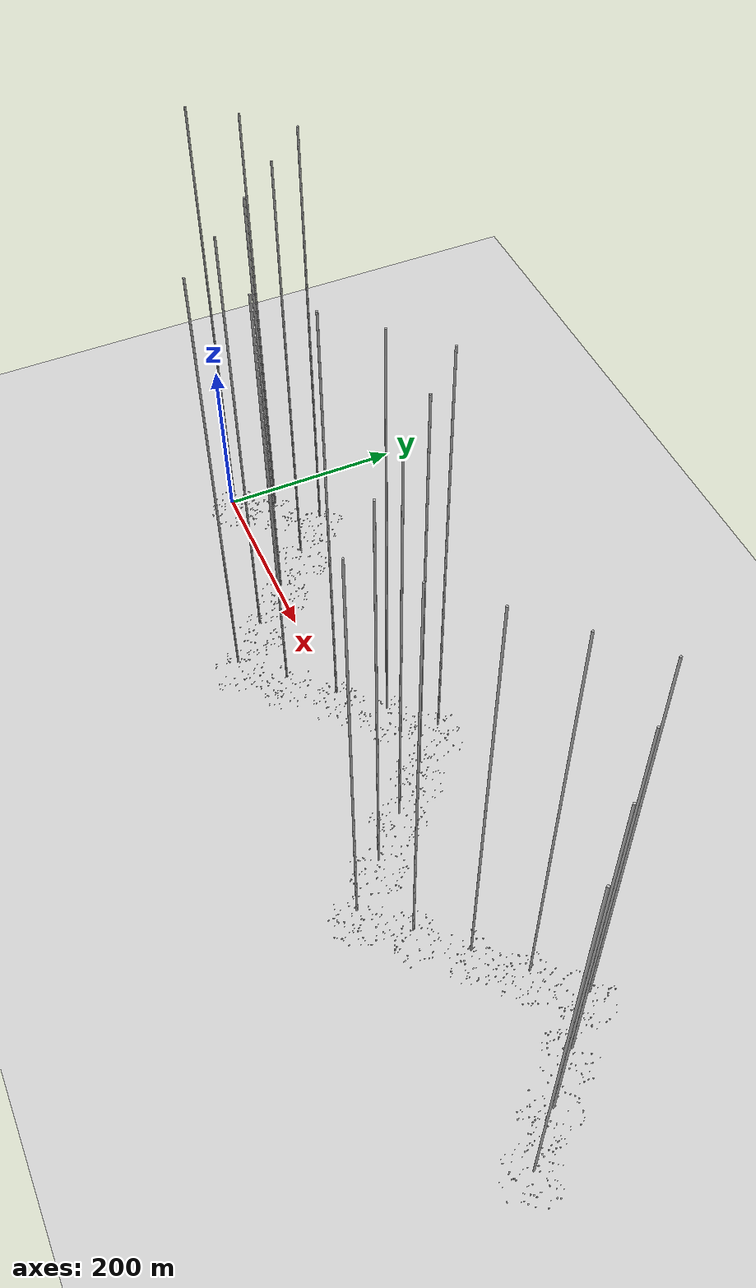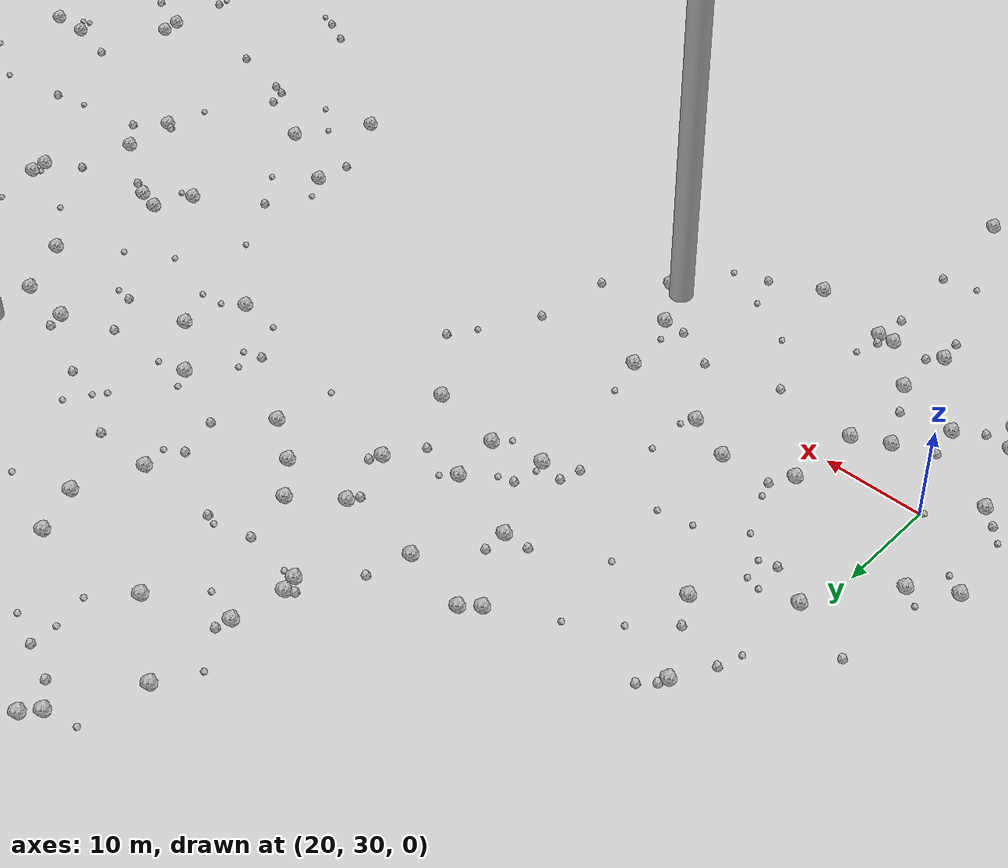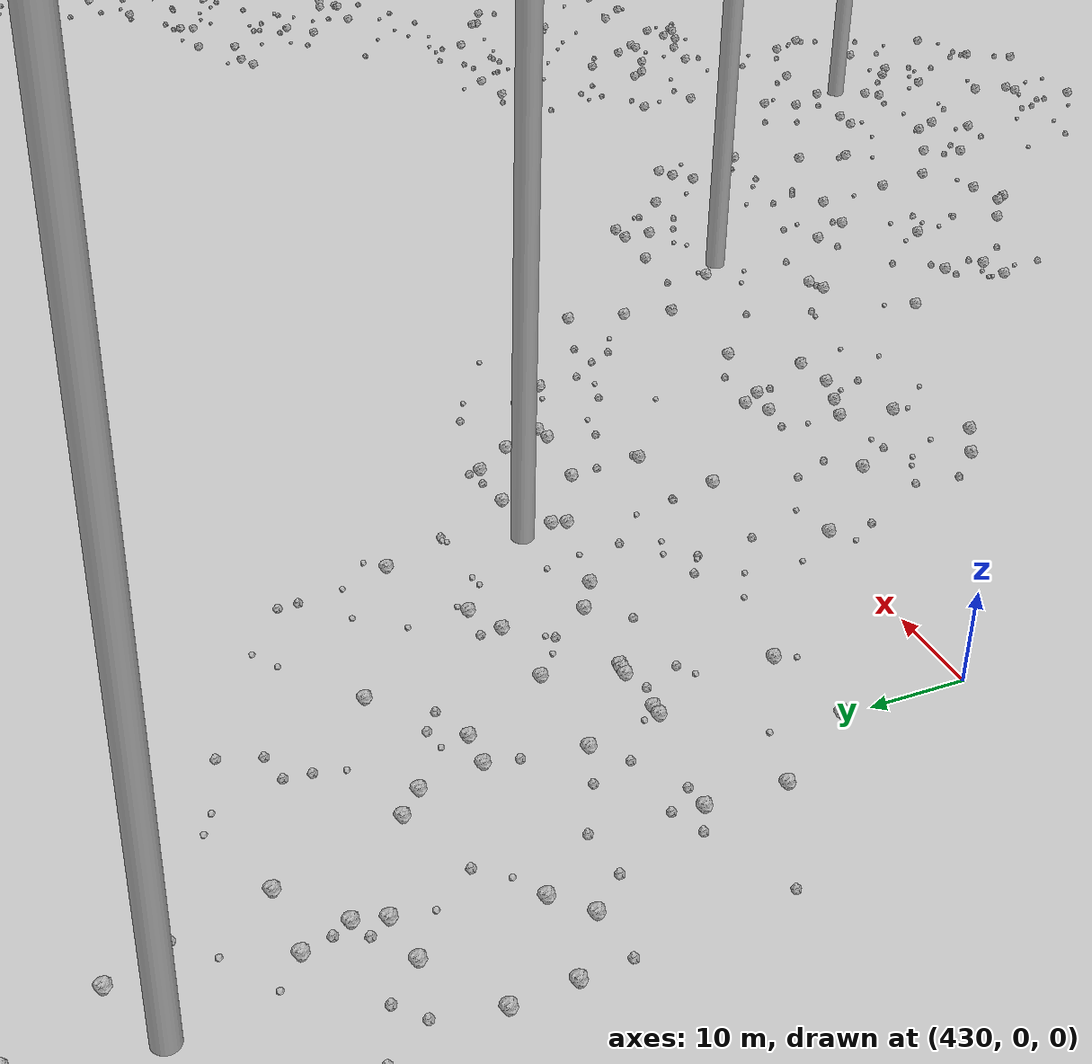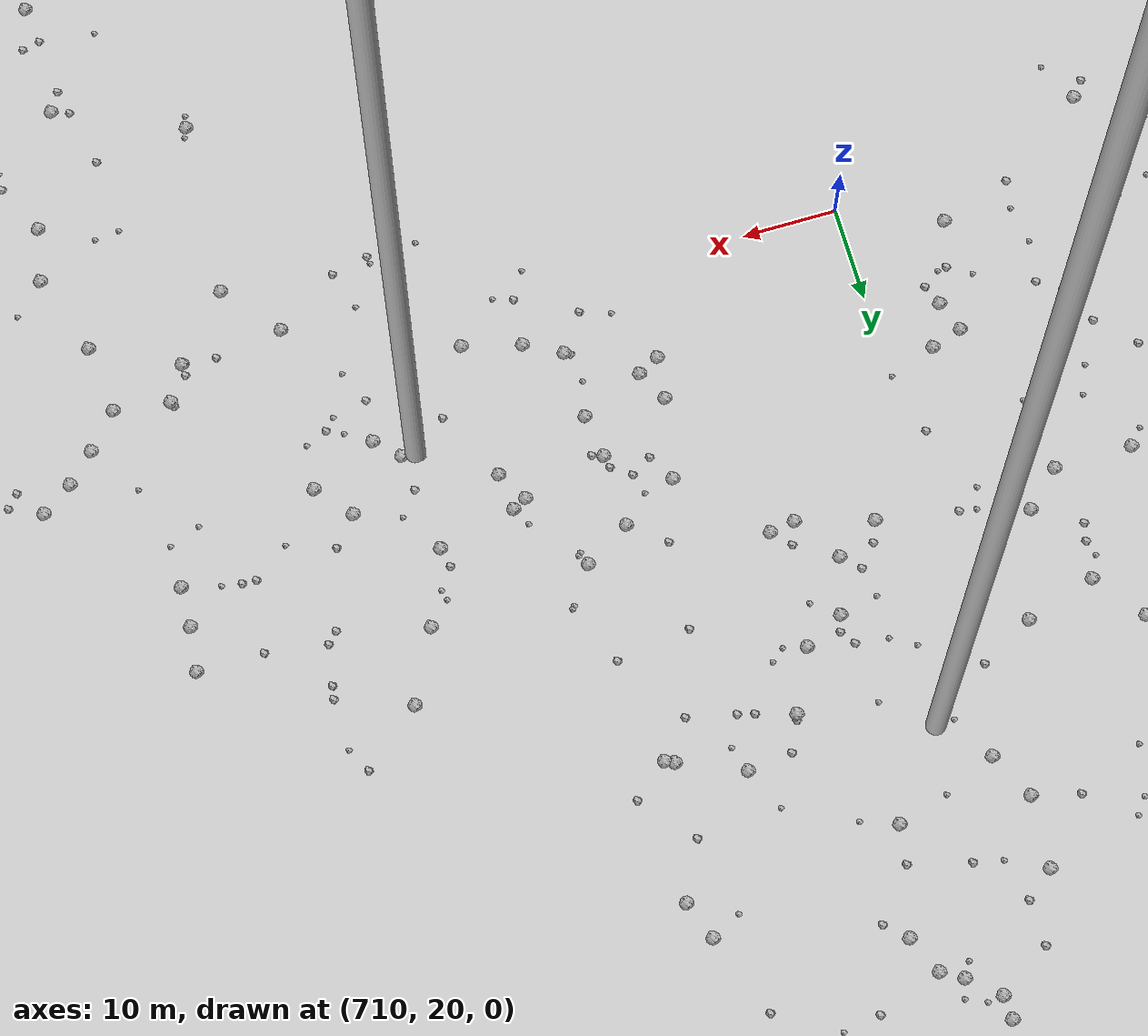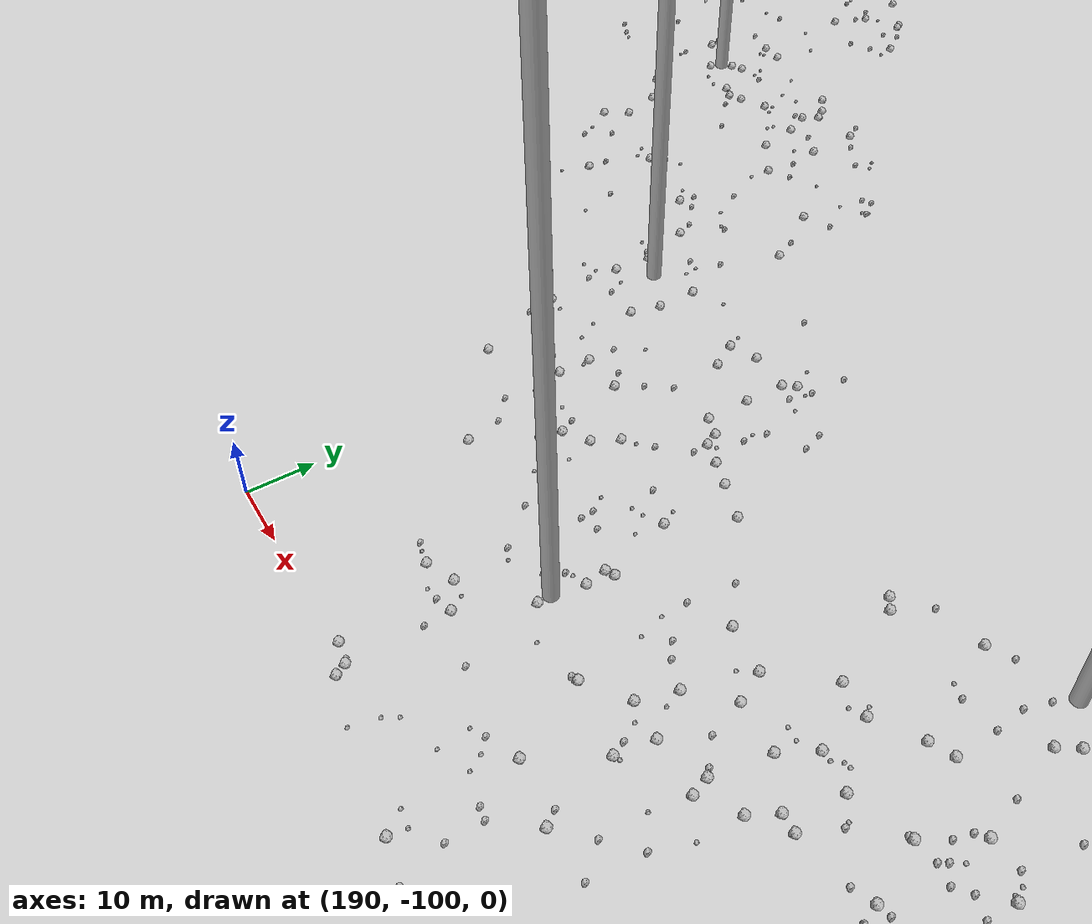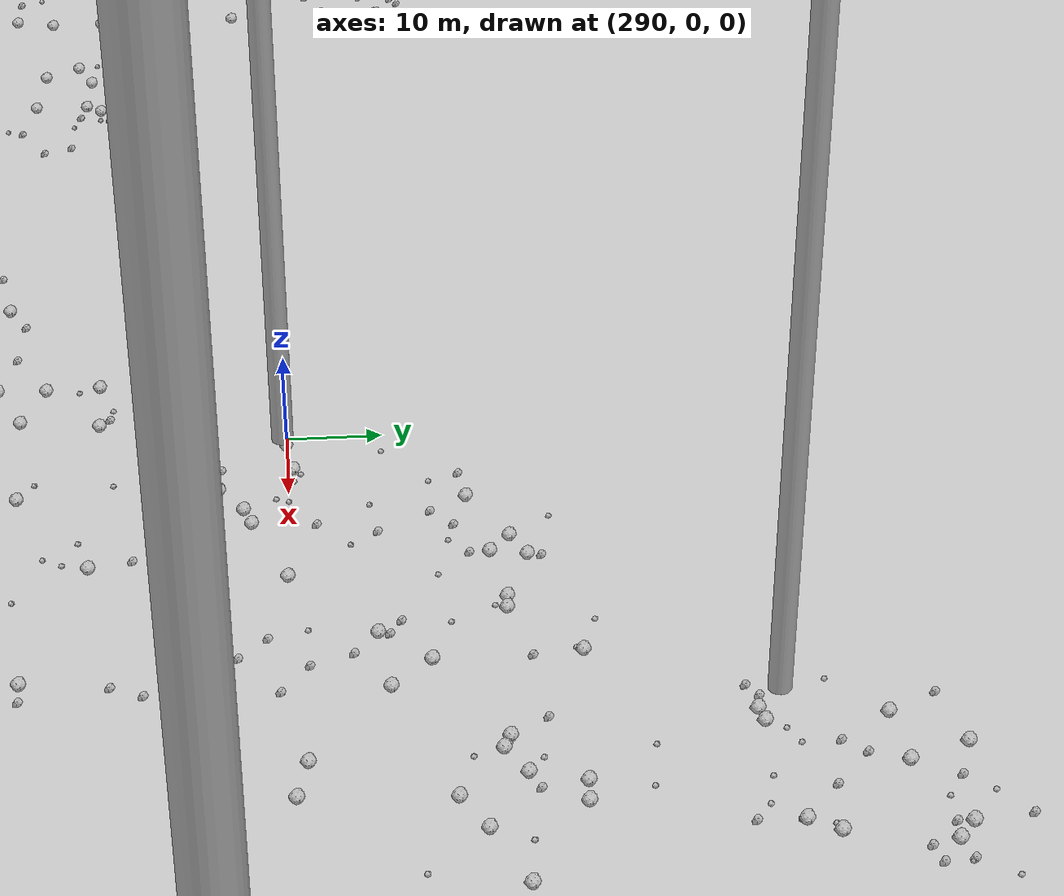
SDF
<sdf version="1.6">
 <world name="default">
  <include><uri>model://custom_ground</uri></include>
  <include><uri>model://sun</uri></include>
  <spherical_coordinates>
   <surface_model>EARTH_WGS84</surface_model>
   <latitude_deg>38.161479</latitude_deg>
   <longitude_deg>-122.454630</longitude_deg>
   <elevation>488.0</elevation>
   <heading_deg>90</heading_deg>
  </spherical_coordinates>
  <model name="rock1_0_0">
   <include><uri>model://rock1</uri><pose>-8.113621575554863 23.394278722028055 0.5 0 0 0</pose></include>
  </model>
  <model name="rock1_0_1">
   <include><uri>model://rock1</uri><pose>8.170621577222548 21.838554088305997 0.5 0 0 0</pose></include>
  </model>
  <model name="rock1_0_2">
   <include><uri>model://rock1</uri><pose>4.151932044873426 0.3960741397759868 0.5 0 0 0</pose></include>
  </model>
  <model name="rock1_0_3">
   <include><uri>model://rock1</uri><pose>12.655860009057854 25.158782949687037 0.5 0 0 0</pose></include>
  </model>
  <model name="rock1_0_4">
   <include><uri>model://rock1</uri><pose>6.03878217224495 3.490037230891815 0.5 0 0 0</pose></include>
  </model>
  <model name="rock1_0_5">
   <include><uri>model://rock1</uri><pose>-2.9020491361308345 25.608448205594414 0.5 0 0 0</pose></include>
  </model>
  <model name="rock1_0_6">
   <include><uri>model://rock1</uri><pose>-17.382112744841198 -6.309102369574308 0.5 0 0 0</pose></include>
  </model>
  <model name="rock1_0_7">
   <include><uri>model://rock1</uri><pose>34.88327546623432 -14.919477226378056 0.5 0 0 0</pose></include>
  </model>
  <model name="rock1_0_8">
   <include><uri>model://rock1</uri><pose>-18.513975356621305 -1.2395018717202788 0.5 0 0 0</pose></include>
  </model>
  <model name="rock1_0_9">
   <include><uri>model://rock1</uri><pose>30.43169063932269 17.603657868843833 0.5 0 0 0</pose></include>
  </model>
  <model name="rock1_0_10">
   <include><uri>model://rock1</uri><pose>37.36814201751751 -8.064247538010921 0.5 0 0 0</pose></include>
  </model>
  <model name="rock1_0_11">
   <include><uri>model://rock1</uri><pose>12.467881877367155 6.328451548001958 0.5 0 0 0</pose></include>
  </model>
  <model name="rock1_0_12">
   <include><uri>model://rock1</uri><pose>27.167786953125017 -23.782470771787025 0.5 0 0 0</pose></include>
  </model>
  <model name="rock1_0_13">
   <include><uri>model://rock1</uri><pose>23.72057220000704 19.685385526438232 0.5 0 0 0</pose></include>
  </model>
  <model name="rock1_0_14">
   <include><uri>model://rock1</uri><pose>13.41068404857593 -18.11974306871952 0.5 0 0 0</pose></include>
  </model>
  <model name="rock1_0_15">
   <include><uri>model://rock1</uri><pose>11.598444644769348 -28.234073335678257 0.5 0 0 0</pose></include>
  </model>
  <model name="rock1_0_16">
   <include><uri>model://rock1</uri><pose>20.028925763567365 -0.28766204573359033 0.5 0 0 0</pose></include>
  </model>
  <model name="rock1_0_17">
   <include><uri>model://rock1</uri><pose>-7.5262230932543055 -9.688229872921731 0.5 0 0 0</pose></include>
  </model>
  <model name="rock1_0_18">
   <include><uri>model://rock1</uri><pose>-5.8303938596365725 15.795157689877435 0.5 0 0 0</pose></include>
  </model>
  <model name="rock1_0_19">
   <include><uri>model://rock1</uri><pose>14.92693023435136 -20.60237178385283 0.5 0 0 0</pose></include>
  </model>
  <model name="rock1_0_20">
   <include><uri>model://rock1</uri><pose>7.254850419774229 24.208140745122975 0.5 0 0 0</pose></include>
  </model>
  <model name="rock1_0_21">
   <include><uri>model://rock1</uri><pose>2.3517807959709742 25.062456712340122 0.5 0 0 0</pose></include>
  </model>
  <model name="rock1_0_22">
   <include><uri>model://rock1</uri><pose>18.57581250768903 18.01375497152923 0.5 0 0 0</pose></include>
  </model>
  <model name="rock1_0_23">
   <include><uri>model://rock1</uri><pose>19.78181938040872 15.536346639519174 0.5 0 0 0</pose></include>
  </model>
  <model name="rock1_0_24">
   <include><uri>model://rock1</uri><pose>26.822963347827333 24.72735839062694 0.5 0 0 0</pose></include>
  </model>
  <model name="rock1_0_25">
   <include><uri>model://rock1</uri><pose>-11.854358693284272 -15.243418099972384 0.5 0 0 0</pose></include>
  </model>
  <model name="rock1_0_26">
   <include><uri>model://rock1</uri><pose>-9.433497431250634 6.972676401577324 0.5 0 0 0</pose></include>
  </model>
  <model name="rock2_0_0">
   <include><uri>model://rock2</uri><pose>36.486302745914976 2.1278105815150568 0.3 0 0 0</pose></include>
  </model>
  <model name="rock2_0_1">
   <include><uri>model://rock2</uri><pose>-13.262142612720428 4.588430054776566 0.3 0 0 0</pose></include>
  </model>
  <model name="rock2_0_2">
   <include><uri>model://rock2</uri><pose>6.944692721285179 8.89854641479483 0.3 0 0 0</pose></include>
  </model>
  <model name="rock2_0_3">
   <include><uri>model://rock2</uri><pose>3.329625957298205 -10.499892410508075 0.3 0 0 0</pose></include>
  </model>
  <model name="rock2_0_4">
   <include><uri>model://rock2</uri><pose>-10.370954060598459 21.236491633820805 0.3 0 0 0</pose></include>
  </model>
  <model name="rock2_0_5">
   <include><uri>model://rock2</uri><pose>32.18341104990135 -6.529278568916968 0.3 0 0 0</pose></include>
  </model>
  <model name="rock2_0_6">
   <include><uri>model://rock2</uri><pose>30.096304006968126 9.390631935228242 0.3 0 0 0</pose></include>
  </model>
  <model name="rock2_0_7">
   <include><uri>model://rock2</uri><pose>5.7772489694288325 18.029050625975728 0.3 0 0 0</pose></include>
  </model>
  <model name="rock2_0_8">
   <include><uri>model://rock2</uri><pose>-17.158784385898528 6.452436599227589 0.3 0 0 0</pose></include>
  </model>
  <model name="rock2_0_9">
   <include><uri>model://rock2</uri><pose>-2.7720208552019834 -22.88396090557881 0.3 0 0 0</pose></include>
  </model>
  <model name="rock2_0_10">
   <include><uri>model://rock2</uri><pose>-1.3452286649411462 -8.546169244783705 0.3 0 0 0</pose></include>
  </model>
  <model name="rock2_0_11">
   <include><uri>model://rock2</uri><pose>12.886897026880291 7.529955069677598 0.3 0 0 0</pose></include>
  </model>
  <model name="rock2_0_12">
   <include><uri>model://rock2</uri><pose>21.156223713047346 17.86786463722695 0.3 0 0 0</pose></include>
  </model>
  <model name="rock2_0_13">
   <include><uri>model://rock2</uri><pose>-5.009487839796897 -12.34037680170044 0.3 0 0 0</pose></include>
  </model>
  <model name="rock2_0_14">
   <include><uri>model://rock2</uri><pose>-6.3724902205926615 24.067988189562676 0.3 0 0 0</pose></include>
  </model>
  <model name="rock2_0_15">
   <include><uri>model://rock2</uri><pose>14.383165169616802 27.14193629566958 0.3 0 0 0</pose></include>
  </model>
  <model name="rock2_0_16">
   <include><uri>model://rock2</uri><pose>-10.218093290649078 -7.365944694513892 0.3 0 0 0</pose></include>
  </model>
  <model name="rock2_0_17">
   <include><uri>model://rock2</uri><pose>7.366798545927061 9.491033632763163 0.3 0 0 0</pose></include>
  </model>
  <model name="rock2_0_18">
   <include><uri>model://rock2</uri><pose>2.9278966434568012 -24.176067671097034 0.3 0 0 0</pose></include>
  </model>
  <model name="rock2_0_19">
   <include><uri>model://rock2</uri><pose>-4.085323781867018 -21.021434438463846 0.3 0 0 0</pose></include>
  </model>
  <model name="rock2_0_20">
   <include><uri>model://rock2</uri><pose>11.24641449943206 13.69997030805763 0.3 0 0 0</pose></include>
  </model>
  <model name="rock2_0_21">
   <include><uri>model://rock2</uri><pose>9.184151799801267 -28.2983948916568 0.3 0 0 0</pose></include>
  </model>
  <model name="rock2_0_22">
   <include><uri>model://rock2</uri><pose>1.480074069893444 -13.854947539472004 0.3 0 0 0</pose></include>
  </model>
  <model name="rock2_0_23">
   <include><uri>model://rock2</uri><pose>35.91758491794675 10.053410522104187 0.3 0 0 0</pose></include>
  </model>
  <model name="rock2_0_24">
   <include><uri>model://rock2</uri><pose>-0.4315421882954702 11.553214470847841 0.3 0 0 0</pose></include>
  </model>
  <model name="rock2_0_25">
   <include><uri>model://rock2</uri><pose>10.353945557057113 5.1040643222266695 0.3 0 0 0</pose></include>
  </model>
  <model name="rock2_0_26">
   <include><uri>model://rock2</uri><pose>26.347607619157827 -17.996070530490613 0.3 0 0 0</pose></include>
  </model>
  <model name="rock3_0_0">
   <include><uri>model://rock3</uri><pose>-4.821225771748976 -16.266954410936165 0.2 0 0 0</pose></include>
  </model>
  <model name="rock3_0_1">
   <include><uri>model://rock3</uri><pose>-18.25570403524094 4.287841739272778 0.2 0 0 0</pose></include>
  </model>
  <model name="rock3_0_2">
   <include><uri>model://rock3</uri><pose>1.4768851693086447 27.769903317600615 0.2 0 0 0</pose></include>
  </model>
  <model name="rock3_0_3">
   <include><uri>model://rock3</uri><pose>27.67336977160361 -17.685836961579067 0.2 0 0 0</pose></include>
  </model>
  <model name="rock3_0_4">
   <include><uri>model://rock3</uri><pose>25.134711478775422 -5.431354655382076 0.2 0 0 0</pose></include>
  </model>
  <model name="rock3_0_5">
   <include><uri>model://rock3</uri><pose>-8.530635153215933 20.044411003013373 0.2 0 0 0</pose></include>
  </model>
  <model name="rock3_0_6">
   <include><uri>model://rock3</uri><pose>18.80278617222079 15.722303966188605 0.2 0 0 0</pose></include>
  </model>
  <model name="rock3_0_7">
   <include><uri>model://rock3</uri><pose>10.339659298561806 4.123885694631262 0.2 0 0 0</pose></include>
  </model>
  <model name="rock3_0_8">
   <include><uri>model://rock3</uri><pose>24.06818718118692 -19.36867989149944 0.2 0 0 0</pose></include>
  </model>
  <model name="rock3_0_9">
   <include><uri>model://rock3</uri><pose>11.247439407015747 -25.242831697874262 0.2 0 0 0</pose></include>
  </model>
  <model name="rock3_0_10">
   <include><uri>model://rock3</uri><pose>12.29210061206507 -25.384375698650764 0.2 0 0 0</pose></include>
  </model>
  <model name="rock3_0_11">
   <include><uri>model://rock3</uri><pose>9.689154414013224 -22.65874627148657 0.2 0 0 0</pose></include>
  </model>
  <model name="rock3_0_12">
   <include><uri>model://rock3</uri><pose>5.073414770072517 4.58834968440641 0.2 0 0 0</pose></include>
  </model>
  <model name="rock3_0_13">
   <include><uri>model://rock3</uri><pose>12.8871846391826 5.378240661962913 0.2 0 0 0</pose></include>
  </model>
  <model name="rock3_0_14">
   <include><uri>model://rock3</uri><pose>-2.5787895462017723 -15.633643132779781 0.2 0 0 0</pose></include>
  </model>
  <model name="rock3_0_15">
   <include><uri>model://rock3</uri><pose>15.584331734741504 4.896160169064942 0.2 0 0 0</pose></include>
  </model>
  <model name="rock3_0_16">
   <include><uri>model://rock3</uri><pose>12.989287903248261 28.47178984170695 0.2 0 0 0</pose></include>
  </model>
  <model name="rock3_0_17">
   <include><uri>model://rock3</uri><pose>10.21385588916699 17.202939547922988 0.2 0 0 0</pose></include>
  </model>
  <model name="rock3_0_18">
   <include><uri>model://rock3</uri><pose>-3.441312520294982 25.488650731819185 0.2 0 0 0</pose></include>
  </model>
  <model name="rock3_0_19">
   <include><uri>model://rock3</uri><pose>-3.2730659776449116 -22.523672782472563 0.2 0 0 0</pose></include>
  </model>
  <model name="rock3_0_20">
   <include><uri>model://rock3</uri><pose>33.10282245220633 1.238089272271111 0.2 0 0 0</pose></include>
  </model>
  <model name="rock3_0_21">
   <include><uri>model://rock3</uri><pose>10.809447101290175 4.524101377079383 0.2 0 0 0</pose></include>
  </model>
  <model name="rock3_0_22">
   <include><uri>model://rock3</uri><pose>-1.0962218817480434 26.17417220468367 0.2 0 0 0</pose></include>
  </model>
  <model name="rock3_0_23">
   <include><uri>model://rock3</uri><pose>7.534662103560823 -11.915528146938676 0.2 0 0 0</pose></include>
  </model>
  <model name="rock3_0_24">
   <include><uri>model://rock3</uri><pose>2.395091434702156 18.283388652962273 0.2 0 0 0</pose></include>
  </model>
  <model name="rock3_0_25">
   <include><uri>model://rock3</uri><pose>1.8293656719631315 -16.363884588394463 0.2 0 0 0</pose></include>
  </model>
  <model name="rock3_0_26">
   <include><uri>model://rock3</uri><pose>29.786309922688353 -3.573612173674853 0.2 0 0 0</pose></include>
  </model>
  <model name="rock1_1_0">
   <include><uri>model://rock1</uri><pose>55.805378834828595 20.770096078447935 0.5 0 0 0</pose></include>
  </model>
  <model name="rock1_1_1">
   <include><uri>model://rock1</uri><pose>59.6813468249755 56.655591256499065 0.5 0 0 0</pose></include>
  </model>
  <model name="rock1_1_2">
   <include><uri>model://rock1</uri><pose>40.772639780273714 63.6568224745761 0.5 0 0 0</pose></include>
  </model>
  <model name="rock1_1_3">
   <include><uri>model://rock1</uri><pose>28.905699138045353 51.082222949837856 0.5 0 0 0</pose></include>
  </model>
  <model name="rock1_1_4">
   <include><uri>model://rock1</uri><pose>34.71646799108581 13.168187231032476 0.5 0 0 0</pose></include>
  </model>
  <model name="rock1_1_5">
   <include><uri>model://rock1</uri><pose>24.436943888454074 59.12798554694212 0.5 0 0 0</pose></include>
  </model>
  <model name="rock1_1_6">
   <include><uri>model://rock1</uri><pose>36.31750713674919 13.27097423825471 0.5 0 0 0</pose></include>
  </model>
  <model name="rock1_1_7">
   <include><uri>model://rock1</uri><pose>16.15998956502485 25.726918410457706 0.5 0 0 0</pose></include>
  </model>
  <model name="rock1_1_8">
   <include><uri>model://rock1</uri><pose>37.20084703464943 36.10966641867201 0.5 0 0 0</pose></include>
  </model>
  <model name="rock1_1_9">
   <include><uri>model://rock1</uri><pose>12.130899958644578 35.624790408967584 0.5 0 0 0</pose></include>
  </model>
  <model name="rock1_1_10">
   <include><uri>model://rock1</uri><pose>52.676430617218266 25.43557519264749 0.5 0 0 0</pose></include>
  </model>
  <model name="rock1_1_11">
   <include><uri>model://rock1</uri><pose>49.34494143642035 63.467512797712814 0.5 0 0 0</pose></include>
  </model>
  <model name="rock1_1_12">
   <include><uri>model://rock1</uri><pose>53.65220278477172 48.746865255619085 0.5 0 0 0</pose></include>
  </model>
  <model name="rock1_1_13">
   <include><uri>model://rock1</uri><pose>58.08895320656142 62.616054786702605 0.5 0 0 0</pose></include>
  </model>
  <model name="rock1_1_14">
   <include><uri>model://rock1</uri><pose>44.14374987040365 11.497778681336905 0.5 0 0 0</pose></include>
  </model>
  <model name="rock1_1_15">
   <include><uri>model://rock1</uri><pose>30.145842731817442 26.412856280663174 0.5 0 0 0</pose></include>
  </model>
  <model name="rock1_1_16">
   <include><uri>model://rock1</uri><pose>48.560471381658495 47.62491819386547 0.5 0 0 0</pose></include>
  </model>
  <model name="rock1_1_17">
   <include><uri>model://rock1</uri><pose>52.94880396529857 53.82917251493501 0.5 0 0 0</pose></include>
  </model>
  <model name="rock1_1_18">
   <include><uri>model://rock1</uri><pose>15.94591516589589 38.08245790639876 0.5 0 0 0</pose></include>
  </model>
  <model name="rock1_1_19">
   <include><uri>model://rock1</uri><pose>41.84471388964883 34.097408309259464 0.5 0 0 0</pose></include>
  </model>
  <model name="rock1_1_20">
   <include><uri>model://rock1</uri><pose>61.22463275990906 47.41549018031015 0.5 0 0 0</pose></include>
  </model>
  <model name="rock1_1_21">
   <include><uri>model://rock1</uri><pose>21.486422577839 45.51415183894788 0.5 0 0 0</pose></include>
  </model>
  <model name="rock1_1_22">
   <include><uri>model://rock1</uri><pose>30.704982224526244 33.874715410209554 0.5 0 0 0</pose></include>
  </model>
  <model name="rock1_1_23">
   <include><uri>model://rock1</uri><pose>42.35572956856025 64.99926589022023 0.5 0 0 0</pose></include>
  </model>
  <model name="rock1_1_24">
   <include><uri>model://rock1</uri><pose>29.824749649820276 11.869396693565564 0.5 0 0 0</pose></include>
  </model>
  <model name="rock1_1_25">
   <include><uri>model://rock1</uri><pose>45.090082473667614 56.30599952965601 0.5 0 0 0</pose></include>
  </model>
  <model name="rock1_1_26">
   <include><uri>model://rock1</uri><pose>50.99453109172403 32.06786787866254 0.5 0 0 0</pose></include>
  </model>
  <model name="rock2_1_0">
   <include><uri>model://rock2</uri><pose>23.055707816047253 22.979102835019535 0.3 0 0 0</pose></include>
  </model>
  <model name="rock2_1_1">
   <include><uri>model://rock2</uri><pose>46.02220778245575 27.547008641166148 0.3 0 0 0</pose></include>
  </model>
  <model name="rock2_1_2">
   <include><uri>model://rock2</uri><pose>48.72993742824337 51.05365783641102 0.3 0 0 0</pose></include>
  </model>
  <model name="rock2_1_3">
   <include><uri>model://rock2</uri><pose>22.279380621483497 55.414527044772335 0.3 0 0 0</pose></include>
  </model>
  <model name="rock2_1_4">
   <include><uri>model://rock2</uri><pose>60.85931072957374 25.179954412736908 0.3 0 0 0</pose></include>
  </model>
  <model name="rock2_1_5">
   <include><uri>model://rock2</uri><pose>27.178819690429652 53.9969454789828 0.3 0 0 0</pose></include>
  </model>
  <model name="rock2_1_6">
   <include><uri>model://rock2</uri><pose>42.447795789233545 56.131331511402735 0.3 0 0 0</pose></include>
  </model>
  <model name="rock2_1_7">
   <include><uri>model://rock2</uri><pose>45.035382442591285 58.69072990284925 0.3 0 0 0</pose></include>
  </model>
  <model name="rock2_1_8">
   <include><uri>model://rock2</uri><pose>66.85093035757978 40.865552857157525 0.3 0 0 0</pose></include>
  </model>
  <model name="rock2_1_9">
   <include><uri>model://rock2</uri><pose>28.665947624600072 20.66814946331802 0.3 0 0 0</pose></include>
  </model>
  <model name="rock2_1_10">
   <include><uri>model://rock2</uri><pose>36.488886653281 13.072504729096806 0.3 0 0 0</pose></include>
  </model>
  <model name="rock2_1_11">
   <include><uri>model://rock2</uri><pose>15.2471038533199 47.918603537422385 0.3 0 0 0</pose></include>
  </model>
  <model name="rock2_1_12">
   <include><uri>model://rock2</uri><pose>50.47455142218729 67.67523791653045 0.3 0 0 0</pose></include>
  </model>
  <model name="rock2_1_13">
   <include><uri>model://rock2</uri><pose>60.234316708280595 57.73002405189329 0.3 0 0 0</pose></include>
  </model>
  <model name="rock2_1_14">
   <include><uri>model://rock2</uri><pose>31.03926901963036 13.042446623995659 0.3 0 0 0</pose></include>
  </model>
  <model name="rock2_1_15">
   <include><uri>model://rock2</uri><pose>26.078664052213764 61.23137216315258 0.3 0 0 0</pose></include>
  </model>
  <model name="rock2_1_16">
   <include><uri>model://rock2</uri><pose>35.73627658835213 14.23320188093399 0.3 0 0 0</pose></include>
  </model>
  <model name="rock2_1_17">
   <include><uri>model://rock2</uri><pose>32.01156987464765 36.000741424930354 0.3 0 0 0</pose></include>
  </model>
  <model name="rock2_1_18">
   <include><uri>model://rock2</uri><pose>25.307797547623956 43.44082556596176 0.3 0 0 0</pose></include>
  </model>
  <model name="rock2_1_19">
   <include><uri>model://rock2</uri><pose>48.979914706498356 13.929293314990616 0.3 0 0 0</pose></include>
  </model>
  <model name="rock2_1_20">
   <include><uri>model://rock2</uri><pose>61.90244772692653 32.77900710577623 0.3 0 0 0</pose></include>
  </model>
  <model name="rock2_1_21">
   <include><uri>model://rock2</uri><pose>38.61599279435988 25.57100467598445 0.3 0 0 0</pose></include>
  </model>
  <model name="rock2_1_22">
   <include><uri>model://rock2</uri><pose>24.767480168820498 59.99242618980127 0.3 0 0 0</pose></include>
  </model>
  <model name="rock2_1_23">
   <include><uri>model://rock2</uri><pose>50.2606947354321 25.50379228173124 0.3 0 0 0</pose></include>
  </model>
  <model name="rock2_1_24">
   <include><uri>model://rock2</uri><pose>45.338902355360474 46.05929325251409 0.3 0 0 0</pose></include>
  </model>
  <model name="rock2_1_25">
   <include><uri>model://rock2</uri><pose>57.400193209687 53.2004884697055 0.3 0 0 0</pose></include>
  </model>
  <model name="rock2_1_26">
   <include><uri>model://rock2</uri><pose>45.91374282115016 48.08687722139963 0.3 0 0 0</pose></include>
  </model>
  <model name="rock3_1_0">
   <include><uri>model://rock3</uri><pose>14.158544986304246 39.17953380271875 0.2 0 0 0</pose></include>
  </model>
  <model name="rock3_1_1">
   <include><uri>model://rock3</uri><pose>34.88080018067193 60.26487089863219 0.2 0 0 0</pose></include>
  </model>
  <model name="rock3_1_2">
   <include><uri>model://rock3</uri><pose>36.48123633803501 16.48557588859724 0.2 0 0 0</pose></include>
  </model>
  <model name="rock3_1_3">
   <include><uri>model://rock3</uri><pose>19.705501560823038 29.73929737385619 0.2 0 0 0</pose></include>
  </model>
  <model name="rock3_1_4">
   <include><uri>model://rock3</uri><pose>49.9013239601723 35.947668557438945 0.2 0 0 0</pose></include>
  </model>
  <model name="rock3_1_5">
   <include><uri>model://rock3</uri><pose>42.59150232878257 35.285566449856894 0.2 0 0 0</pose></include>
  </model>
  <model name="rock3_1_6">
   <include><uri>model://rock3</uri><pose>21.541349754549778 53.035935267679626 0.2 0 0 0</pose></include>
  </model>
  <model name="rock3_1_7">
   <include><uri>model://rock3</uri><pose>37.1601643911564 45.107549074852244 0.2 0 0 0</pose></include>
  </model>
  <model name="rock3_1_8">
   <include><uri>model://rock3</uri><pose>52.29617493429145 15.074665736181316 0.2 0 0 0</pose></include>
  </model>
  <model name="rock3_1_9">
   <include><uri>model://rock3</uri><pose>25.00837635659241 46.412970005305766 0.2 0 0 0</pose></include>
  </model>
  <model name="rock3_1_10">
   <include><uri>model://rock3</uri><pose>65.16242337338103 38.256730665769346 0.2 0 0 0</pose></include>
  </model>
  <model name="rock3_1_11">
   <include><uri>model://rock3</uri><pose>27.013068823991883 43.837470988829914 0.2 0 0 0</pose></include>
  </model>
  <model name="rock3_1_12">
   <include><uri>model://rock3</uri><pose>29.437352114581678 41.812517048215575 0.2 0 0 0</pose></include>
  </model>
  <model name="rock3_1_13">
   <include><uri>model://rock3</uri><pose>48.21634916094335 48.639523710809264 0.2 0 0 0</pose></include>
  </model>
  <model name="rock3_1_14">
   <include><uri>model://rock3</uri><pose>30.694910264438477 57.09369110119287 0.2 0 0 0</pose></include>
  </model>
  <model name="rock3_1_15">
   <include><uri>model://rock3</uri><pose>33.749310391621236 44.40562290604818 0.2 0 0 0</pose></include>
  </model>
  <model name="rock3_1_16">
   <include><uri>model://rock3</uri><pose>36.1654322729277 52.36614029171714 0.2 0 0 0</pose></include>
  </model>
  <model name="rock3_1_17">
   <include><uri>model://rock3</uri><pose>42.70598057244213 19.912264755455933 0.2 0 0 0</pose></include>
  </model>
  <model name="rock3_1_18">
   <include><uri>model://rock3</uri><pose>26.480992131205287 46.028532821992115 0.2 0 0 0</pose></include>
  </model>
  <model name="rock3_1_19">
   <include><uri>model://rock3</uri><pose>54.246574701778286 54.863194532807015 0.2 0 0 0</pose></include>
  </model>
  <model name="rock3_1_20">
   <include><uri>model://rock3</uri><pose>42.426953514927185 39.48281809348066 0.2 0 0 0</pose></include>
  </model>
  <model name="rock3_1_21">
   <include><uri>model://rock3</uri><pose>52.40536728796675 47.22213345345588 0.2 0 0 0</pose></include>
  </model>
  <model name="rock3_1_22">
   <include><uri>model://rock3</uri><pose>51.32690712850747 27.561563198279146 0.2 0 0 0</pose></include>
  </model>
  <model name="rock3_1_23">
   <include><uri>model://rock3</uri><pose>13.975292214000724 34.346885997552405 0.2 0 0 0</pose></include>
  </model>
  <model name="rock3_1_24">
   <include><uri>model://rock3</uri><pose>31.45919615246222 37.56197372632806 0.2 0 0 0</pose></include>
  </model>
  <model name="rock3_1_25">
   <include><uri>model://rock3</uri><pose>50.27246236902113 51.444465665558106 0.2 0 0 0</pose></include>
  </model>
  <model name="rock3_1_26">
   <include><uri>model://rock3</uri><pose>47.756548661514934 17.22778455015982 0.2 0 0 0</pose></include>
  </model>
  <model name="rock1_2_0">
   <include><uri>model://rock1</uri><pose>60.53121743961978 96.61298418227257 0.5 0 0 0</pose></include>
  </model>
  <model name="rock1_2_1">
   <include><uri>model://rock1</uri><pose>54.785765390894795 71.99030949235538 0.5 0 0 0</pose></include>
  </model>
  <model name="rock1_2_2">
   <include><uri>model://rock1</uri><pose>74.44525119931494 71.81296281624518 0.5 0 0 0</pose></include>
  </model>
  <model name="rock1_2_3">
   <include><uri>model://rock1</uri><pose>65.59709172049494 62.688354388476256 0.5 0 0 0</pose></include>
  </model>
  <model name="rock1_2_4">
   <include><uri>model://rock1</uri><pose>66.49628427021952 103.27342829803929 0.5 0 0 0</pose></include>
  </model>
  <model name="rock1_2_5">
   <include><uri>model://rock1</uri><pose>55.21879422077714 78.68838540524935 0.5 0 0 0</pose></include>
  </model>
  <model name="rock1_2_6">
   <include><uri>model://rock1</uri><pose>62.38672600463127 66.05510943365593 0.5 0 0 0</pose></include>
  </model>
  <model name="rock1_2_7">
   <include><uri>model://rock1</uri><pose>100.35536968027009 72.44840410319796 0.5 0 0 0</pose></include>
  </model>
  <model name="rock1_2_8">
   <include><uri>model://rock1</uri><pose>96.4543385424236 90.71034802584452 0.5 0 0 0</pose></include>
  </model>
  <model name="rock1_2_9">
   <include><uri>model://rock1</uri><pose>103.92426801742887 77.35042967109682 0.5 0 0 0</pose></include>
  </model>
  <model name="rock1_2_10">
   <include><uri>model://rock1</uri><pose>77.2826134166121 95.28663754943021 0.5 0 0 0</pose></include>
  </model>
  <model name="rock1_2_11">
   <include><uri>model://rock1</uri><pose>91.68421753920131 76.81987599805385 0.5 0 0 0</pose></include>
  </model>
  <model name="rock1_2_12">
   <include><uri>model://rock1</uri><pose>96.24667242368254 63.94061306418882 0.5 0 0 0</pose></include>
  </model>
  <model name="rock1_2_13">
   <include><uri>model://rock1</uri><pose>76.94037608740874 78.16279097623541 0.5 0 0 0</pose></include>
  </model>
  <model name="rock1_2_14">
   <include><uri>model://rock1</uri><pose>55.02209313678813 87.6523528557187 0.5 0 0 0</pose></include>
  </model>
  <model name="rock1_2_15">
   <include><uri>model://rock1</uri><pose>100.10321729549673 73.50084889857476 0.5 0 0 0</pose></include>
  </model>
  <model name="rock1_2_16">
   <include><uri>model://rock1</uri><pose>81.36342604275045 61.14506063581668 0.5 0 0 0</pose></include>
  </model>
  <model name="rock1_2_17">
   <include><uri>model://rock1</uri><pose>59.195049982264614 95.12614840464624 0.5 0 0 0</pose></include>
  </model>
  <model name="rock1_2_18">
   <include><uri>model://rock1</uri><pose>88.58394579648619 91.57785585411082 0.5 0 0 0</pose></include>
  </model>
  <model name="rock1_2_19">
   <include><uri>model://rock1</uri><pose>101.79106668924794 63.35509536958357 0.5 0 0 0</pose></include>
  </model>
  <model name="rock1_2_20">
   <include><uri>model://rock1</uri><pose>74.93110183718984 82.83679956494595 0.5 0 0 0</pose></include>
  </model>
  <model name="rock1_2_21">
   <include><uri>model://rock1</uri><pose>84.17368188408759 50.99457493010742 0.5 0 0 0</pose></include>
  </model>
  <model name="rock1_2_22">
   <include><uri>model://rock1</uri><pose>70.08215532439253 59.82201225080075 0.5 0 0 0</pose></include>
  </model>
  <model name="rock1_2_23">
   <include><uri>model://rock1</uri><pose>54.34815409976736 73.5300714470118 0.5 0 0 0</pose></include>
  </model>
  <model name="rock1_2_24">
   <include><uri>model://rock1</uri><pose>62.95397340090163 81.9374798170583 0.5 0 0 0</pose></include>
  </model>
  <model name="rock1_2_25">
   <include><uri>model://rock1</uri><pose>77.84150404887272 107.78208337622144 0.5 0 0 0</pose></include>
  </model>
  <model name="rock1_2_26">
   <include><uri>model://rock1</uri><pose>86.6044726805267 56.59257414456291 0.5 0 0 0</pose></include>
  </model>
  <model name="rock2_2_0">
   <include><uri>model://rock2</uri><pose>90.7205155945314 61.84939506225591 0.3 0 0 0</pose></include>
  </model>
  <model name="rock2_2_1">
   <include><uri>model://rock2</uri><pose>82.27151272132312 98.40473930843243 0.3 0 0 0</pose></include>
  </model>
  <model name="rock2_2_2">
   <include><uri>model://rock2</uri><pose>77.41129678902777 54.99718938118464 0.3 0 0 0</pose></include>
  </model>
  <model name="rock2_2_3">
   <include><uri>model://rock2</uri><pose>71.23297614576455 107.54160723799924 0.3 0 0 0</pose></include>
  </model>
  <model name="rock2_2_4">
   <include><uri>model://rock2</uri><pose>65.42590834448514 91.48171514460981 0.3 0 0 0</pose></include>
  </model>
  <model name="rock2_2_5">
   <include><uri>model://rock2</uri><pose>87.62782333599522 95.2338043732167 0.3 0 0 0</pose></include>
  </model>
  <model name="rock2_2_6">
   <include><uri>model://rock2</uri><pose>55.50492073782669 80.14268442130515 0.3 0 0 0</pose></include>
  </model>
  <model name="rock2_2_7">
   <include><uri>model://rock2</uri><pose>61.52026970329061 93.01425174984465 0.3 0 0 0</pose></include>
  </model>
  <model name="rock2_2_8">
   <include><uri>model://rock2</uri><pose>80.45966216169623 102.40230012186899 0.3 0 0 0</pose></include>
  </model>
  <model name="rock2_2_9">
   <include><uri>model://rock2</uri><pose>57.41260122003857 61.55290236305132 0.3 0 0 0</pose></include>
  </model>
  <model name="rock2_2_10">
   <include><uri>model://rock2</uri><pose>93.23442635626296 57.94966143261694 0.3 0 0 0</pose></include>
  </model>
  <model name="rock2_2_11">
   <include><uri>model://rock2</uri><pose>99.18981084213547 88.53824206167408 0.3 0 0 0</pose></include>
  </model>
  <model name="rock2_2_12">
   <include><uri>model://rock2</uri><pose>95.75181973596423 65.53753321017534 0.3 0 0 0</pose></include>
  </model>
  <model name="rock2_2_13">
   <include><uri>model://rock2</uri><pose>77.25185168801293 104.36732950364735 0.3 0 0 0</pose></include>
  </model>
  <model name="rock2_2_14">
   <include><uri>model://rock2</uri><pose>95.3521644089767 72.72855539647847 0.3 0 0 0</pose></include>
  </model>
  <model name="rock2_2_15">
   <include><uri>model://rock2</uri><pose>73.09385600897718 68.22564063861152 0.3 0 0 0</pose></include>
  </model>
  <model name="rock2_2_16">
   <include><uri>model://rock2</uri><pose>102.06625172948573 67.77919424981262 0.3 0 0 0</pose></include>
  </model>
  <model name="rock2_2_17">
   <include><uri>model://rock2</uri><pose>60.94049972202866 71.2660889834728 0.3 0 0 0</pose></include>
  </model>
  <model name="rock2_2_18">
   <include><uri>model://rock2</uri><pose>65.67005859329471 72.01717823989225 0.3 0 0 0</pose></include>
  </model>
  <model name="rock2_2_19">
   <include><uri>model://rock2</uri><pose>74.28792101825238 64.1327397914406 0.3 0 0 0</pose></include>
  </model>
  <model name="rock2_2_20">
   <include><uri>model://rock2</uri><pose>99.88771017900936 90.6174506655543 0.3 0 0 0</pose></include>
  </model>
  <model name="rock2_2_21">
   <include><uri>model://rock2</uri><pose>88.57972849896277 102.30081669222939 0.3 0 0 0</pose></include>
  </model>
  <model name="rock2_2_22">
   <include><uri>model://rock2</uri><pose>108.7999754237655 77.92675985969953 0.3 0 0 0</pose></include>
  </model>
  <model name="rock2_2_23">
   <include><uri>model://rock2</uri><pose>89.02975390842239 68.2130430760284 0.3 0 0 0</pose></include>
  </model>
  <model name="rock2_2_24">
   <include><uri>model://rock2</uri><pose>53.518147494308685 73.02870767008741 0.3 0 0 0</pose></include>
  </model>
  <model name="rock2_2_25">
   <include><uri>model://rock2</uri><pose>80.60704955332488 71.72646983876423 0.3 0 0 0</pose></include>
  </model>
  <model name="rock2_2_26">
   <include><uri>model://rock2</uri><pose>73.57396112183994 109.11123556293194 0.3 0 0 0</pose></include>
  </model>
  <model name="rock3_2_0">
   <include><uri>model://rock3</uri><pose>78.08979223716854 57.26209909215669 0.2 0 0 0</pose></include>
  </model>
  <model name="rock3_2_1">
   <include><uri>model://rock3</uri><pose>86.16993925260954 52.28453071806513 0.2 0 0 0</pose></include>
  </model>
  <model name="rock3_2_2">
   <include><uri>model://rock3</uri><pose>58.8087324862193 77.61448201708323 0.2 0 0 0</pose></include>
  </model>
  <model name="rock3_2_3">
   <include><uri>model://rock3</uri><pose>69.10759630799593 53.841461508003455 0.2 0 0 0</pose></include>
  </model>
  <model name="rock3_2_4">
   <include><uri>model://rock3</uri><pose>84.23238710065266 61.81051727107271 0.2 0 0 0</pose></include>
  </model>
  <model name="rock3_2_5">
   <include><uri>model://rock3</uri><pose>84.08713013793852 50.70188984828143 0.2 0 0 0</pose></include>
  </model>
  <model name="rock3_2_6">
   <include><uri>model://rock3</uri><pose>85.2791322898605 68.92929326299473 0.2 0 0 0</pose></include>
  </model>
  <model name="rock3_2_7">
   <include><uri>model://rock3</uri><pose>55.919087928521805 94.25605016563617 0.2 0 0 0</pose></include>
  </model>
  <model name="rock3_2_8">
   <include><uri>model://rock3</uri><pose>79.86974563260148 51.243592865897895 0.2 0 0 0</pose></include>
  </model>
  <model name="rock3_2_9">
   <include><uri>model://rock3</uri><pose>65.42691346601399 88.7805558965511 0.2 0 0 0</pose></include>
  </model>
  <model name="rock3_2_10">
   <include><uri>model://rock3</uri><pose>74.63773765765316 103.93981849046985 0.2 0 0 0</pose></include>
  </model>
  <model name="rock3_2_11">
   <include><uri>model://rock3</uri><pose>80.30196856665225 62.84534049254631 0.2 0 0 0</pose></include>
  </model>
  <model name="rock3_2_12">
   <include><uri>model://rock3</uri><pose>74.8353294794197 69.2114876382431 0.2 0 0 0</pose></include>
  </model>
  <model name="rock3_2_13">
   <include><uri>model://rock3</uri><pose>64.5703236194313 72.28237753614385 0.2 0 0 0</pose></include>
  </model>
  <model name="rock3_2_14">
   <include><uri>model://rock3</uri><pose>82.64399929166133 80.14858950515737 0.2 0 0 0</pose></include>
  </model>
  <model name="rock3_2_15">
   <include><uri>model://rock3</uri><pose>52.73558641255667 83.75548217040296 0.2 0 0 0</pose></include>
  </model>
  <model name="rock3_2_16">
   <include><uri>model://rock3</uri><pose>80.21115105152349 89.41333384779715 0.2 0 0 0</pose></include>
  </model>
  <model name="rock3_2_17">
   <include><uri>model://rock3</uri><pose>68.96056227083395 90.08580771209317 0.2 0 0 0</pose></include>
  </model>
  <model name="rock3_2_18">
   <include><uri>model://rock3</uri><pose>79.31672890103472 55.52906398425032 0.2 0 0 0</pose></include>
  </model>
  <model name="rock3_2_19">
   <include><uri>model://rock3</uri><pose>56.01954622929046 71.880479140119 0.2 0 0 0</pose></include>
  </model>
  <model name="rock3_2_20">
   <include><uri>model://rock3</uri><pose>68.55740743281049 97.12660773995586 0.2 0 0 0</pose></include>
  </model>
  <model name="rock3_2_21">
   <include><uri>model://rock3</uri><pose>88.5628604971917 52.543500297861044 0.2 0 0 0</pose></include>
  </model>
  <model name="rock3_2_22">
   <include><uri>model://rock3</uri><pose>66.21476166326877 85.29049756359791 0.2 0 0 0</pose></include>
  </model>
  <model name="rock3_2_23">
   <include><uri>model://rock3</uri><pose>95.06392250229861 57.65370864528519 0.2 0 0 0</pose></include>
  </model>
  <model name="rock3_2_24">
   <include><uri>model://rock3</uri><pose>84.39236542857219 67.8368045108212 0.2 0 0 0</pose></include>
  </model>
  <model name="rock3_2_25">
   <include><uri>model://rock3</uri><pose>86.73601841221492 71.23223753545645 0.2 0 0 0</pose></include>
  </model>
  <model name="rock3_2_26">
   <include><uri>model://rock3</uri><pose>98.18381972696359 71.71886582702254 0.2 0 0 0</pose></include>
  </model>
  <model name="rock1_3_0">
   <include><uri>model://rock1</uri><pose>132.6581721599743 49.80995765784438 0.5 0 0 0</pose></include>
  </model>
  <model name="rock1_3_1">
   <include><uri>model://rock1</uri><pose>96.4139090282269 21.99317239980732 0.5 0 0 0</pose></include>
  </model>
  <model name="rock1_3_2">
   <include><uri>model://rock1</uri><pose>112.62650033180371 41.74052915382176 0.5 0 0 0</pose></include>
  </model>
  <model name="rock1_3_3">
   <include><uri>model://rock1</uri><pose>135.49718431660304 21.74016048445932 0.5 0 0 0</pose></include>
  </model>
  <model name="rock1_3_4">
   <include><uri>model://rock1</uri><pose>133.31509932447238 18.209787078151315 0.5 0 0 0</pose></include>
  </model>
  <model name="rock1_3_5">
   <include><uri>model://rock1</uri><pose>101.11227762101987 28.674186267735905 0.5 0 0 0</pose></include>
  </model>
  <model name="rock1_3_6">
   <include><uri>model://rock1</uri><pose>146.67002445081766 52.60360358812679 0.5 0 0 0</pose></include>
  </model>
  <model name="rock1_3_7">
   <include><uri>model://rock1</uri><pose>141.0311898657015 59.24107921043419 0.5 0 0 0</pose></include>
  </model>
  <model name="rock1_3_8">
   <include><uri>model://rock1</uri><pose>134.9167962626911 55.98810176623943 0.5 0 0 0</pose></include>
  </model>
  <model name="rock1_3_9">
   <include><uri>model://rock1</uri><pose>104.85159383184596 57.67617844293154 0.5 0 0 0</pose></include>
  </model>
  <model name="rock1_3_10">
   <include><uri>model://rock1</uri><pose>137.57638556092044 31.34686369100309 0.5 0 0 0</pose></include>
  </model>
  <model name="rock1_3_11">
   <include><uri>model://rock1</uri><pose>100.93563956174474 43.13230278499806 0.5 0 0 0</pose></include>
  </model>
  <model name="rock1_3_12">
   <include><uri>model://rock1</uri><pose>116.30760670673193 63.69688334070826 0.5 0 0 0</pose></include>
  </model>
  <model name="rock1_3_13">
   <include><uri>model://rock1</uri><pose>133.2295822142132 64.71447341629687 0.5 0 0 0</pose></include>
  </model>
  <model name="rock1_3_14">
   <include><uri>model://rock1</uri><pose>126.6711600270308 24.929717887624008 0.5 0 0 0</pose></include>
  </model>
  <model name="rock1_3_15">
   <include><uri>model://rock1</uri><pose>126.86894964031238 23.02840795163477 0.5 0 0 0</pose></include>
  </model>
  <model name="rock1_3_16">
   <include><uri>model://rock1</uri><pose>140.49354014130878 60.04642333789428 0.5 0 0 0</pose></include>
  </model>
  <model name="rock1_3_17">
   <include><uri>model://rock1</uri><pose>93.59557410816019 32.31522407701573 0.5 0 0 0</pose></include>
  </model>
  <model name="rock1_3_18">
   <include><uri>model://rock1</uri><pose>105.14460712861526 46.22731505037375 0.5 0 0 0</pose></include>
  </model>
  <model name="rock1_3_19">
   <include><uri>model://rock1</uri><pose>133.70769882503615 31.38340957574331 0.5 0 0 0</pose></include>
  </model>
  <model name="rock1_3_20">
   <include><uri>model://rock1</uri><pose>102.71806790950157 46.81817996663251 0.5 0 0 0</pose></include>
  </model>
  <model name="rock1_3_21">
   <include><uri>model://rock1</uri><pose>126.54111207181217 67.3080002528508 0.5 0 0 0</pose></include>
  </model>
  <model name="rock1_3_22">
   <include><uri>model://rock1</uri><pose>116.7531814116638 49.77494687855011 0.5 0 0 0</pose></include>
  </model>
  <model name="rock1_3_23">
   <include><uri>model://rock1</uri><pose>137.35552955302973 22.81494931477587 0.5 0 0 0</pose></include>
  </model>
  <model name="rock1_3_24">
   <include><uri>model://rock1</uri><pose>116.71005725222396 51.44094974568626 0.5 0 0 0</pose></include>
  </model>
  <model name="rock1_3_25">
   <include><uri>model://rock1</uri><pose>124.11661362597056 12.478963057263151 0.5 0 0 0</pose></include>
  </model>
  <model name="rock1_3_26">
   <include><uri>model://rock1</uri><pose>112.58163476246925 36.51327397143575 0.5 0 0 0</pose></include>
  </model>
  <model name="rock2_3_0">
   <include><uri>model://rock2</uri><pose>141.62067583375787 55.053857316569164 0.3 0 0 0</pose></include>
  </model>
  <model name="rock2_3_1">
   <include><uri>model://rock2</uri><pose>142.03325736865804 23.520599166007827 0.3 0 0 0</pose></include>
  </model>
  <model name="rock2_3_2">
   <include><uri>model://rock2</uri><pose>115.20542786825516 39.12394194051402 0.3 0 0 0</pose></include>
  </model>
  <model name="rock2_3_3">
   <include><uri>model://rock2</uri><pose>92.97740164488646 28.864094970441926 0.3 0 0 0</pose></include>
  </model>
  <model name="rock2_3_4">
   <include><uri>model://rock2</uri><pose>117.11623464297539 61.47403748016895 0.3 0 0 0</pose></include>
  </model>
  <model name="rock2_3_5">
   <include><uri>model://rock2</uri><pose>110.71795705625135 12.626177548078697 0.3 0 0 0</pose></include>
  </model>
  <model name="rock2_3_6">
   <include><uri>model://rock2</uri><pose>107.86591160951936 24.330809275163425 0.3 0 0 0</pose></include>
  </model>
  <model name="rock2_3_7">
   <include><uri>model://rock2</uri><pose>126.16467243802747 17.16067924478506 0.3 0 0 0</pose></include>
  </model>
  <model name="rock2_3_8">
   <include><uri>model://rock2</uri><pose>115.57793762137085 22.493848376708875 0.3 0 0 0</pose></include>
  </model>
  <model name="rock2_3_9">
   <include><uri>model://rock2</uri><pose>113.28981927828667 47.56712691699369 0.3 0 0 0</pose></include>
  </model>
  <model name="rock2_3_10">
   <include><uri>model://rock2</uri><pose>122.27402953532616 63.70543951136843 0.3 0 0 0</pose></include>
  </model>
  <model name="rock2_3_11">
   <include><uri>model://rock2</uri><pose>127.92977419606721 56.81962448921677 0.3 0 0 0</pose></include>
  </model>
  <model name="rock2_3_12">
   <include><uri>model://rock2</uri><pose>143.65041133804132 56.97510378824271 0.3 0 0 0</pose></include>
  </model>
  <model name="rock2_3_13">
   <include><uri>model://rock2</uri><pose>133.94051621137453 54.2138895769784 0.3 0 0 0</pose></include>
  </model>
  <model name="rock2_3_14">
   <include><uri>model://rock2</uri><pose>107.2334610115059 26.09682610014014 0.3 0 0 0</pose></include>
  </model>
  <model name="rock2_3_15">
   <include><uri>model://rock2</uri><pose>111.81814647758222 36.75800450890602 0.3 0 0 0</pose></include>
  </model>
  <model name="rock2_3_16">
   <include><uri>model://rock2</uri><pose>132.7340728409618 57.86406770182739 0.3 0 0 0</pose></include>
  </model>
  <model name="rock2_3_17">
   <include><uri>model://rock2</uri><pose>113.56440163983223 11.256712918967882 0.3 0 0 0</pose></include>
  </model>
  <model name="rock2_3_18">
   <include><uri>model://rock2</uri><pose>125.57605705683005 41.04330425671819 0.3 0 0 0</pose></include>
  </model>
  <model name="rock2_3_19">
   <include><uri>model://rock2</uri><pose>106.90549217537352 45.41571665676068 0.3 0 0 0</pose></include>
  </model>
  <model name="rock2_3_20">
   <include><uri>model://rock2</uri><pose>131.4048590955445 21.42867623024963 0.3 0 0 0</pose></include>
  </model>
  <model name="rock2_3_21">
   <include><uri>model://rock2</uri><pose>117.60596872781181 68.27013681588228 0.3 0 0 0</pose></include>
  </model>
  <model name="rock2_3_22">
   <include><uri>model://rock2</uri><pose>144.38287401287874 49.3572560222867 0.3 0 0 0</pose></include>
  </model>
  <model name="rock2_3_23">
   <include><uri>model://rock2</uri><pose>109.14021563010326 23.9328853312214 0.3 0 0 0</pose></include>
  </model>
  <model name="rock2_3_24">
   <include><uri>model://rock2</uri><pose>128.54940126449753 32.5590965354868 0.3 0 0 0</pose></include>
  </model>
  <model name="rock2_3_25">
   <include><uri>model://rock2</uri><pose>94.60608032025509 38.90009595724251 0.3 0 0 0</pose></include>
  </model>
  <model name="rock2_3_26">
   <include><uri>model://rock2</uri><pose>140.83694335838476 47.32388561518078 0.3 0 0 0</pose></include>
  </model>
  <model name="rock3_3_0">
   <include><uri>model://rock3</uri><pose>123.97829415001152 11.72729806552557 0.2 0 0 0</pose></include>
  </model>
  <model name="rock3_3_1">
   <include><uri>model://rock3</uri><pose>139.33922896270883 25.838725916003696 0.2 0 0 0</pose></include>
  </model>
  <model name="rock3_3_2">
   <include><uri>model://rock3</uri><pose>122.15523599736798 40.17466048557621 0.2 0 0 0</pose></include>
  </model>
  <model name="rock3_3_3">
   <include><uri>model://rock3</uri><pose>135.84484512091535 15.905504874026775 0.2 0 0 0</pose></include>
  </model>
  <model name="rock3_3_4">
   <include><uri>model://rock3</uri><pose>116.10930198417907 50.75054907629388 0.2 0 0 0</pose></include>
  </model>
  <model name="rock3_3_5">
   <include><uri>model://rock3</uri><pose>99.31381221121471 53.50455135160624 0.2 0 0 0</pose></include>
  </model>
  <model name="rock3_3_6">
   <include><uri>model://rock3</uri><pose>102.38907426770089 43.31583454405363 0.2 0 0 0</pose></include>
  </model>
  <model name="rock3_3_7">
   <include><uri>model://rock3</uri><pose>145.40024091433003 28.734185884286084 0.2 0 0 0</pose></include>
  </model>
  <model name="rock3_3_8">
   <include><uri>model://rock3</uri><pose>135.13602572130347 29.809605386153464 0.2 0 0 0</pose></include>
  </model>
  <model name="rock3_3_9">
   <include><uri>model://rock3</uri><pose>140.10637277209716 23.906139649813625 0.2 0 0 0</pose></include>
  </model>
  <model name="rock3_3_10">
   <include><uri>model://rock3</uri><pose>115.2530883789431 10.63619072927158 0.2 0 0 0</pose></include>
  </model>
  <model name="rock3_3_11">
   <include><uri>model://rock3</uri><pose>92.05805558544087 34.6533870899798 0.2 0 0 0</pose></include>
  </model>
  <model name="rock3_3_12">
   <include><uri>model://rock3</uri><pose>132.67926527251473 42.126113541757185 0.2 0 0 0</pose></include>
  </model>
  <model name="rock3_3_13">
   <include><uri>model://rock3</uri><pose>115.5365585837092 56.219268078521786 0.2 0 0 0</pose></include>
  </model>
  <model name="rock3_3_14">
   <include><uri>model://rock3</uri><pose>97.5028131731139 35.18672128322841 0.2 0 0 0</pose></include>
  </model>
  <model name="rock3_3_15">
   <include><uri>model://rock3</uri><pose>111.45249418436256 32.25774106867192 0.2 0 0 0</pose></include>
  </model>
  <model name="rock3_3_16">
   <include><uri>model://rock3</uri><pose>127.1183300121229 58.414575526535444 0.2 0 0 0</pose></include>
  </model>
  <model name="rock3_3_17">
   <include><uri>model://rock3</uri><pose>134.30706036932634 29.57619336408999 0.2 0 0 0</pose></include>
  </model>
  <model name="rock3_3_18">
   <include><uri>model://rock3</uri><pose>147.10068031359236 49.86000394261214 0.2 0 0 0</pose></include>
  </model>
  <model name="rock3_3_19">
   <include><uri>model://rock3</uri><pose>138.50770645179784 38.920530775765556 0.2 0 0 0</pose></include>
  </model>
  <model name="rock3_3_20">
   <include><uri>model://rock3</uri><pose>136.50550299396411 57.932048721730794 0.2 0 0 0</pose></include>
  </model>
  <model name="rock3_3_21">
   <include><uri>model://rock3</uri><pose>102.13721486303315 23.100127171048822 0.2 0 0 0</pose></include>
  </model>
  <model name="rock3_3_22">
   <include><uri>model://rock3</uri><pose>126.20767386781449 15.932896210478608 0.2 0 0 0</pose></include>
  </model>
  <model name="rock3_3_23">
   <include><uri>model://rock3</uri><pose>99.07528837757688 25.601528962015323 0.2 0 0 0</pose></include>
  </model>
  <model name="rock3_3_24">
   <include><uri>model://rock3</uri><pose>94.77055694664377 50.74435530271265 0.2 0 0 0</pose></include>
  </model>
  <model name="rock3_3_25">
   <include><uri>model://rock3</uri><pose>91.1573622247299 44.542497921461276 0.2 0 0 0</pose></include>
  </model>
  <model name="rock3_3_26">
   <include><uri>model://rock3</uri><pose>109.68683835815875 53.2805318495714 0.2 0 0 0</pose></include>
  </model>
  <model name="rock1_4_0">
   <include><uri>model://rock1</uri><pose>136.67601961926104 2.242440424306963 0.5 0 0 0</pose></include>
  </model>
  <model name="rock1_4_1">
   <include><uri>model://rock1</uri><pose>173.85523633241974 -16.579608254961563 0.5 0 0 0</pose></include>
  </model>
  <model name="rock1_4_2">
   <include><uri>model://rock1</uri><pose>146.01292373861213 16.321096230633174 0.5 0 0 0</pose></include>
  </model>
  <model name="rock1_4_3">
   <include><uri>model://rock1</uri><pose>153.18893208974066 -9.077278653171142 0.5 0 0 0</pose></include>
  </model>
  <model name="rock1_4_4">
   <include><uri>model://rock1</uri><pose>166.39945779794243 26.169394335158373 0.5 0 0 0</pose></include>
  </model>
  <model name="rock1_4_5">
   <include><uri>model://rock1</uri><pose>138.83320970277157 -4.358342526872093 0.5 0 0 0</pose></include>
  </model>
  <model name="rock1_4_6">
   <include><uri>model://rock1</uri><pose>161.76033162731838 -13.393764174916889 0.5 0 0 0</pose></include>
  </model>
  <model name="rock1_4_7">
   <include><uri>model://rock1</uri><pose>157.12143858758608 22.357590255763135 0.5 0 0 0</pose></include>
  </model>
  <model name="rock1_4_8">
   <include><uri>model://rock1</uri><pose>141.5076263320921 16.1580135212961 0.5 0 0 0</pose></include>
  </model>
  <model name="rock1_4_9">
   <include><uri>model://rock1</uri><pose>160.70289378506877 11.222318924339874 0.5 0 0 0</pose></include>
  </model>
  <model name="rock1_4_10">
   <include><uri>model://rock1</uri><pose>154.90134020988904 -7.211957616958163 0.5 0 0 0</pose></include>
  </model>
  <model name="rock1_4_11">
   <include><uri>model://rock1</uri><pose>187.36100590682446 -5.908717844583737 0.5 0 0 0</pose></include>
  </model>
  <model name="rock1_4_12">
   <include><uri>model://rock1</uri><pose>136.30847646627373 -8.268294434447437 0.5 0 0 0</pose></include>
  </model>
  <model name="rock1_4_13">
   <include><uri>model://rock1</uri><pose>166.37106005827033 -11.543052413967935 0.5 0 0 0</pose></include>
  </model>
  <model name="rock1_4_14">
   <include><uri>model://rock1</uri><pose>166.85285485012008 17.340084802821934 0.5 0 0 0</pose></include>
  </model>
  <model name="rock1_4_15">
   <include><uri>model://rock1</uri><pose>143.82640872847395 15.20666125602665 0.5 0 0 0</pose></include>
  </model>
  <model name="rock1_4_16">
   <include><uri>model://rock1</uri><pose>181.200884410853 3.9424425685026563 0.5 0 0 0</pose></include>
  </model>
  <model name="rock1_4_17">
   <include><uri>model://rock1</uri><pose>141.3300765813875 2.149493236909045 0.5 0 0 0</pose></include>
  </model>
  <model name="rock1_4_18">
   <include><uri>model://rock1</uri><pose>131.81176725146497 6.426564913343512 0.5 0 0 0</pose></include>
  </model>
  <model name="rock1_4_19">
   <include><uri>model://rock1</uri><pose>149.53249420475123 -19.67776790808795 0.5 0 0 0</pose></include>
  </model>
  <model name="rock1_4_20">
   <include><uri>model://rock1</uri><pose>167.22517279037825 6.8893104701691 0.5 0 0 0</pose></include>
  </model>
  <model name="rock1_4_21">
   <include><uri>model://rock1</uri><pose>158.51727028028034 25.05043931871679 0.5 0 0 0</pose></include>
  </model>
  <model name="rock1_4_22">
   <include><uri>model://rock1</uri><pose>159.1472753499404 18.127294659113034 0.5 0 0 0</pose></include>
  </model>
  <model name="rock1_4_23">
   <include><uri>model://rock1</uri><pose>150.34101940992736 18.684495872349117 0.5 0 0 0</pose></include>
  </model>
  <model name="rock1_4_24">
   <include><uri>model://rock1</uri><pose>154.3226682056324 29.27551309641214 0.5 0 0 0</pose></include>
  </model>
  <model name="rock1_4_25">
   <include><uri>model://rock1</uri><pose>135.74074956760685 5.522126512602036 0.5 0 0 0</pose></include>
  </model>
  <model name="rock1_4_26">
   <include><uri>model://rock1</uri><pose>157.2393273769253 26.883761720704385 0.5 0 0 0</pose></include>
  </model>
  <model name="rock2_4_0">
   <include><uri>model://rock2</uri><pose>137.30254289896547 2.8379808679979277 0.3 0 0 0</pose></include>
  </model>
  <model name="rock2_4_1">
   <include><uri>model://rock2</uri><pose>155.65341575014264 21.825460685432986 0.3 0 0 0</pose></include>
  </model>
  <model name="rock2_4_2">
   <include><uri>model://rock2</uri><pose>182.6106733377859 15.611531949223291 0.3 0 0 0</pose></include>
  </model>
  <model name="rock2_4_3">
   <include><uri>model://rock2</uri><pose>158.24020994842255 -20.658150123019823 0.3 0 0 0</pose></include>
  </model>
  <model name="rock2_4_4">
   <include><uri>model://rock2</uri><pose>170.0117814260331 -2.694887389129775 0.3 0 0 0</pose></include>
  </model>
  <model name="rock2_4_5">
   <include><uri>model://rock2</uri><pose>185.53204023740827 -2.0772857355108414 0.3 0 0 0</pose></include>
  </model>
  <model name="rock2_4_6">
   <include><uri>model://rock2</uri><pose>170.62615594715632 9.075677533254954 0.3 0 0 0</pose></include>
  </model>
  <model name="rock2_4_7">
   <include><uri>model://rock2</uri><pose>142.6612561760401 -10.544135570952548 0.3 0 0 0</pose></include>
  </model>
  <model name="rock2_4_8">
   <include><uri>model://rock2</uri><pose>172.61419892302308 -13.87257291305081 0.3 0 0 0</pose></include>
  </model>
  <model name="rock2_4_9">
   <include><uri>model://rock2</uri><pose>164.7602069678603 28.889613603691643 0.3 0 0 0</pose></include>
  </model>
  <model name="rock2_4_10">
   <include><uri>model://rock2</uri><pose>184.02752224285433 -15.488511243663263 0.3 0 0 0</pose></include>
  </model>
  <model name="rock2_4_11">
   <include><uri>model://rock2</uri><pose>166.60204745124207 -8.73587043395533 0.3 0 0 0</pose></include>
  </model>
  <model name="rock2_4_12">
   <include><uri>model://rock2</uri><pose>173.90402734206452 21.290573367542926 0.3 0 0 0</pose></include>
  </model>
  <model name="rock2_4_13">
   <include><uri>model://rock2</uri><pose>174.9793263869394 -24.05334061062311 0.3 0 0 0</pose></include>
  </model>
  <model name="rock2_4_14">
   <include><uri>model://rock2</uri><pose>158.72523260248926 25.340408754108495 0.3 0 0 0</pose></include>
  </model>
  <model name="rock2_4_15">
   <include><uri>model://rock2</uri><pose>168.75646064646384 -10.7027938267329 0.3 0 0 0</pose></include>
  </model>
  <model name="rock2_4_16">
   <include><uri>model://rock2</uri><pose>167.74647065285782 12.081618504400438 0.3 0 0 0</pose></include>
  </model>
  <model name="rock2_4_17">
   <include><uri>model://rock2</uri><pose>151.25053207557738 8.116845848225609 0.3 0 0 0</pose></include>
  </model>
  <model name="rock2_4_18">
   <include><uri>model://rock2</uri><pose>149.64062603335677 -16.21478991345475 0.3 0 0 0</pose></include>
  </model>
  <model name="rock2_4_19">
   <include><uri>model://rock2</uri><pose>162.549312771943 19.5480542247276 0.3 0 0 0</pose></include>
  </model>
  <model name="rock2_4_20">
   <include><uri>model://rock2</uri><pose>184.02079670469772 16.521770998833603 0.3 0 0 0</pose></include>
  </model>
  <model name="rock2_4_21">
   <include><uri>model://rock2</uri><pose>176.81857040117956 -9.473282233490426 0.3 0 0 0</pose></include>
  </model>
  <model name="rock2_4_22">
   <include><uri>model://rock2</uri><pose>145.7140172654489 12.962635101188418 0.3 0 0 0</pose></include>
  </model>
  <model name="rock2_4_23">
   <include><uri>model://rock2</uri><pose>185.95604634731785 13.757390072928217 0.3 0 0 0</pose></include>
  </model>
  <model name="rock2_4_24">
   <include><uri>model://rock2</uri><pose>169.09536855043055 24.147157159586 0.3 0 0 0</pose></include>
  </model>
  <model name="rock2_4_25">
   <include><uri>model://rock2</uri><pose>185.51383199562665 6.219216738672863 0.3 0 0 0</pose></include>
  </model>
  <model name="rock2_4_26">
   <include><uri>model://rock2</uri><pose>140.23147359251556 -14.93603950942773 0.3 0 0 0</pose></include>
  </model>
  <model name="rock3_4_0">
   <include><uri>model://rock3</uri><pose>138.91974819978367 -12.492842220414474 0.2 0 0 0</pose></include>
  </model>
  <model name="rock3_4_1">
   <include><uri>model://rock3</uri><pose>175.12652068603148 11.517728589550735 0.2 0 0 0</pose></include>
  </model>
  <model name="rock3_4_2">
   <include><uri>model://rock3</uri><pose>157.01033753142184 -8.449675034842244 0.2 0 0 0</pose></include>
  </model>
  <model name="rock3_4_3">
   <include><uri>model://rock3</uri><pose>150.93206468906786 20.072666208641188 0.2 0 0 0</pose></include>
  </model>
  <model name="rock3_4_4">
   <include><uri>model://rock3</uri><pose>150.90078941100495 -10.23723263246886 0.2 0 0 0</pose></include>
  </model>
  <model name="rock3_4_5">
   <include><uri>model://rock3</uri><pose>157.04958637294843 -5.129591259955863 0.2 0 0 0</pose></include>
  </model>
  <model name="rock3_4_6">
   <include><uri>model://rock3</uri><pose>166.86297170216298 3.4894722272712926 0.2 0 0 0</pose></include>
  </model>
  <model name="rock3_4_7">
   <include><uri>model://rock3</uri><pose>159.85997355656752 -26.73507809761409 0.2 0 0 0</pose></include>
  </model>
  <model name="rock3_4_8">
   <include><uri>model://rock3</uri><pose>164.4488465890147 14.731176786011659 0.2 0 0 0</pose></include>
  </model>
  <model name="rock3_4_9">
   <include><uri>model://rock3</uri><pose>185.96554413167166 14.263800273926577 0.2 0 0 0</pose></include>
  </model>
  <model name="rock3_4_10">
   <include><uri>model://rock3</uri><pose>174.65644192029907 24.382963548948524 0.2 0 0 0</pose></include>
  </model>
  <model name="rock3_4_11">
   <include><uri>model://rock3</uri><pose>147.79864647123168 -24.31710609633435 0.2 0 0 0</pose></include>
  </model>
  <model name="rock3_4_12">
   <include><uri>model://rock3</uri><pose>156.2393765673531 16.283109497123277 0.2 0 0 0</pose></include>
  </model>
  <model name="rock3_4_13">
   <include><uri>model://rock3</uri><pose>172.27761372650352 -23.223326600732747 0.2 0 0 0</pose></include>
  </model>
  <model name="rock3_4_14">
   <include><uri>model://rock3</uri><pose>138.49987341290444 15.214961315074262 0.2 0 0 0</pose></include>
  </model>
  <model name="rock3_4_15">
   <include><uri>model://rock3</uri><pose>165.22961132147591 -10.699029096408982 0.2 0 0 0</pose></include>
  </model>
  <model name="rock3_4_16">
   <include><uri>model://rock3</uri><pose>149.39803707219335 -8.484427760433931 0.2 0 0 0</pose></include>
  </model>
  <model name="rock3_4_17">
   <include><uri>model://rock3</uri><pose>163.8588119004226 -9.311784300771244 0.2 0 0 0</pose></include>
  </model>
  <model name="rock3_4_18">
   <include><uri>model://rock3</uri><pose>175.74513029723033 22.975752360853093 0.2 0 0 0</pose></include>
  </model>
  <model name="rock3_4_19">
   <include><uri>model://rock3</uri><pose>148.56318245463248 24.2213250110577 0.2 0 0 0</pose></include>
  </model>
  <model name="rock3_4_20">
   <include><uri>model://rock3</uri><pose>156.08285137269678 15.040331911741283 0.2 0 0 0</pose></include>
  </model>
  <model name="rock3_4_21">
   <include><uri>model://rock3</uri><pose>151.67181249174934 25.069501759463378 0.2 0 0 0</pose></include>
  </model>
  <model name="rock3_4_22">
   <include><uri>model://rock3</uri><pose>172.5117000826823 -7.231722837652377 0.2 0 0 0</pose></include>
  </model>
  <model name="rock3_4_23">
   <include><uri>model://rock3</uri><pose>175.61310292006382 -9.39403197605116 0.2 0 0 0</pose></include>
  </model>
  <model name="rock3_4_24">
   <include><uri>model://rock3</uri><pose>185.1822984202411 13.38721251765351 0.2 0 0 0</pose></include>
  </model>
  <model name="rock3_4_25">
   <include><uri>model://rock3</uri><pose>151.98522971409454 18.50051530043735 0.2 0 0 0</pose></include>
  </model>
  <model name="rock3_4_26">
   <include><uri>model://rock3</uri><pose>181.87071262122734 11.279167741307802 0.2 0 0 0</pose></include>
  </model>
  <model name="rock1_5_0">
   <include><uri>model://rock1</uri><pose>215.12077294980557 -38.49930410240644 0.5 0 0 0</pose></include>
  </model>
  <model name="rock1_5_1">
   <include><uri>model://rock1</uri><pose>177.2608095962377 -43.60831888339113 0.5 0 0 0</pose></include>
  </model>
  <model name="rock1_5_2">
   <include><uri>model://rock1</uri><pose>192.3757106998695 -45.86430105978582 0.5 0 0 0</pose></include>
  </model>
  <model name="rock1_5_3">
   <include><uri>model://rock1</uri><pose>186.4958842967036 -34.54746190588625 0.5 0 0 0</pose></include>
  </model>
  <model name="rock1_5_4">
   <include><uri>model://rock1</uri><pose>203.14051034263235 -57.00623585456589 0.5 0 0 0</pose></include>
  </model>
  <model name="rock1_5_5">
   <include><uri>model://rock1</uri><pose>212.09202725138775 -24.221095157095448 0.5 0 0 0</pose></include>
  </model>
  <model name="rock1_5_6">
   <include><uri>model://rock1</uri><pose>206.88784623825742 -54.555312543167545 0.5 0 0 0</pose></include>
  </model>
  <model name="rock1_5_7">
   <include><uri>model://rock1</uri><pose>199.2059247542534 -45.60885138999244 0.5 0 0 0</pose></include>
  </model>
  <model name="rock1_5_8">
   <include><uri>model://rock1</uri><pose>219.68137058147877 -41.589175537841456 0.5 0 0 0</pose></include>
  </model>
  <model name="rock1_5_9">
   <include><uri>model://rock1</uri><pose>212.03558631599185 -37.49159488426253 0.5 0 0 0</pose></include>
  </model>
  <model name="rock1_5_10">
   <include><uri>model://rock1</uri><pose>197.62816838058146 -69.38553342391822 0.5 0 0 0</pose></include>
  </model>
  <model name="rock1_5_11">
   <include><uri>model://rock1</uri><pose>208.92816017163244 -50.5833989606226 0.5 0 0 0</pose></include>
  </model>
  <model name="rock1_5_12">
   <include><uri>model://rock1</uri><pose>187.68192857463504 -29.77829183737876 0.5 0 0 0</pose></include>
  </model>
  <model name="rock1_5_13">
   <include><uri>model://rock1</uri><pose>229.35821495117455 -44.86155713443411 0.5 0 0 0</pose></include>
  </model>
  <model name="rock1_5_14">
   <include><uri>model://rock1</uri><pose>176.63563821450734 -24.8010176250925 0.5 0 0 0</pose></include>
  </model>
  <model name="rock1_5_15">
   <include><uri>model://rock1</uri><pose>216.160670106363 -40.591357872816836 0.5 0 0 0</pose></include>
  </model>
  <model name="rock1_5_16">
   <include><uri>model://rock1</uri><pose>201.0271617890945 -25.71995031388098 0.5 0 0 0</pose></include>
  </model>
  <model name="rock1_5_17">
   <include><uri>model://rock1</uri><pose>205.32002012924968 -23.882407694948554 0.5 0 0 0</pose></include>
  </model>
  <model name="rock1_5_18">
   <include><uri>model://rock1</uri><pose>187.5643400693353 -23.44456679413458 0.5 0 0 0</pose></include>
  </model>
  <model name="rock1_5_19">
   <include><uri>model://rock1</uri><pose>203.431882400238 -29.787083661639798 0.5 0 0 0</pose></include>
  </model>
  <model name="rock1_5_20">
   <include><uri>model://rock1</uri><pose>176.34385070163057 -30.876641385076667 0.5 0 0 0</pose></include>
  </model>
  <model name="rock1_5_21">
   <include><uri>model://rock1</uri><pose>192.382045749328 -51.09300039499836 0.5 0 0 0</pose></include>
  </model>
  <model name="rock1_5_22">
   <include><uri>model://rock1</uri><pose>212.00642306683514 -30.58268803258772 0.5 0 0 0</pose></include>
  </model>
  <model name="rock1_5_23">
   <include><uri>model://rock1</uri><pose>202.26678800191948 -60.24165132584466 0.5 0 0 0</pose></include>
  </model>
  <model name="rock1_5_24">
   <include><uri>model://rock1</uri><pose>223.6271600093206 -42.862303798860566 0.5 0 0 0</pose></include>
  </model>
  <model name="rock1_5_25">
   <include><uri>model://rock1</uri><pose>182.38574763893973 -57.87594253914098 0.5 0 0 0</pose></include>
  </model>
  <model name="rock1_5_26">
   <include><uri>model://rock1</uri><pose>213.4892555069297 -22.379423149085383 0.5 0 0 0</pose></include>
  </model>
  <model name="rock2_5_0">
   <include><uri>model://rock2</uri><pose>203.97043826819313 -38.14389144294725 0.3 0 0 0</pose></include>
  </model>
  <model name="rock2_5_1">
   <include><uri>model://rock2</uri><pose>171.6093232070891 -43.33780559969033 0.3 0 0 0</pose></include>
  </model>
  <model name="rock2_5_2">
   <include><uri>model://rock2</uri><pose>196.37631876934483 -63.80247469648461 0.3 0 0 0</pose></include>
  </model>
  <model name="rock2_5_3">
   <include><uri>model://rock2</uri><pose>192.2212602089505 -41.33070237561466 0.3 0 0 0</pose></include>
  </model>
  <model name="rock2_5_4">
   <include><uri>model://rock2</uri><pose>202.53919238917095 -12.556979632307176 0.3 0 0 0</pose></include>
  </model>
  <model name="rock2_5_5">
   <include><uri>model://rock2</uri><pose>192.79940174119963 -60.71661818763965 0.3 0 0 0</pose></include>
  </model>
  <model name="rock2_5_6">
   <include><uri>model://rock2</uri><pose>193.55954489897783 -55.87174609266281 0.3 0 0 0</pose></include>
  </model>
  <model name="rock2_5_7">
   <include><uri>model://rock2</uri><pose>215.5760927395372 -21.212015942872398 0.3 0 0 0</pose></include>
  </model>
  <model name="rock2_5_8">
   <include><uri>model://rock2</uri><pose>218.21055003825364 -35.63348174226137 0.3 0 0 0</pose></include>
  </model>
  <model name="rock2_5_9">
   <include><uri>model://rock2</uri><pose>196.98137846598812 -43.515541545436214 0.3 0 0 0</pose></include>
  </model>
  <model name="rock2_5_10">
   <include><uri>model://rock2</uri><pose>215.79846027852125 -15.378443319223308 0.3 0 0 0</pose></include>
  </model>
  <model name="rock2_5_11">
   <include><uri>model://rock2</uri><pose>219.19823382357856 -51.92981984181577 0.3 0 0 0</pose></include>
  </model>
  <model name="rock2_5_12">
   <include><uri>model://rock2</uri><pose>177.92763964709246 -48.05800879072833 0.3 0 0 0</pose></include>
  </model>
  <model name="rock2_5_13">
   <include><uri>model://rock2</uri><pose>180.8175808133723 -19.298136250593032 0.3 0 0 0</pose></include>
  </model>
  <model name="rock2_5_14">
   <include><uri>model://rock2</uri><pose>180.59458030329037 -34.427831345002 0.3 0 0 0</pose></include>
  </model>
  <model name="rock2_5_15">
   <include><uri>model://rock2</uri><pose>201.38086107789036 -41.71792262562295 0.3 0 0 0</pose></include>
  </model>
  <model name="rock2_5_16">
   <include><uri>model://rock2</uri><pose>224.06573861150332 -28.92731936850334 0.3 0 0 0</pose></include>
  </model>
  <model name="rock2_5_17">
   <include><uri>model://rock2</uri><pose>201.86930480869776 -54.613635550657925 0.3 0 0 0</pose></include>
  </model>
  <model name="rock2_5_18">
   <include><uri>model://rock2</uri><pose>188.62846288144925 -50.04596265331351 0.3 0 0 0</pose></include>
  </model>
  <model name="rock2_5_19">
   <include><uri>model://rock2</uri><pose>170.8919310155597 -40.23160224666766 0.3 0 0 0</pose></include>
  </model>
  <model name="rock2_5_20">
   <include><uri>model://rock2</uri><pose>212.5316643713472 -47.148846503199664 0.3 0 0 0</pose></include>
  </model>
  <model name="rock2_5_21">
   <include><uri>model://rock2</uri><pose>214.8431826606847 -24.86955767181722 0.3 0 0 0</pose></include>
  </model>
  <model name="rock2_5_22">
   <include><uri>model://rock2</uri><pose>222.93279120253322 -25.679730125346325 0.3 0 0 0</pose></include>
  </model>
  <model name="rock2_5_23">
   <include><uri>model://rock2</uri><pose>218.76142849126845 -31.96641869915269 0.3 0 0 0</pose></include>
  </model>
  <model name="rock2_5_24">
   <include><uri>model://rock2</uri><pose>216.22457990145733 -42.97693192006995 0.3 0 0 0</pose></include>
  </model>
  <model name="rock2_5_25">
   <include><uri>model://rock2</uri><pose>218.09843587665728 -60.97252543396229 0.3 0 0 0</pose></include>
  </model>
  <model name="rock2_5_26">
   <include><uri>model://rock2</uri><pose>175.6740134574525 -35.716177045822086 0.3 0 0 0</pose></include>
  </model>
  <model name="rock3_5_0">
   <include><uri>model://rock3</uri><pose>172.17146418463201 -34.530786879175835 0.2 0 0 0</pose></include>
  </model>
  <model name="rock3_5_1">
   <include><uri>model://rock3</uri><pose>217.11627782312237 -25.603351121793445 0.2 0 0 0</pose></include>
  </model>
  <model name="rock3_5_2">
   <include><uri>model://rock3</uri><pose>211.48541980620683 -19.038721405114224 0.2 0 0 0</pose></include>
  </model>
  <model name="rock3_5_3">
   <include><uri>model://rock3</uri><pose>174.54621568450997 -33.72588013260076 0.2 0 0 0</pose></include>
  </model>
  <model name="rock3_5_4">
   <include><uri>model://rock3</uri><pose>198.65073569081986 -54.40491761136975 0.2 0 0 0</pose></include>
  </model>
  <model name="rock3_5_5">
   <include><uri>model://rock3</uri><pose>192.27883430259942 -20.775262453179586 0.2 0 0 0</pose></include>
  </model>
  <model name="rock3_5_6">
   <include><uri>model://rock3</uri><pose>215.35004638610425 -22.381272966243174 0.2 0 0 0</pose></include>
  </model>
  <model name="rock3_5_7">
   <include><uri>model://rock3</uri><pose>217.76631841231185 -33.79588869100857 0.2 0 0 0</pose></include>
  </model>
  <model name="rock3_5_8">
   <include><uri>model://rock3</uri><pose>220.316930687705 -56.14049224231767 0.2 0 0 0</pose></include>
  </model>
  <model name="rock3_5_9">
   <include><uri>model://rock3</uri><pose>182.62346524402463 -19.470897039040587 0.2 0 0 0</pose></include>
  </model>
  <model name="rock3_5_10">
   <include><uri>model://rock3</uri><pose>223.74284822183284 -51.68517704523171 0.2 0 0 0</pose></include>
  </model>
  <model name="rock3_5_11">
   <include><uri>model://rock3</uri><pose>217.14261043903602 -39.707935779781195 0.2 0 0 0</pose></include>
  </model>
  <model name="rock3_5_12">
   <include><uri>model://rock3</uri><pose>182.94480301503552 -21.515018694886685 0.2 0 0 0</pose></include>
  </model>
  <model name="rock3_5_13">
   <include><uri>model://rock3</uri><pose>199.8761949776917 -23.416891628522258 0.2 0 0 0</pose></include>
  </model>
  <model name="rock3_5_14">
   <include><uri>model://rock3</uri><pose>194.66339857505915 -37.139572929271864 0.2 0 0 0</pose></include>
  </model>
  <model name="rock3_5_15">
   <include><uri>model://rock3</uri><pose>216.47516205386427 -58.7404826723903 0.2 0 0 0</pose></include>
  </model>
  <model name="rock3_5_16">
   <include><uri>model://rock3</uri><pose>187.1926899983563 -44.063729881201866 0.2 0 0 0</pose></include>
  </model>
  <model name="rock3_5_17">
   <include><uri>model://rock3</uri><pose>222.13354180089618 -55.548329025878544 0.2 0 0 0</pose></include>
  </model>
  <model name="rock3_5_18">
   <include><uri>model://rock3</uri><pose>185.37205216872204 -40.87556804979364 0.2 0 0 0</pose></include>
  </model>
  <model name="rock3_5_19">
   <include><uri>model://rock3</uri><pose>172.52041236556315 -44.46416819600505 0.2 0 0 0</pose></include>
  </model>
  <model name="rock3_5_20">
   <include><uri>model://rock3</uri><pose>208.0738550047052 -58.86215044627896 0.2 0 0 0</pose></include>
  </model>
  <model name="rock3_5_21">
   <include><uri>model://rock3</uri><pose>179.21513944521456 -31.806829846442852 0.2 0 0 0</pose></include>
  </model>
  <model name="rock3_5_22">
   <include><uri>model://rock3</uri><pose>192.49521466913944 -46.94459743879736 0.2 0 0 0</pose></include>
  </model>
  <model name="rock3_5_23">
   <include><uri>model://rock3</uri><pose>210.51083569138095 -49.09641231576654 0.2 0 0 0</pose></include>
  </model>
  <model name="rock3_5_24">
   <include><uri>model://rock3</uri><pose>207.43256683652297 -64.14339382362846 0.2 0 0 0</pose></include>
  </model>
  <model name="rock3_5_25">
   <include><uri>model://rock3</uri><pose>184.00134145996114 -50.813293597252496 0.2 0 0 0</pose></include>
  </model>
  <model name="rock3_5_26">
   <include><uri>model://rock3</uri><pose>179.6655872245296 -43.53989095332193 0.2 0 0 0</pose></include>
  </model>
  <model name="rock1_6_0">
   <include><uri>model://rock1</uri><pose>227.56199601260022 -75.14896280650689 0.5 0 0 0</pose></include>
  </model>
  <model name="rock1_6_1">
   <include><uri>model://rock1</uri><pose>245.74848082956748 -88.02479293743875 0.5 0 0 0</pose></include>
  </model>
  <model name="rock1_6_2">
   <include><uri>model://rock1</uri><pose>253.03462765557805 -61.544803518383546 0.5 0 0 0</pose></include>
  </model>
  <model name="rock1_6_3">
   <include><uri>model://rock1</uri><pose>224.00926090998314 -71.8950917796111 0.5 0 0 0</pose></include>
  </model>
  <model name="rock1_6_4">
   <include><uri>model://rock1</uri><pose>219.81311604652603 -99.40294486974724 0.5 0 0 0</pose></include>
  </model>
  <model name="rock1_6_5">
   <include><uri>model://rock1</uri><pose>214.37959761158942 -84.46071241470979 0.5 0 0 0</pose></include>
  </model>
  <model name="rock1_6_6">
   <include><uri>model://rock1</uri><pose>246.2057946208058 -72.44623608312845 0.5 0 0 0</pose></include>
  </model>
  <model name="rock1_6_7">
   <include><uri>model://rock1</uri><pose>251.12584789578352 -78.53304617039028 0.5 0 0 0</pose></include>
  </model>
  <model name="rock1_6_8">
   <include><uri>model://rock1</uri><pose>224.12898121972057 -101.65624520040015 0.5 0 0 0</pose></include>
  </model>
  <model name="rock1_6_9">
   <include><uri>model://rock1</uri><pose>218.77518579533086 -82.65103794600026 0.5 0 0 0</pose></include>
  </model>
  <model name="rock1_6_10">
   <include><uri>model://rock1</uri><pose>260.12218492000704 -73.4206427723511 0.5 0 0 0</pose></include>
  </model>
  <model name="rock1_6_11">
   <include><uri>model://rock1</uri><pose>259.14745044237577 -70.72786070507473 0.5 0 0 0</pose></include>
  </model>
  <model name="rock1_6_12">
   <include><uri>model://rock1</uri><pose>227.68089219356105 -64.99583151551603 0.5 0 0 0</pose></include>
  </model>
  <model name="rock1_6_13">
   <include><uri>model://rock1</uri><pose>251.96389465684692 -72.94290586930586 0.5 0 0 0</pose></include>
  </model>
  <model name="rock1_6_14">
   <include><uri>model://rock1</uri><pose>243.56516123443225 -55.91184628538894 0.5 0 0 0</pose></include>
  </model>
  <model name="rock1_6_15">
   <include><uri>model://rock1</uri><pose>250.7231806030195 -57.0317847541434 0.5 0 0 0</pose></include>
  </model>
  <model name="rock1_6_16">
   <include><uri>model://rock1</uri><pose>228.99239505663422 -64.3202740839113 0.5 0 0 0</pose></include>
  </model>
  <model name="rock1_6_17">
   <include><uri>model://rock1</uri><pose>240.20028518262345 -76.71237996074532 0.5 0 0 0</pose></include>
  </model>
  <model name="rock1_6_18">
   <include><uri>model://rock1</uri><pose>247.83829102478518 -66.83685715722231 0.5 0 0 0</pose></include>
  </model>
  <model name="rock1_6_19">
   <include><uri>model://rock1</uri><pose>254.84756745877542 -89.67547550285403 0.5 0 0 0</pose></include>
  </model>
  <model name="rock1_6_20">
   <include><uri>model://rock1</uri><pose>265.1824527834817 -69.85313960535287 0.5 0 0 0</pose></include>
  </model>
  <model name="rock1_6_21">
   <include><uri>model://rock1</uri><pose>223.1864761320999 -100.03256107913734 0.5 0 0 0</pose></include>
  </model>
  <model name="rock1_6_22">
   <include><uri>model://rock1</uri><pose>260.60988495818344 -62.218861078743366 0.5 0 0 0</pose></include>
  </model>
  <model name="rock1_6_23">
   <include><uri>model://rock1</uri><pose>228.31410384269242 -68.26665544024434 0.5 0 0 0</pose></include>
  </model>
  <model name="rock1_6_24">
   <include><uri>model://rock1</uri><pose>222.88717111128875 -85.21549312532451 0.5 0 0 0</pose></include>
  </model>
  <model name="rock1_6_25">
   <include><uri>model://rock1</uri><pose>225.1235559730612 -54.04725933996938 0.5 0 0 0</pose></include>
  </model>
  <model name="rock1_6_26">
   <include><uri>model://rock1</uri><pose>246.5021608622813 -105.50085288698128 0.5 0 0 0</pose></include>
  </model>
  <model name="rock2_6_0">
   <include><uri>model://rock2</uri><pose>248.600423921636 -94.77308781796691 0.3 0 0 0</pose></include>
  </model>
  <model name="rock2_6_1">
   <include><uri>model://rock2</uri><pose>250.3997917596838 -95.09844710491883 0.3 0 0 0</pose></include>
  </model>
  <model name="rock2_6_2">
   <include><uri>model://rock2</uri><pose>223.06771962069476 -89.12312312195543 0.3 0 0 0</pose></include>
  </model>
  <model name="rock2_6_3">
   <include><uri>model://rock2</uri><pose>220.1530695681063 -85.90958126213519 0.3 0 0 0</pose></include>
  </model>
  <model name="rock2_6_4">
   <include><uri>model://rock2</uri><pose>218.293743604638 -62.96630948340725 0.3 0 0 0</pose></include>
  </model>
  <model name="rock2_6_5">
   <include><uri>model://rock2</uri><pose>262.4693499827336 -89.2235096000634 0.3 0 0 0</pose></include>
  </model>
  <model name="rock2_6_6">
   <include><uri>model://rock2</uri><pose>212.3809875179101 -68.39942024680721 0.3 0 0 0</pose></include>
  </model>
  <model name="rock2_6_7">
   <include><uri>model://rock2</uri><pose>258.98466724388436 -85.38462326500726 0.3 0 0 0</pose></include>
  </model>
  <model name="rock2_6_8">
   <include><uri>model://rock2</uri><pose>243.52135089386013 -65.17664362307241 0.3 0 0 0</pose></include>
  </model>
  <model name="rock2_6_9">
   <include><uri>model://rock2</uri><pose>217.60377256047158 -74.02773811835822 0.3 0 0 0</pose></include>
  </model>
  <model name="rock2_6_10">
   <include><uri>model://rock2</uri><pose>253.34972986459212 -87.69498158035805 0.3 0 0 0</pose></include>
  </model>
  <model name="rock2_6_11">
   <include><uri>model://rock2</uri><pose>222.4807877393725 -99.67704890302596 0.3 0 0 0</pose></include>
  </model>
  <model name="rock2_6_12">
   <include><uri>model://rock2</uri><pose>254.85814944721088 -66.98838536913972 0.3 0 0 0</pose></include>
  </model>
  <model name="rock2_6_13">
   <include><uri>model://rock2</uri><pose>250.13619049489012 -76.39015400592714 0.3 0 0 0</pose></include>
  </model>
  <model name="rock2_6_14">
   <include><uri>model://rock2</uri><pose>237.41084156427374 -58.63129103830763 0.3 0 0 0</pose></include>
  </model>
  <model name="rock2_6_15">
   <include><uri>model://rock2</uri><pose>241.0486280485313 -89.96353895214597 0.3 0 0 0</pose></include>
  </model>
  <model name="rock2_6_16">
   <include><uri>model://rock2</uri><pose>238.17656737496105 -51.51368835118899 0.3 0 0 0</pose></include>
  </model>
  <model name="rock2_6_17">
   <include><uri>model://rock2</uri><pose>239.1616261424819 -77.05021727366447 0.3 0 0 0</pose></include>
  </model>
  <model name="rock2_6_18">
   <include><uri>model://rock2</uri><pose>250.448843376583 -100.21779979389186 0.3 0 0 0</pose></include>
  </model>
  <model name="rock2_6_19">
   <include><uri>model://rock2</uri><pose>221.03276883327365 -62.11793991154619 0.3 0 0 0</pose></include>
  </model>
  <model name="rock2_6_20">
   <include><uri>model://rock2</uri><pose>263.08333070537725 -81.51743226656097 0.3 0 0 0</pose></include>
  </model>
  <model name="rock2_6_21">
   <include><uri>model://rock2</uri><pose>241.29212524125563 -63.531071360149255 0.3 0 0 0</pose></include>
  </model>
  <model name="rock2_6_22">
   <include><uri>model://rock2</uri><pose>258.1716370171193 -69.77364360765839 0.3 0 0 0</pose></include>
  </model>
  <model name="rock2_6_23">
   <include><uri>model://rock2</uri><pose>210.73844669529925 -83.58204430162746 0.3 0 0 0</pose></include>
  </model>
  <model name="rock2_6_24">
   <include><uri>model://rock2</uri><pose>225.15095960110284 -69.55396193424733 0.3 0 0 0</pose></include>
  </model>
  <model name="rock2_6_25">
   <include><uri>model://rock2</uri><pose>252.3703704418662 -106.74004325145255 0.3 0 0 0</pose></include>
  </model>
  <model name="rock2_6_26">
   <include><uri>model://rock2</uri><pose>231.17138293022185 -87.46901225943904 0.3 0 0 0</pose></include>
  </model>
  <model name="rock3_6_0">
   <include><uri>model://rock3</uri><pose>257.3995932789454 -101.87274509201362 0.2 0 0 0</pose></include>
  </model>
  <model name="rock3_6_1">
   <include><uri>model://rock3</uri><pose>239.47014371119144 -95.64328845691264 0.2 0 0 0</pose></include>
  </model>
  <model name="rock3_6_2">
   <include><uri>model://rock3</uri><pose>251.84319394917412 -78.04029202022261 0.2 0 0 0</pose></include>
  </model>
  <model name="rock3_6_3">
   <include><uri>model://rock3</uri><pose>224.33804284060895 -58.1973637650113 0.2 0 0 0</pose></include>
  </model>
  <model name="rock3_6_4">
   <include><uri>model://rock3</uri><pose>244.0312861154053 -93.69827868600072 0.2 0 0 0</pose></include>
  </model>
  <model name="rock3_6_5">
   <include><uri>model://rock3</uri><pose>212.05522152093567 -84.01663387662776 0.2 0 0 0</pose></include>
  </model>
  <model name="rock3_6_6">
   <include><uri>model://rock3</uri><pose>225.98572091171783 -68.92875655692984 0.2 0 0 0</pose></include>
  </model>
  <model name="rock3_6_7">
   <include><uri>model://rock3</uri><pose>231.33007328010245 -103.4663560614884 0.2 0 0 0</pose></include>
  </model>
  <model name="rock3_6_8">
   <include><uri>model://rock3</uri><pose>238.6620283184179 -66.49830099272123 0.2 0 0 0</pose></include>
  </model>
  <model name="rock3_6_9">
   <include><uri>model://rock3</uri><pose>232.57413018790444 -78.15299488413189 0.2 0 0 0</pose></include>
  </model>
  <model name="rock3_6_10">
   <include><uri>model://rock3</uri><pose>264.91493557579525 -76.22671498060436 0.2 0 0 0</pose></include>
  </model>
  <model name="rock3_6_11">
   <include><uri>model://rock3</uri><pose>232.18758345689554 -99.4791896653253 0.2 0 0 0</pose></include>
  </model>
  <model name="rock3_6_12">
   <include><uri>model://rock3</uri><pose>259.0347596831398 -78.84175294194205 0.2 0 0 0</pose></include>
  </model>
  <model name="rock3_6_13">
   <include><uri>model://rock3</uri><pose>219.35819536217488 -74.9270592060136 0.2 0 0 0</pose></include>
  </model>
  <model name="rock3_6_14">
   <include><uri>model://rock3</uri><pose>242.7594402972097 -91.56477876222507 0.2 0 0 0</pose></include>
  </model>
  <model name="rock3_6_15">
   <include><uri>model://rock3</uri><pose>238.98631884193395 -91.04288854967177 0.2 0 0 0</pose></include>
  </model>
  <model name="rock3_6_16">
   <include><uri>model://rock3</uri><pose>260.5226868527047 -58.89271149329986 0.2 0 0 0</pose></include>
  </model>
  <model name="rock3_6_17">
   <include><uri>model://rock3</uri><pose>237.447120415919 -62.60359590861808 0.2 0 0 0</pose></include>
  </model>
  <model name="rock3_6_18">
   <include><uri>model://rock3</uri><pose>246.67533247799824 -102.9177303796516 0.2 0 0 0</pose></include>
  </model>
  <model name="rock3_6_19">
   <include><uri>model://rock3</uri><pose>233.33840474938836 -97.48356175750193 0.2 0 0 0</pose></include>
  </model>
  <model name="rock3_6_20">
   <include><uri>model://rock3</uri><pose>221.32241192707338 -82.93181371297729 0.2 0 0 0</pose></include>
  </model>
  <model name="rock3_6_21">
   <include><uri>model://rock3</uri><pose>248.71567893287585 -69.42688407836661 0.2 0 0 0</pose></include>
  </model>
  <model name="rock3_6_22">
   <include><uri>model://rock3</uri><pose>244.06898771623838 -102.57244451386201 0.2 0 0 0</pose></include>
  </model>
  <model name="rock3_6_23">
   <include><uri>model://rock3</uri><pose>248.5797343223605 -73.87522964611225 0.2 0 0 0</pose></include>
  </model>
  <model name="rock3_6_24">
   <include><uri>model://rock3</uri><pose>218.0395618581527 -86.16498496521739 0.2 0 0 0</pose></include>
  </model>
  <model name="rock3_6_25">
   <include><uri>model://rock3</uri><pose>248.96635601807043 -59.30008855530896 0.2 0 0 0</pose></include>
  </model>
  <model name="rock3_6_26">
   <include><uri>model://rock3</uri><pose>254.38812900189674 -104.84387862208347 0.2 0 0 0</pose></include>
  </model>
  <model name="rock1_7_0">
   <include><uri>model://rock1</uri><pose>262.5168257070151 -49.84554831638151 0.5 0 0 0</pose></include>
  </model>
  <model name="rock1_7_1">
   <include><uri>model://rock1</uri><pose>279.00328362408976 -19.955652735525604 0.5 0 0 0</pose></include>
  </model>
  <model name="rock1_7_2">
   <include><uri>model://rock1</uri><pose>268.8116707758725 -45.82536623850433 0.5 0 0 0</pose></include>
  </model>
  <model name="rock1_7_3">
   <include><uri>model://rock1</uri><pose>294.2616617551403 -66.35855954793816 0.5 0 0 0</pose></include>
  </model>
  <model name="rock1_7_4">
   <include><uri>model://rock1</uri><pose>251.973382217927 -37.244280979324444 0.5 0 0 0</pose></include>
  </model>
  <model name="rock1_7_5">
   <include><uri>model://rock1</uri><pose>262.2252283088873 -30.64109576914251 0.5 0 0 0</pose></include>
  </model>
  <model name="rock1_7_6">
   <include><uri>model://rock1</uri><pose>280.6114309031547 -14.245882573383476 0.5 0 0 0</pose></include>
  </model>
  <model name="rock1_7_7">
   <include><uri>model://rock1</uri><pose>288.6965327711908 -50.67148557378023 0.5 0 0 0</pose></include>
  </model>
  <model name="rock1_7_8">
   <include><uri>model://rock1</uri><pose>279.24100665427824 -25.697412013257335 0.5 0 0 0</pose></include>
  </model>
  <model name="rock1_7_9">
   <include><uri>model://rock1</uri><pose>278.98868553578666 -30.91707741633592 0.5 0 0 0</pose></include>
  </model>
  <model name="rock1_7_10">
   <include><uri>model://rock1</uri><pose>257.20459008931203 -49.24673618452081 0.5 0 0 0</pose></include>
  </model>
  <model name="rock1_7_11">
   <include><uri>model://rock1</uri><pose>299.67495824118447 -27.629707330036325 0.5 0 0 0</pose></include>
  </model>
  <model name="rock1_7_12">
   <include><uri>model://rock1</uri><pose>286.6151023956531 -19.72717767894182 0.5 0 0 0</pose></include>
  </model>
  <model name="rock1_7_13">
   <include><uri>model://rock1</uri><pose>281.6453057497579 -48.003283040115804 0.5 0 0 0</pose></include>
  </model>
  <model name="rock1_7_14">
   <include><uri>model://rock1</uri><pose>267.20178036519707 -66.07346765954316 0.5 0 0 0</pose></include>
  </model>
  <model name="rock1_7_15">
   <include><uri>model://rock1</uri><pose>263.30653205925427 -57.25388469679882 0.5 0 0 0</pose></include>
  </model>
  <model name="rock1_7_16">
   <include><uri>model://rock1</uri><pose>285.38059425573715 -28.121221155542607 0.5 0 0 0</pose></include>
  </model>
  <model name="rock1_7_17">
   <include><uri>model://rock1</uri><pose>269.0632947919925 -58.24756592729216 0.5 0 0 0</pose></include>
  </model>
  <model name="rock1_7_18">
   <include><uri>model://rock1</uri><pose>277.1126042972969 -33.704707883694724 0.5 0 0 0</pose></include>
  </model>
  <model name="rock1_7_19">
   <include><uri>model://rock1</uri><pose>272.0858861201482 -44.38531706591315 0.5 0 0 0</pose></include>
  </model>
  <model name="rock1_7_20">
   <include><uri>model://rock1</uri><pose>277.35732888679706 -55.41705817521461 0.5 0 0 0</pose></include>
  </model>
  <model name="rock1_7_21">
   <include><uri>model://rock1</uri><pose>250.3073678252581 -35.952298431850515 0.5 0 0 0</pose></include>
  </model>
  <model name="rock1_7_22">
   <include><uri>model://rock1</uri><pose>269.1082685324725 -12.218629579544157 0.5 0 0 0</pose></include>
  </model>
  <model name="rock1_7_23">
   <include><uri>model://rock1</uri><pose>280.95505775610735 -63.778204906162316 0.5 0 0 0</pose></include>
  </model>
  <model name="rock1_7_24">
   <include><uri>model://rock1</uri><pose>297.2853719858786 -44.5154536752411 0.5 0 0 0</pose></include>
  </model>
  <model name="rock1_7_25">
   <include><uri>model://rock1</uri><pose>269.87940093604163 -66.29364349197161 0.5 0 0 0</pose></include>
  </model>
  <model name="rock1_7_26">
   <include><uri>model://rock1</uri><pose>300.96889743967125 -37.355615456537336 0.5 0 0 0</pose></include>
  </model>
  <model name="rock2_7_0">
   <include><uri>model://rock2</uri><pose>281.813583888941 -66.30932368064147 0.3 0 0 0</pose></include>
  </model>
  <model name="rock2_7_1">
   <include><uri>model://rock2</uri><pose>288.36941944240306 -54.80963373139316 0.3 0 0 0</pose></include>
  </model>
  <model name="rock2_7_2">
   <include><uri>model://rock2</uri><pose>280.7050666382631 -54.9409344686037 0.3 0 0 0</pose></include>
  </model>
  <model name="rock2_7_3">
   <include><uri>model://rock2</uri><pose>307.21079106050894 -39.41016520380761 0.3 0 0 0</pose></include>
  </model>
  <model name="rock2_7_4">
   <include><uri>model://rock2</uri><pose>279.6562094596415 -42.0004054263249 0.3 0 0 0</pose></include>
  </model>
  <model name="rock2_7_5">
   <include><uri>model://rock2</uri><pose>265.6905950009468 -28.677466619662653 0.3 0 0 0</pose></include>
  </model>
  <model name="rock2_7_6">
   <include><uri>model://rock2</uri><pose>295.5987371846054 -38.78628069420189 0.3 0 0 0</pose></include>
  </model>
  <model name="rock2_7_7">
   <include><uri>model://rock2</uri><pose>281.38708162667945 -53.796887115298006 0.3 0 0 0</pose></include>
  </model>
  <model name="rock2_7_8">
   <include><uri>model://rock2</uri><pose>279.5370645309629 -51.629294383263186 0.3 0 0 0</pose></include>
  </model>
  <model name="rock2_7_9">
   <include><uri>model://rock2</uri><pose>282.7194857025704 -63.2577547137577 0.3 0 0 0</pose></include>
  </model>
  <model name="rock2_7_10">
   <include><uri>model://rock2</uri><pose>272.49972736498233 -29.21523858816294 0.3 0 0 0</pose></include>
  </model>
  <model name="rock2_7_11">
   <include><uri>model://rock2</uri><pose>283.5066729705566 -55.54686187812472 0.3 0 0 0</pose></include>
  </model>
  <model name="rock2_7_12">
   <include><uri>model://rock2</uri><pose>302.42518044663854 -56.70232397564528 0.3 0 0 0</pose></include>
  </model>
  <model name="rock2_7_13">
   <include><uri>model://rock2</uri><pose>285.5476667549601 -53.88148439513894 0.3 0 0 0</pose></include>
  </model>
  <model name="rock2_7_14">
   <include><uri>model://rock2</uri><pose>254.74309799377713 -31.97781838332928 0.3 0 0 0</pose></include>
  </model>
  <model name="rock2_7_15">
   <include><uri>model://rock2</uri><pose>277.8910887959213 -64.90469753600048 0.3 0 0 0</pose></include>
  </model>
  <model name="rock2_7_16">
   <include><uri>model://rock2</uri><pose>285.273427421585 -18.66558473542382 0.3 0 0 0</pose></include>
  </model>
  <model name="rock2_7_17">
   <include><uri>model://rock2</uri><pose>272.21890645775943 -60.99535292661188 0.3 0 0 0</pose></include>
  </model>
  <model name="rock2_7_18">
   <include><uri>model://rock2</uri><pose>271.40833365775273 -32.94353607791118 0.3 0 0 0</pose></include>
  </model>
  <model name="rock2_7_19">
   <include><uri>model://rock2</uri><pose>271.91777732867234 -37.655887398149055 0.3 0 0 0</pose></include>
  </model>
  <model name="rock2_7_20">
   <include><uri>model://rock2</uri><pose>276.6578482446775 -55.5234968166106 0.3 0 0 0</pose></include>
  </model>
  <model name="rock2_7_21">
   <include><uri>model://rock2</uri><pose>280.1815127287671 -49.064093742809156 0.3 0 0 0</pose></include>
  </model>
  <model name="rock2_7_22">
   <include><uri>model://rock2</uri><pose>281.89083093557485 -66.43763033184527 0.3 0 0 0</pose></include>
  </model>
  <model name="rock2_7_23">
   <include><uri>model://rock2</uri><pose>286.1553877571109 -47.67004216063117 0.3 0 0 0</pose></include>
  </model>
  <model name="rock2_7_24">
   <include><uri>model://rock2</uri><pose>266.51787879172264 -38.261548995028505 0.3 0 0 0</pose></include>
  </model>
  <model name="rock2_7_25">
   <include><uri>model://rock2</uri><pose>296.3048237676193 -56.28020966105035 0.3 0 0 0</pose></include>
  </model>
  <model name="rock2_7_26">
   <include><uri>model://rock2</uri><pose>287.5520164301762 -39.54829030201026 0.3 0 0 0</pose></include>
  </model>
  <model name="rock3_7_0">
   <include><uri>model://rock3</uri><pose>260.3135236983946 -50.80750764766388 0.2 0 0 0</pose></include>
  </model>
  <model name="rock3_7_1">
   <include><uri>model://rock3</uri><pose>266.6226531122844 -55.68834520351729 0.2 0 0 0</pose></include>
  </model>
  <model name="rock3_7_2">
   <include><uri>model://rock3</uri><pose>261.45783646271195 -48.59726232111471 0.2 0 0 0</pose></include>
  </model>
  <model name="rock3_7_3">
   <include><uri>model://rock3</uri><pose>287.6329582893783 -67.41605581943737 0.2 0 0 0</pose></include>
  </model>
  <model name="rock3_7_4">
   <include><uri>model://rock3</uri><pose>263.2798020790257 -56.616430144367015 0.2 0 0 0</pose></include>
  </model>
  <model name="rock3_7_5">
   <include><uri>model://rock3</uri><pose>301.18711552664075 -47.96785205355334 0.2 0 0 0</pose></include>
  </model>
  <model name="rock3_7_6">
   <include><uri>model://rock3</uri><pose>293.9184713919457 -49.33111651986527 0.2 0 0 0</pose></include>
  </model>
  <model name="rock3_7_7">
   <include><uri>model://rock3</uri><pose>299.8119189128221 -58.96538053313555 0.2 0 0 0</pose></include>
  </model>
  <model name="rock3_7_8">
   <include><uri>model://rock3</uri><pose>258.5884458300257 -58.64724612311248 0.2 0 0 0</pose></include>
  </model>
  <model name="rock3_7_9">
   <include><uri>model://rock3</uri><pose>303.9876427322455 -42.86776724043013 0.2 0 0 0</pose></include>
  </model>
  <model name="rock3_7_10">
   <include><uri>model://rock3</uri><pose>265.750456607175 -55.89498156754637 0.2 0 0 0</pose></include>
  </model>
  <model name="rock3_7_11">
   <include><uri>model://rock3</uri><pose>296.7314198068931 -26.00953265806885 0.2 0 0 0</pose></include>
  </model>
  <model name="rock3_7_12">
   <include><uri>model://rock3</uri><pose>271.8605761601424 -60.2080993911896 0.2 0 0 0</pose></include>
  </model>
  <model name="rock3_7_13">
   <include><uri>model://rock3</uri><pose>283.32962197068673 -18.402462161578633 0.2 0 0 0</pose></include>
  </model>
  <model name="rock3_7_14">
   <include><uri>model://rock3</uri><pose>279.468929903486 -22.16577826358983 0.2 0 0 0</pose></include>
  </model>
  <model name="rock3_7_15">
   <include><uri>model://rock3</uri><pose>287.87406205006505 -50.23468522192846 0.2 0 0 0</pose></include>
  </model>
  <model name="rock3_7_16">
   <include><uri>model://rock3</uri><pose>281.49169229110146 -48.16138406931876 0.2 0 0 0</pose></include>
  </model>
  <model name="rock3_7_17">
   <include><uri>model://rock3</uri><pose>302.00904350465026 -34.095991144090654 0.2 0 0 0</pose></include>
  </model>
  <model name="rock3_7_18">
   <include><uri>model://rock3</uri><pose>264.30334449947475 -37.61876601477624 0.2 0 0 0</pose></include>
  </model>
  <model name="rock3_7_19">
   <include><uri>model://rock3</uri><pose>282.3550206537424 -52.2652598888657 0.2 0 0 0</pose></include>
  </model>
  <model name="rock3_7_20">
   <include><uri>model://rock3</uri><pose>287.5773920208839 -48.87856632047032 0.2 0 0 0</pose></include>
  </model>
  <model name="rock3_7_21">
   <include><uri>model://rock3</uri><pose>294.7437557335044 -61.3994742294362 0.2 0 0 0</pose></include>
  </model>
  <model name="rock3_7_22">
   <include><uri>model://rock3</uri><pose>292.00581625775266 -65.84695117011984 0.2 0 0 0</pose></include>
  </model>
  <model name="rock3_7_23">
   <include><uri>model://rock3</uri><pose>294.34811045016244 -47.55353914093315 0.2 0 0 0</pose></include>
  </model>
  <model name="rock3_7_24">
   <include><uri>model://rock3</uri><pose>295.45533235476387 -56.240565822427364 0.2 0 0 0</pose></include>
  </model>
  <model name="rock3_7_25">
   <include><uri>model://rock3</uri><pose>272.74857039209144 -14.329622612964172 0.2 0 0 0</pose></include>
  </model>
  <model name="rock3_7_26">
   <include><uri>model://rock3</uri><pose>264.71715865564806 -57.12521849626165 0.2 0 0 0</pose></include>
  </model>
  <model name="rock1_8_0">
   <include><uri>model://rock1</uri><pose>342.4743900689397 18.75464093924692 0.5 0 0 0</pose></include>
  </model>
  <model name="rock1_8_1">
   <include><uri>model://rock1</uri><pose>313.02581198065485 23.38176975328014 0.5 0 0 0</pose></include>
  </model>
  <model name="rock1_8_2">
   <include><uri>model://rock1</uri><pose>299.5336675371714 -7.104496928167418 0.5 0 0 0</pose></include>
  </model>
  <model name="rock1_8_3">
   <include><uri>model://rock1</uri><pose>328.7525226697824 27.36543919483558 0.5 0 0 0</pose></include>
  </model>
  <model name="rock1_8_4">
   <include><uri>model://rock1</uri><pose>312.25760247349535 19.712532726271412 0.5 0 0 0</pose></include>
  </model>
  <model name="rock1_8_5">
   <include><uri>model://rock1</uri><pose>313.69099243472454 -10.778177490043227 0.5 0 0 0</pose></include>
  </model>
  <model name="rock1_8_6">
   <include><uri>model://rock1</uri><pose>312.0554073598567 -19.862074830195898 0.5 0 0 0</pose></include>
  </model>
  <model name="rock1_8_7">
   <include><uri>model://rock1</uri><pose>309.72758866656113 21.847978776242122 0.5 0 0 0</pose></include>
  </model>
  <model name="rock1_8_8">
   <include><uri>model://rock1</uri><pose>302.5555221199482 17.961124502089312 0.5 0 0 0</pose></include>
  </model>
  <model name="rock1_8_9">
   <include><uri>model://rock1</uri><pose>308.90105733723726 -10.148130658853912 0.5 0 0 0</pose></include>
  </model>
  <model name="rock1_8_10">
   <include><uri>model://rock1</uri><pose>296.32720305272375 0.5320159450699045 0.5 0 0 0</pose></include>
  </model>
  <model name="rock1_8_11">
   <include><uri>model://rock1</uri><pose>303.20617330317515 -4.579489714088471 0.5 0 0 0</pose></include>
  </model>
  <model name="rock1_8_12">
   <include><uri>model://rock1</uri><pose>321.5282426853377 -10.080829302104124 0.5 0 0 0</pose></include>
  </model>
  <model name="rock1_8_13">
   <include><uri>model://rock1</uri><pose>332.8186931897638 9.019796972079114 0.5 0 0 0</pose></include>
  </model>
  <model name="rock1_8_14">
   <include><uri>model://rock1</uri><pose>335.8567266483514 -6.164544657235812 0.5 0 0 0</pose></include>
  </model>
  <model name="rock1_8_15">
   <include><uri>model://rock1</uri><pose>324.55335692456674 8.136058763006474 0.5 0 0 0</pose></include>
  </model>
  <model name="rock1_8_16">
   <include><uri>model://rock1</uri><pose>340.82564656305397 19.477353215208375 0.5 0 0 0</pose></include>
  </model>
  <model name="rock1_8_17">
   <include><uri>model://rock1</uri><pose>329.030962278498 13.035003566273154 0.5 0 0 0</pose></include>
  </model>
  <model name="rock1_8_18">
   <include><uri>model://rock1</uri><pose>347.8215193920061 -0.029096699597133124 0.5 0 0 0</pose></include>
  </model>
  <model name="rock1_8_19">
   <include><uri>model://rock1</uri><pose>291.8323569573878 -0.11460120459746648 0.5 0 0 0</pose></include>
  </model>
  <model name="rock1_8_20">
   <include><uri>model://rock1</uri><pose>319.7869564993545 20.875195371004317 0.5 0 0 0</pose></include>
  </model>
  <model name="rock1_8_21">
   <include><uri>model://rock1</uri><pose>321.5859692984612 20.707019518493716 0.5 0 0 0</pose></include>
  </model>
  <model name="rock1_8_22">
   <include><uri>model://rock1</uri><pose>321.7264414879698 -12.026805740930332 0.5 0 0 0</pose></include>
  </model>
  <model name="rock1_8_23">
   <include><uri>model://rock1</uri><pose>329.8687326442555 -25.52872355941207 0.5 0 0 0</pose></include>
  </model>
  <model name="rock1_8_24">
   <include><uri>model://rock1</uri><pose>314.8733536846659 -0.2888144228845455 0.5 0 0 0</pose></include>
  </model>
  <model name="rock1_8_25">
   <include><uri>model://rock1</uri><pose>305.6555304930693 -3.785182647929325 0.5 0 0 0</pose></include>
  </model>
  <model name="rock1_8_26">
   <include><uri>model://rock1</uri><pose>343.0527776972884 1.093373389161755 0.5 0 0 0</pose></include>
  </model>
  <model name="rock2_8_0">
   <include><uri>model://rock2</uri><pose>327.4078872873129 -5.184535980582897 0.3 0 0 0</pose></include>
  </model>
  <model name="rock2_8_1">
   <include><uri>model://rock2</uri><pose>329.0179750653407 1.5618313858891995 0.3 0 0 0</pose></include>
  </model>
  <model name="rock2_8_2">
   <include><uri>model://rock2</uri><pose>298.18817189460236 17.44298692422013 0.3 0 0 0</pose></include>
  </model>
  <model name="rock2_8_3">
   <include><uri>model://rock2</uri><pose>312.14395094486605 17.70781077478012 0.3 0 0 0</pose></include>
  </model>
  <model name="rock2_8_4">
   <include><uri>model://rock2</uri><pose>306.1665352396996 2.740033179428657 0.3 0 0 0</pose></include>
  </model>
  <model name="rock2_8_5">
   <include><uri>model://rock2</uri><pose>296.3494479222065 -9.577291360956927 0.3 0 0 0</pose></include>
  </model>
  <model name="rock2_8_6">
   <include><uri>model://rock2</uri><pose>294.8845925329541 -12.583056762140906 0.3 0 0 0</pose></include>
  </model>
  <model name="rock2_8_7">
   <include><uri>model://rock2</uri><pose>310.9925277488928 -15.554960067135891 0.3 0 0 0</pose></include>
  </model>
  <model name="rock2_8_8">
   <include><uri>model://rock2</uri><pose>304.7482340472594 14.190524109922826 0.3 0 0 0</pose></include>
  </model>
  <model name="rock2_8_9">
   <include><uri>model://rock2</uri><pose>337.8038661913422 -6.5026093632436925 0.3 0 0 0</pose></include>
  </model>
  <model name="rock2_8_10">
   <include><uri>model://rock2</uri><pose>313.1244232089582 24.771485840809937 0.3 0 0 0</pose></include>
  </model>
  <model name="rock2_8_11">
   <include><uri>model://rock2</uri><pose>295.8928224390083 -6.839121652693205 0.3 0 0 0</pose></include>
  </model>
  <model name="rock2_8_12">
   <include><uri>model://rock2</uri><pose>330.84544231092883 -17.054568996156892 0.3 0 0 0</pose></include>
  </model>
  <model name="rock2_8_13">
   <include><uri>model://rock2</uri><pose>307.2607626561434 16.413910125439287 0.3 0 0 0</pose></include>
  </model>
  <model name="rock2_8_14">
   <include><uri>model://rock2</uri><pose>324.68130943429134 9.268361980006105 0.3 0 0 0</pose></include>
  </model>
  <model name="rock2_8_15">
   <include><uri>model://rock2</uri><pose>327.4547260197089 5.765989458536637 0.3 0 0 0</pose></include>
  </model>
  <model name="rock2_8_16">
   <include><uri>model://rock2</uri><pose>332.3144130180588 -25.452777886865743 0.3 0 0 0</pose></include>
  </model>
  <model name="rock2_8_17">
   <include><uri>model://rock2</uri><pose>332.29670530044655 -13.933113309456221 0.3 0 0 0</pose></include>
  </model>
  <model name="rock2_8_18">
   <include><uri>model://rock2</uri><pose>338.30077372416656 23.192580377711216 0.3 0 0 0</pose></include>
  </model>
  <model name="rock2_8_19">
   <include><uri>model://rock2</uri><pose>332.7443878669386 -1.2278851293125044 0.3 0 0 0</pose></include>
  </model>
  <model name="rock2_8_20">
   <include><uri>model://rock2</uri><pose>348.4168421607831 -5.963558367130876 0.3 0 0 0</pose></include>
  </model>
  <model name="rock2_8_21">
   <include><uri>model://rock2</uri><pose>329.9539680757888 -11.997547243515008 0.3 0 0 0</pose></include>
  </model>
  <model name="rock2_8_22">
   <include><uri>model://rock2</uri><pose>307.8547163568292 8.799474434442672 0.3 0 0 0</pose></include>
  </model>
  <model name="rock2_8_23">
   <include><uri>model://rock2</uri><pose>322.74818839347057 10.436216612547383 0.3 0 0 0</pose></include>
  </model>
  <model name="rock2_8_24">
   <include><uri>model://rock2</uri><pose>329.0464479432485 22.545141509761777 0.3 0 0 0</pose></include>
  </model>
  <model name="rock2_8_25">
   <include><uri>model://rock2</uri><pose>300.9150718834698 -11.717904171419406 0.3 0 0 0</pose></include>
  </model>
  <model name="rock2_8_26">
   <include><uri>model://rock2</uri><pose>324.5754543367765 -2.3590861687436018 0.3 0 0 0</pose></include>
  </model>
  <model name="rock3_8_0">
   <include><uri>model://rock3</uri><pose>309.69553527076494 6.018996052902068 0.2 0 0 0</pose></include>
  </model>
  <model name="rock3_8_1">
   <include><uri>model://rock3</uri><pose>301.7372483900431 -0.013374931742671237 0.2 0 0 0</pose></include>
  </model>
  <model name="rock3_8_2">
   <include><uri>model://rock3</uri><pose>306.3310421614956 26.093679241968076 0.2 0 0 0</pose></include>
  </model>
  <model name="rock3_8_3">
   <include><uri>model://rock3</uri><pose>298.1373043761836 0.6042173045650081 0.2 0 0 0</pose></include>
  </model>
  <model name="rock3_8_4">
   <include><uri>model://rock3</uri><pose>296.89329048761135 1.29266010660794 0.2 0 0 0</pose></include>
  </model>
  <model name="rock3_8_5">
   <include><uri>model://rock3</uri><pose>307.35996307802657 -21.084499266884336 0.2 0 0 0</pose></include>
  </model>
  <model name="rock3_8_6">
   <include><uri>model://rock3</uri><pose>301.17450586342983 -1.271032412931664 0.2 0 0 0</pose></include>
  </model>
  <model name="rock3_8_7">
   <include><uri>model://rock3</uri><pose>320.80890495707894 19.59473989726861 0.2 0 0 0</pose></include>
  </model>
  <model name="rock3_8_8">
   <include><uri>model://rock3</uri><pose>324.9031209126796 -11.469683531768048 0.2 0 0 0</pose></include>
  </model>
  <model name="rock3_8_9">
   <include><uri>model://rock3</uri><pose>315.3980496736008 14.396187745612792 0.2 0 0 0</pose></include>
  </model>
  <model name="rock3_8_10">
   <include><uri>model://rock3</uri><pose>323.355560309658 1.485940236565714 0.2 0 0 0</pose></include>
  </model>
  <model name="rock3_8_11">
   <include><uri>model://rock3</uri><pose>295.9828765996618 -11.65993643744076 0.2 0 0 0</pose></include>
  </model>
  <model name="rock3_8_12">
   <include><uri>model://rock3</uri><pose>328.0284534715253 26.7699600162002 0.2 0 0 0</pose></include>
  </model>
  <model name="rock3_8_13">
   <include><uri>model://rock3</uri><pose>310.97040329304053 -22.52990390171366 0.2 0 0 0</pose></include>
  </model>
  <model name="rock3_8_14">
   <include><uri>model://rock3</uri><pose>299.1713302702968 14.330177133007652 0.2 0 0 0</pose></include>
  </model>
  <model name="rock3_8_15">
   <include><uri>model://rock3</uri><pose>294.7710323749876 -11.556570363623692 0.2 0 0 0</pose></include>
  </model>
  <model name="rock3_8_16">
   <include><uri>model://rock3</uri><pose>323.7804911042148 28.964971106814147 0.2 0 0 0</pose></include>
  </model>
  <model name="rock3_8_17">
   <include><uri>model://rock3</uri><pose>323.1091430912167 15.207128579928913 0.2 0 0 0</pose></include>
  </model>
  <model name="rock3_8_18">
   <include><uri>model://rock3</uri><pose>302.92619567528504 8.13921816825846 0.2 0 0 0</pose></include>
  </model>
  <model name="rock3_8_19">
   <include><uri>model://rock3</uri><pose>297.5147431375702 -17.911035922393758 0.2 0 0 0</pose></include>
  </model>
  <model name="rock3_8_20">
   <include><uri>model://rock3</uri><pose>309.7076960194082 15.725967613551703 0.2 0 0 0</pose></include>
  </model>
  <model name="rock3_8_21">
   <include><uri>model://rock3</uri><pose>303.5026413283575 -13.375879622532366 0.2 0 0 0</pose></include>
  </model>
  <model name="rock3_8_22">
   <include><uri>model://rock3</uri><pose>304.4084607776925 -0.2665109794705387 0.2 0 0 0</pose></include>
  </model>
  <model name="rock3_8_23">
   <include><uri>model://rock3</uri><pose>293.2836109438692 9.709975761558091 0.2 0 0 0</pose></include>
  </model>
  <model name="rock3_8_24">
   <include><uri>model://rock3</uri><pose>309.8578766643046 -24.45993727110932 0.2 0 0 0</pose></include>
  </model>
  <model name="rock3_8_25">
   <include><uri>model://rock3</uri><pose>317.0020304451139 -10.599008955361096 0.2 0 0 0</pose></include>
  </model>
  <model name="rock3_8_26">
   <include><uri>model://rock3</uri><pose>316.7437184749143 -27.05337636047543 0.2 0 0 0</pose></include>
  </model>
  <model name="rock1_9_0">
   <include><uri>model://rock1</uri><pose>344.94816778963997 60.781306775961156 0.5 0 0 0</pose></include>
  </model>
  <model name="rock1_9_1">
   <include><uri>model://rock1</uri><pose>374.14704999834055 34.57150229609536 0.5 0 0 0</pose></include>
  </model>
  <model name="rock1_9_2">
   <include><uri>model://rock1</uri><pose>360.41333529986395 19.76430611678533 0.5 0 0 0</pose></include>
  </model>
  <model name="rock1_9_3">
   <include><uri>model://rock1</uri><pose>367.1232408054608 40.598746226631306 0.5 0 0 0</pose></include>
  </model>
  <model name="rock1_9_4">
   <include><uri>model://rock1</uri><pose>357.79727960049365 57.25445399432897 0.5 0 0 0</pose></include>
  </model>
  <model name="rock1_9_5">
   <include><uri>model://rock1</uri><pose>350.27534436093913 25.694987856861395 0.5 0 0 0</pose></include>
  </model>
  <model name="rock1_9_6">
   <include><uri>model://rock1</uri><pose>367.8384593252549 55.704846508518116 0.5 0 0 0</pose></include>
  </model>
  <model name="rock1_9_7">
   <include><uri>model://rock1</uri><pose>381.4009256985409 39.95455965112683 0.5 0 0 0</pose></include>
  </model>
  <model name="rock1_9_8">
   <include><uri>model://rock1</uri><pose>379.21226264414616 26.286842319897183 0.5 0 0 0</pose></include>
  </model>
  <model name="rock1_9_9">
   <include><uri>model://rock1</uri><pose>340.23197289339396 54.350628610823215 0.5 0 0 0</pose></include>
  </model>
  <model name="rock1_9_10">
   <include><uri>model://rock1</uri><pose>338.75943088815905 42.46788960520183 0.5 0 0 0</pose></include>
  </model>
  <model name="rock1_9_11">
   <include><uri>model://rock1</uri><pose>354.20157439254916 44.41819997268979 0.5 0 0 0</pose></include>
  </model>
  <model name="rock1_9_12">
   <include><uri>model://rock1</uri><pose>370.87114541968776 30.313945746065063 0.5 0 0 0</pose></include>
  </model>
  <model name="rock1_9_13">
   <include><uri>model://rock1</uri><pose>346.0087855185897 20.69491617492654 0.5 0 0 0</pose></include>
  </model>
  <model name="rock1_9_14">
   <include><uri>model://rock1</uri><pose>340.57452144654616 42.853036830063786 0.5 0 0 0</pose></include>
  </model>
  <model name="rock1_9_15">
   <include><uri>model://rock1</uri><pose>353.1551524683324 16.646323223064712 0.5 0 0 0</pose></include>
  </model>
  <model name="rock1_9_16">
   <include><uri>model://rock1</uri><pose>378.4590133953721 45.483747810318874 0.5 0 0 0</pose></include>
  </model>
  <model name="rock1_9_17">
   <include><uri>model://rock1</uri><pose>355.9587654491812 47.23786960878447 0.5 0 0 0</pose></include>
  </model>
  <model name="rock1_9_18">
   <include><uri>model://rock1</uri><pose>348.8118723411082 14.293849217370784 0.5 0 0 0</pose></include>
  </model>
  <model name="rock1_9_19">
   <include><uri>model://rock1</uri><pose>367.7705805580082 23.55338914054191 0.5 0 0 0</pose></include>
  </model>
  <model name="rock1_9_20">
   <include><uri>model://rock1</uri><pose>347.0677288265791 55.003576167282404 0.5 0 0 0</pose></include>
  </model>
  <model name="rock1_9_21">
   <include><uri>model://rock1</uri><pose>355.6501727222433 58.9455138193377 0.5 0 0 0</pose></include>
  </model>
  <model name="rock1_9_22">
   <include><uri>model://rock1</uri><pose>378.4268235655807 18.802587142078302 0.5 0 0 0</pose></include>
  </model>
  <model name="rock1_9_23">
   <include><uri>model://rock1</uri><pose>368.0035992431915 40.59044319784257 0.5 0 0 0</pose></include>
  </model>
  <model name="rock1_9_24">
   <include><uri>model://rock1</uri><pose>369.6492506648756 67.48776031557331 0.5 0 0 0</pose></include>
  </model>
  <model name="rock1_9_25">
   <include><uri>model://rock1</uri><pose>347.5481237430487 25.927530097569424 0.5 0 0 0</pose></include>
  </model>
  <model name="rock1_9_26">
   <include><uri>model://rock1</uri><pose>377.8029385622968 30.426859733632806 0.5 0 0 0</pose></include>
  </model>
  <model name="rock2_9_0">
   <include><uri>model://rock2</uri><pose>341.86482018126054 19.108738453654542 0.3 0 0 0</pose></include>
  </model>
  <model name="rock2_9_1">
   <include><uri>model://rock2</uri><pose>376.366985308077 24.326092432900648 0.3 0 0 0</pose></include>
  </model>
  <model name="rock2_9_2">
   <include><uri>model://rock2</uri><pose>360.30630279871707 58.0323810176442 0.3 0 0 0</pose></include>
  </model>
  <model name="rock2_9_3">
   <include><uri>model://rock2</uri><pose>367.58444318026227 18.178245242201086 0.3 0 0 0</pose></include>
  </model>
  <model name="rock2_9_4">
   <include><uri>model://rock2</uri><pose>360.5656265686215 55.28239326242176 0.3 0 0 0</pose></include>
  </model>
  <model name="rock2_9_5">
   <include><uri>model://rock2</uri><pose>354.9179937844571 64.48834105501564 0.3 0 0 0</pose></include>
  </model>
  <model name="rock2_9_6">
   <include><uri>model://rock2</uri><pose>336.7921951870905 42.87992707888875 0.3 0 0 0</pose></include>
  </model>
  <model name="rock2_9_7">
   <include><uri>model://rock2</uri><pose>387.07102080809784 45.412726039001384 0.3 0 0 0</pose></include>
  </model>
  <model name="rock2_9_8">
   <include><uri>model://rock2</uri><pose>355.44399592842365 57.48647242050884 0.3 0 0 0</pose></include>
  </model>
  <model name="rock2_9_9">
   <include><uri>model://rock2</uri><pose>349.74133824027325 47.954688764238895 0.3 0 0 0</pose></include>
  </model>
  <model name="rock2_9_10">
   <include><uri>model://rock2</uri><pose>343.7364876513779 49.322425835107836 0.3 0 0 0</pose></include>
  </model>
  <model name="rock2_9_11">
   <include><uri>model://rock2</uri><pose>386.9793363717136 29.362996132570537 0.3 0 0 0</pose></include>
  </model>
  <model name="rock2_9_12">
   <include><uri>model://rock2</uri><pose>373.332564381292 63.573475656333805 0.3 0 0 0</pose></include>
  </model>
  <model name="rock2_9_13">
   <include><uri>model://rock2</uri><pose>348.0988459697838 21.659189431816795 0.3 0 0 0</pose></include>
  </model>
  <model name="rock2_9_14">
   <include><uri>model://rock2</uri><pose>335.18327412232316 41.805129402550584 0.3 0 0 0</pose></include>
  </model>
  <model name="rock2_9_15">
   <include><uri>model://rock2</uri><pose>357.8545369068138 69.85034451818132 0.3 0 0 0</pose></include>
  </model>
  <model name="rock2_9_16">
   <include><uri>model://rock2</uri><pose>373.1867985740045 44.27784124215323 0.3 0 0 0</pose></include>
  </model>
  <model name="rock2_9_17">
   <include><uri>model://rock2</uri><pose>349.32513533383445 59.30210063864286 0.3 0 0 0</pose></include>
  </model>
  <model name="rock2_9_18">
   <include><uri>model://rock2</uri><pose>367.77057844992925 68.01807807297133 0.3 0 0 0</pose></include>
  </model>
  <model name="rock2_9_19">
   <include><uri>model://rock2</uri><pose>337.58020051787713 59.1863810150997 0.3 0 0 0</pose></include>
  </model>
  <model name="rock2_9_20">
   <include><uri>model://rock2</uri><pose>368.3416580694291 29.14992149863849 0.3 0 0 0</pose></include>
  </model>
  <model name="rock2_9_21">
   <include><uri>model://rock2</uri><pose>378.2344981815789 17.11652572437606 0.3 0 0 0</pose></include>
  </model>
  <model name="rock2_9_22">
   <include><uri>model://rock2</uri><pose>353.9466500088296 40.046270653067445 0.3 0 0 0</pose></include>
  </model>
  <model name="rock2_9_23">
   <include><uri>model://rock2</uri><pose>345.5904999999325 51.4560468137278 0.3 0 0 0</pose></include>
  </model>
  <model name="rock2_9_24">
   <include><uri>model://rock2</uri><pose>375.9380062232793 65.36564589579227 0.3 0 0 0</pose></include>
  </model>
  <model name="rock2_9_25">
   <include><uri>model://rock2</uri><pose>375.73749338958555 46.43400436843186 0.3 0 0 0</pose></include>
  </model>
  <model name="rock2_9_26">
   <include><uri>model://rock2</uri><pose>358.38856680910993 54.6968163801528 0.3 0 0 0</pose></include>
  </model>
  <model name="rock3_9_0">
   <include><uri>model://rock3</uri><pose>351.9211316461134 57.62371405610092 0.2 0 0 0</pose></include>
  </model>
  <model name="rock3_9_1">
   <include><uri>model://rock3</uri><pose>369.9929900123046 57.99559839204943 0.2 0 0 0</pose></include>
  </model>
  <model name="rock3_9_2">
   <include><uri>model://rock3</uri><pose>343.16855168237214 15.950303324234866 0.2 0 0 0</pose></include>
  </model>
  <model name="rock3_9_3">
   <include><uri>model://rock3</uri><pose>362.5230582636267 61.53136590844815 0.2 0 0 0</pose></include>
  </model>
  <model name="rock3_9_4">
   <include><uri>model://rock3</uri><pose>383.73854458000176 55.32075677665768 0.2 0 0 0</pose></include>
  </model>
  <model name="rock3_9_5">
   <include><uri>model://rock3</uri><pose>354.723217137203 20.442640860464312 0.2 0 0 0</pose></include>
  </model>
  <model name="rock3_9_6">
   <include><uri>model://rock3</uri><pose>343.59943898959693 45.73394204018252 0.2 0 0 0</pose></include>
  </model>
  <model name="rock3_9_7">
   <include><uri>model://rock3</uri><pose>347.98300724722986 42.42186689481467 0.2 0 0 0</pose></include>
  </model>
  <model name="rock3_9_8">
   <include><uri>model://rock3</uri><pose>377.74689455485066 28.96045750366786 0.2 0 0 0</pose></include>
  </model>
  <model name="rock3_9_9">
   <include><uri>model://rock3</uri><pose>342.79555463443864 32.59076016128671 0.2 0 0 0</pose></include>
  </model>
  <model name="rock3_9_10">
   <include><uri>model://rock3</uri><pose>369.42560869404156 39.21862483098293 0.2 0 0 0</pose></include>
  </model>
  <model name="rock3_9_11">
   <include><uri>model://rock3</uri><pose>380.37604169800704 44.315671243412865 0.2 0 0 0</pose></include>
  </model>
  <model name="rock3_9_12">
   <include><uri>model://rock3</uri><pose>360.46225729060046 57.856098785629165 0.2 0 0 0</pose></include>
  </model>
  <model name="rock3_9_13">
   <include><uri>model://rock3</uri><pose>358.30908136412006 10.92320994914714 0.2 0 0 0</pose></include>
  </model>
  <model name="rock3_9_14">
   <include><uri>model://rock3</uri><pose>354.7360891254084 46.93210283413062 0.2 0 0 0</pose></include>
  </model>
  <model name="rock3_9_15">
   <include><uri>model://rock3</uri><pose>368.1586622683326 66.62180165788402 0.2 0 0 0</pose></include>
  </model>
  <model name="rock3_9_16">
   <include><uri>model://rock3</uri><pose>343.78945537972737 22.26340594758275 0.2 0 0 0</pose></include>
  </model>
  <model name="rock3_9_17">
   <include><uri>model://rock3</uri><pose>338.1131986448214 42.32156591517415 0.2 0 0 0</pose></include>
  </model>
  <model name="rock3_9_18">
   <include><uri>model://rock3</uri><pose>341.47060526854165 44.69914965392224 0.2 0 0 0</pose></include>
  </model>
  <model name="rock3_9_19">
   <include><uri>model://rock3</uri><pose>351.7073361628416 41.61425309340217 0.2 0 0 0</pose></include>
  </model>
  <model name="rock3_9_20">
   <include><uri>model://rock3</uri><pose>384.0520588003262 52.94798318752541 0.2 0 0 0</pose></include>
  </model>
  <model name="rock3_9_21">
   <include><uri>model://rock3</uri><pose>348.44550014858345 31.749109635753932 0.2 0 0 0</pose></include>
  </model>
  <model name="rock3_9_22">
   <include><uri>model://rock3</uri><pose>351.4460670728032 61.861550139781066 0.2 0 0 0</pose></include>
  </model>
  <model name="rock3_9_23">
   <include><uri>model://rock3</uri><pose>354.00526619930986 43.997167351792704 0.2 0 0 0</pose></include>
  </model>
  <model name="rock3_9_24">
   <include><uri>model://rock3</uri><pose>382.89945304542823 22.845100908588982 0.2 0 0 0</pose></include>
  </model>
  <model name="rock3_9_25">
   <include><uri>model://rock3</uri><pose>334.66124133106877 49.317589094861354 0.2 0 0 0</pose></include>
  </model>
  <model name="rock3_9_26">
   <include><uri>model://rock3</uri><pose>370.6561094724181 44.90201906337907 0.2 0 0 0</pose></include>
  </model>
  <model name="rock1_10_0">
   <include><uri>model://rock1</uri><pose>392.74601146156886 78.69583543273784 0.5 0 0 0</pose></include>
  </model>
  <model name="rock1_10_1">
   <include><uri>model://rock1</uri><pose>401.72261095731807 86.80136382496521 0.5 0 0 0</pose></include>
  </model>
  <model name="rock1_10_2">
   <include><uri>model://rock1</uri><pose>426.47826585619276 93.11288974080418 0.5 0 0 0</pose></include>
  </model>
  <model name="rock1_10_3">
   <include><uri>model://rock1</uri><pose>412.14249292446993 73.76474386548321 0.5 0 0 0</pose></include>
  </model>
  <model name="rock1_10_4">
   <include><uri>model://rock1</uri><pose>387.3582247773345 57.00611692318525 0.5 0 0 0</pose></include>
  </model>
  <model name="rock1_10_5">
   <include><uri>model://rock1</uri><pose>410.55809175118634 85.76873098296552 0.5 0 0 0</pose></include>
  </model>
  <model name="rock1_10_6">
   <include><uri>model://rock1</uri><pose>384.41384103130326 73.27528058135124 0.5 0 0 0</pose></include>
  </model>
  <model name="rock1_10_7">
   <include><uri>model://rock1</uri><pose>388.3854901896108 55.91270537977727 0.5 0 0 0</pose></include>
  </model>
  <model name="rock1_10_8">
   <include><uri>model://rock1</uri><pose>423.21757624449765 61.56883739952045 0.5 0 0 0</pose></include>
  </model>
  <model name="rock1_10_9">
   <include><uri>model://rock1</uri><pose>402.8869121427153 52.43698158647238 0.5 0 0 0</pose></include>
  </model>
  <model name="rock1_10_10">
   <include><uri>model://rock1</uri><pose>400.2866097626459 92.32667935040989 0.5 0 0 0</pose></include>
  </model>
  <model name="rock1_10_11">
   <include><uri>model://rock1</uri><pose>404.2460383263291 90.16860550718624 0.5 0 0 0</pose></include>
  </model>
  <model name="rock1_10_12">
   <include><uri>model://rock1</uri><pose>378.8707916905318 91.77273476183203 0.5 0 0 0</pose></include>
  </model>
  <model name="rock1_10_13">
   <include><uri>model://rock1</uri><pose>381.20530870975824 86.20586361604316 0.5 0 0 0</pose></include>
  </model>
  <model name="rock1_10_14">
   <include><uri>model://rock1</uri><pose>402.30301498745524 103.80072949082866 0.5 0 0 0</pose></include>
  </model>
  <model name="rock1_10_15">
   <include><uri>model://rock1</uri><pose>410.2638304195765 77.99843384412445 0.5 0 0 0</pose></include>
  </model>
  <model name="rock1_10_16">
   <include><uri>model://rock1</uri><pose>424.0147010770637 80.72009268346723 0.5 0 0 0</pose></include>
  </model>
  <model name="rock1_10_17">
   <include><uri>model://rock1</uri><pose>383.7294681532293 103.6042542916102 0.5 0 0 0</pose></include>
  </model>
  <model name="rock1_10_18">
   <include><uri>model://rock1</uri><pose>402.033739713922 97.26292890701356 0.5 0 0 0</pose></include>
  </model>
  <model name="rock1_10_19">
   <include><uri>model://rock1</uri><pose>387.34935372235276 94.305734874335 0.5 0 0 0</pose></include>
  </model>
  <model name="rock1_10_20">
   <include><uri>model://rock1</uri><pose>410.7739978145491 53.54257030067079 0.5 0 0 0</pose></include>
  </model>
  <model name="rock1_10_21">
   <include><uri>model://rock1</uri><pose>421.544527970335 66.12472999802809 0.5 0 0 0</pose></include>
  </model>
  <model name="rock1_10_22">
   <include><uri>model://rock1</uri><pose>380.9455932297911 57.97524808753736 0.5 0 0 0</pose></include>
  </model>
  <model name="rock1_10_23">
   <include><uri>model://rock1</uri><pose>400.8149298320319 83.96355533716728 0.5 0 0 0</pose></include>
  </model>
  <model name="rock1_10_24">
   <include><uri>model://rock1</uri><pose>382.15008108715637 62.33238977590675 0.5 0 0 0</pose></include>
  </model>
  <model name="rock1_10_25">
   <include><uri>model://rock1</uri><pose>407.5314282358449 85.45373591651668 0.5 0 0 0</pose></include>
  </model>
  <model name="rock1_10_26">
   <include><uri>model://rock1</uri><pose>419.3766289569975 89.12730380711889 0.5 0 0 0</pose></include>
  </model>
  <model name="rock2_10_0">
   <include><uri>model://rock2</uri><pose>382.8939376294925 87.8491549705486 0.3 0 0 0</pose></include>
  </model>
  <model name="rock2_10_1">
   <include><uri>model://rock2</uri><pose>409.1312671869196 63.574279153466904 0.3 0 0 0</pose></include>
  </model>
  <model name="rock2_10_2">
   <include><uri>model://rock2</uri><pose>405.06904934723076 55.65178964962746 0.3 0 0 0</pose></include>
  </model>
  <model name="rock2_10_3">
   <include><uri>model://rock2</uri><pose>396.6715703797742 83.95825890284951 0.3 0 0 0</pose></include>
  </model>
  <model name="rock2_10_4">
   <include><uri>model://rock2</uri><pose>385.3062856245816 93.70746359404353 0.3 0 0 0</pose></include>
  </model>
  <model name="rock2_10_5">
   <include><uri>model://rock2</uri><pose>393.9383929521836 74.86452701690477 0.3 0 0 0</pose></include>
  </model>
  <model name="rock2_10_6">
   <include><uri>model://rock2</uri><pose>426.4806440100771 75.04514309634598 0.3 0 0 0</pose></include>
  </model>
  <model name="rock2_10_7">
   <include><uri>model://rock2</uri><pose>405.67545064015087 70.8916705838824 0.3 0 0 0</pose></include>
  </model>
  <model name="rock2_10_8">
   <include><uri>model://rock2</uri><pose>422.2274538000376 63.32858318062898 0.3 0 0 0</pose></include>
  </model>
  <model name="rock2_10_9">
   <include><uri>model://rock2</uri><pose>404.76789506461944 89.97937520025735 0.3 0 0 0</pose></include>
  </model>
  <model name="rock2_10_10">
   <include><uri>model://rock2</uri><pose>384.93954408461565 61.86872308661835 0.3 0 0 0</pose></include>
  </model>
  <model name="rock2_10_11">
   <include><uri>model://rock2</uri><pose>414.25060067704396 61.45942975226275 0.3 0 0 0</pose></include>
  </model>
  <model name="rock2_10_12">
   <include><uri>model://rock2</uri><pose>394.9375263428673 80.79068471166961 0.3 0 0 0</pose></include>
  </model>
  <model name="rock2_10_13">
   <include><uri>model://rock2</uri><pose>391.9493514481631 83.87664751812683 0.3 0 0 0</pose></include>
  </model>
  <model name="rock2_10_14">
   <include><uri>model://rock2</uri><pose>404.34866691813926 100.47319738860261 0.3 0 0 0</pose></include>
  </model>
  <model name="rock2_10_15">
   <include><uri>model://rock2</uri><pose>382.239965166826 97.66676108914405 0.3 0 0 0</pose></include>
  </model>
  <model name="rock2_10_16">
   <include><uri>model://rock2</uri><pose>394.2796578740929 65.84150610804315 0.3 0 0 0</pose></include>
  </model>
  <model name="rock2_10_17">
   <include><uri>model://rock2</uri><pose>392.49103986808257 51.54334901246116 0.3 0 0 0</pose></include>
  </model>
  <model name="rock2_10_18">
   <include><uri>model://rock2</uri><pose>373.6346284610524 82.26975379517116 0.3 0 0 0</pose></include>
  </model>
  <model name="rock2_10_19">
   <include><uri>model://rock2</uri><pose>377.37211646569 60.52409598259365 0.3 0 0 0</pose></include>
  </model>
  <model name="rock2_10_20">
   <include><uri>model://rock2</uri><pose>384.60653478952435 88.06620161291394 0.3 0 0 0</pose></include>
  </model>
  <model name="rock2_10_21">
   <include><uri>model://rock2</uri><pose>411.9251791013426 59.369998238154984 0.3 0 0 0</pose></include>
  </model>
  <model name="rock2_10_22">
   <include><uri>model://rock2</uri><pose>379.50596893854083 63.98941652168473 0.3 0 0 0</pose></include>
  </model>
  <model name="rock2_10_23">
   <include><uri>model://rock2</uri><pose>400.06908544216884 103.18632183477567 0.3 0 0 0</pose></include>
  </model>
  <model name="rock2_10_24">
   <include><uri>model://rock2</uri><pose>396.377983607616 59.706123955639505 0.3 0 0 0</pose></include>
  </model>
  <model name="rock2_10_25">
   <include><uri>model://rock2</uri><pose>387.5973065873885 52.92030070814214 0.3 0 0 0</pose></include>
  </model>
  <model name="rock2_10_26">
   <include><uri>model://rock2</uri><pose>385.9380749050395 97.64596641749631 0.3 0 0 0</pose></include>
  </model>
  <model name="rock3_10_0">
   <include><uri>model://rock3</uri><pose>399.15691650612484 73.10332783481911 0.2 0 0 0</pose></include>
  </model>
  <model name="rock3_10_1">
   <include><uri>model://rock3</uri><pose>404.65267044138676 73.9574818728378 0.2 0 0 0</pose></include>
  </model>
  <model name="rock3_10_2">
   <include><uri>model://rock3</uri><pose>419.69479168801456 97.59405404732424 0.2 0 0 0</pose></include>
  </model>
  <model name="rock3_10_3">
   <include><uri>model://rock3</uri><pose>419.32099088121777 98.99839913935322 0.2 0 0 0</pose></include>
  </model>
  <model name="rock3_10_4">
   <include><uri>model://rock3</uri><pose>409.5397948596694 106.08710364732342 0.2 0 0 0</pose></include>
  </model>
  <model name="rock3_10_5">
   <include><uri>model://rock3</uri><pose>407.37845044671894 104.51782345218672 0.2 0 0 0</pose></include>
  </model>
  <model name="rock3_10_6">
   <include><uri>model://rock3</uri><pose>386.86966073491766 54.4367800965841 0.2 0 0 0</pose></include>
  </model>
  <model name="rock3_10_7">
   <include><uri>model://rock3</uri><pose>409.1814047095595 78.49624091746824 0.2 0 0 0</pose></include>
  </model>
  <model name="rock3_10_8">
   <include><uri>model://rock3</uri><pose>403.49252750109895 64.5318745377074 0.2 0 0 0</pose></include>
  </model>
  <model name="rock3_10_9">
   <include><uri>model://rock3</uri><pose>388.88526527259364 75.77189372369688 0.2 0 0 0</pose></include>
  </model>
  <model name="rock3_10_10">
   <include><uri>model://rock3</uri><pose>380.51547487739595 82.33626829630333 0.2 0 0 0</pose></include>
  </model>
  <model name="rock3_10_11">
   <include><uri>model://rock3</uri><pose>405.5397973104675 64.92660322810484 0.2 0 0 0</pose></include>
  </model>
  <model name="rock3_10_12">
   <include><uri>model://rock3</uri><pose>412.9339553427788 93.22435649629853 0.2 0 0 0</pose></include>
  </model>
  <model name="rock3_10_13">
   <include><uri>model://rock3</uri><pose>401.70431945717456 50.88958578002391 0.2 0 0 0</pose></include>
  </model>
  <model name="rock3_10_14">
   <include><uri>model://rock3</uri><pose>418.665858207643 68.57544994493622 0.2 0 0 0</pose></include>
  </model>
  <model name="rock3_10_15">
   <include><uri>model://rock3</uri><pose>384.6898196935943 83.31954743417967 0.2 0 0 0</pose></include>
  </model>
  <model name="rock3_10_16">
   <include><uri>model://rock3</uri><pose>371.0229915722689 75.45915931919164 0.2 0 0 0</pose></include>
  </model>
  <model name="rock3_10_17">
   <include><uri>model://rock3</uri><pose>393.4521071798416 52.279452397200664 0.2 0 0 0</pose></include>
  </model>
  <model name="rock3_10_18">
   <include><uri>model://rock3</uri><pose>386.63921892818416 89.63394865246053 0.2 0 0 0</pose></include>
  </model>
  <model name="rock3_10_19">
   <include><uri>model://rock3</uri><pose>381.65654978206305 65.06343434882398 0.2 0 0 0</pose></include>
  </model>
  <model name="rock3_10_20">
   <include><uri>model://rock3</uri><pose>374.47048193521823 90.11064742996908 0.2 0 0 0</pose></include>
  </model>
  <model name="rock3_10_21">
   <include><uri>model://rock3</uri><pose>384.312097833522 62.456584884783496 0.2 0 0 0</pose></include>
  </model>
  <model name="rock3_10_22">
   <include><uri>model://rock3</uri><pose>408.58770419163653 85.71282272702925 0.2 0 0 0</pose></include>
  </model>
  <model name="rock3_10_23">
   <include><uri>model://rock3</uri><pose>403.96511021074144 101.9236100487867 0.2 0 0 0</pose></include>
  </model>
  <model name="rock3_10_24">
   <include><uri>model://rock3</uri><pose>394.8359366476664 86.20650196578994 0.2 0 0 0</pose></include>
  </model>
  <model name="rock3_10_25">
   <include><uri>model://rock3</uri><pose>423.5275777307834 71.92429768186776 0.2 0 0 0</pose></include>
  </model>
  <model name="rock3_10_26">
   <include><uri>model://rock3</uri><pose>419.5965688691282 90.47320851298417 0.2 0 0 0</pose></include>
  </model>
  <model name="rock1_11_0">
   <include><uri>model://rock1</uri><pose>436.1151019826632 45.17407024009247 0.5 0 0 0</pose></include>
  </model>
  <model name="rock1_11_1">
   <include><uri>model://rock1</uri><pose>439.8845206612169 45.02811883263885 0.5 0 0 0</pose></include>
  </model>
  <model name="rock1_11_2">
   <include><uri>model://rock1</uri><pose>456.59458728129783 25.35593138830612 0.5 0 0 0</pose></include>
  </model>
  <model name="rock1_11_3">
   <include><uri>model://rock1</uri><pose>443.8206057859225 28.34549083102614 0.5 0 0 0</pose></include>
  </model>
  <model name="rock1_11_4">
   <include><uri>model://rock1</uri><pose>443.2957496680607 28.419059322224427 0.5 0 0 0</pose></include>
  </model>
  <model name="rock1_11_5">
   <include><uri>model://rock1</uri><pose>424.0168934573631 22.16468980505343 0.5 0 0 0</pose></include>
  </model>
  <model name="rock1_11_6">
   <include><uri>model://rock1</uri><pose>434.6169923396946 35.823788789475614 0.5 0 0 0</pose></include>
  </model>
  <model name="rock1_11_7">
   <include><uri>model://rock1</uri><pose>430.12458556337435 12.963184532209134 0.5 0 0 0</pose></include>
  </model>
  <model name="rock1_11_8">
   <include><uri>model://rock1</uri><pose>442.4070797936935 28.461687546622727 0.5 0 0 0</pose></include>
  </model>
  <model name="rock1_11_9">
   <include><uri>model://rock1</uri><pose>466.68573323151674 43.067439976046806 0.5 0 0 0</pose></include>
  </model>
  <model name="rock1_11_10">
   <include><uri>model://rock1</uri><pose>456.85520934604574 38.19814742771996 0.5 0 0 0</pose></include>
  </model>
  <model name="rock1_11_11">
   <include><uri>model://rock1</uri><pose>448.19331976450366 51.78900449032112 0.5 0 0 0</pose></include>
  </model>
  <model name="rock1_11_12">
   <include><uri>model://rock1</uri><pose>411.18559031427424 47.68311263340642 0.5 0 0 0</pose></include>
  </model>
  <model name="rock1_11_13">
   <include><uri>model://rock1</uri><pose>424.1740212513041 30.064224561289834 0.5 0 0 0</pose></include>
  </model>
  <model name="rock1_11_14">
   <include><uri>model://rock1</uri><pose>422.4188515975184 58.700641758704734 0.5 0 0 0</pose></include>
  </model>
  <model name="rock1_11_15">
   <include><uri>model://rock1</uri><pose>428.68670706923365 66.26415392077584 0.5 0 0 0</pose></include>
  </model>
  <model name="rock1_11_16">
   <include><uri>model://rock1</uri><pose>453.0562493364546 36.271017667398525 0.5 0 0 0</pose></include>
  </model>
  <model name="rock1_11_17">
   <include><uri>model://rock1</uri><pose>445.0785423299722 35.78163977060308 0.5 0 0 0</pose></include>
  </model>
  <model name="rock1_11_18">
   <include><uri>model://rock1</uri><pose>432.6301645778263 53.843668833574675 0.5 0 0 0</pose></include>
  </model>
  <model name="rock1_11_19">
   <include><uri>model://rock1</uri><pose>419.84118794061885 46.445817324247024 0.5 0 0 0</pose></include>
  </model>
  <model name="rock1_11_20">
   <include><uri>model://rock1</uri><pose>437.2779386386086 28.1890000023935 0.5 0 0 0</pose></include>
  </model>
  <model name="rock1_11_21">
   <include><uri>model://rock1</uri><pose>436.0880399042626 28.210523439319335 0.5 0 0 0</pose></include>
  </model>
  <model name="rock1_11_22">
   <include><uri>model://rock1</uri><pose>439.39743746664976 14.561443434260315 0.5 0 0 0</pose></include>
  </model>
  <model name="rock1_11_23">
   <include><uri>model://rock1</uri><pose>416.7885920335049 43.53328840143719 0.5 0 0 0</pose></include>
  </model>
  <model name="rock1_11_24">
   <include><uri>model://rock1</uri><pose>417.59272460550835 58.10255144675947 0.5 0 0 0</pose></include>
  </model>
  <model name="rock1_11_25">
   <include><uri>model://rock1</uri><pose>435.1479374910736 51.45422257414564 0.5 0 0 0</pose></include>
  </model>
  <model name="rock1_11_26">
   <include><uri>model://rock1</uri><pose>452.98844999071554 27.687166988571047 0.5 0 0 0</pose></include>
  </model>
  <model name="rock2_11_0">
   <include><uri>model://rock2</uri><pose>435.3891321470284 41.958897600600366 0.3 0 0 0</pose></include>
  </model>
  <model name="rock2_11_1">
   <include><uri>model://rock2</uri><pose>421.09401761627004 60.652610705350476 0.3 0 0 0</pose></include>
  </model>
  <model name="rock2_11_2">
   <include><uri>model://rock2</uri><pose>430.1065321882644 37.48235242229413 0.3 0 0 0</pose></include>
  </model>
  <model name="rock2_11_3">
   <include><uri>model://rock2</uri><pose>449.78246152467904 23.942251133351363 0.3 0 0 0</pose></include>
  </model>
  <model name="rock2_11_4">
   <include><uri>model://rock2</uri><pose>413.00219441876965 27.856133213599097 0.3 0 0 0</pose></include>
  </model>
  <model name="rock2_11_5">
   <include><uri>model://rock2</uri><pose>424.5310422275479 32.9353006076595 0.3 0 0 0</pose></include>
  </model>
  <model name="rock2_11_6">
   <include><uri>model://rock2</uri><pose>464.1329525827526 55.11119611487549 0.3 0 0 0</pose></include>
  </model>
  <model name="rock2_11_7">
   <include><uri>model://rock2</uri><pose>449.83044612758613 32.094080966966494 0.3 0 0 0</pose></include>
  </model>
  <model name="rock2_11_8">
   <include><uri>model://rock2</uri><pose>421.4756078738881 31.556484591101796 0.3 0 0 0</pose></include>
  </model>
  <model name="rock2_11_9">
   <include><uri>model://rock2</uri><pose>443.9962313457378 46.50991196059452 0.3 0 0 0</pose></include>
  </model>
  <model name="rock2_11_10">
   <include><uri>model://rock2</uri><pose>424.8546602072693 50.81976304370189 0.3 0 0 0</pose></include>
  </model>
  <model name="rock2_11_11">
   <include><uri>model://rock2</uri><pose>439.8872699848999 27.50305924319724 0.3 0 0 0</pose></include>
  </model>
  <model name="rock2_11_12">
   <include><uri>model://rock2</uri><pose>440.4444361329349 59.144156893485416 0.3 0 0 0</pose></include>
  </model>
  <model name="rock2_11_13">
   <include><uri>model://rock2</uri><pose>426.66398752825285 30.257238098752527 0.3 0 0 0</pose></include>
  </model>
  <model name="rock2_11_14">
   <include><uri>model://rock2</uri><pose>424.81711551180496 40.48585043814525 0.3 0 0 0</pose></include>
  </model>
  <model name="rock2_11_15">
   <include><uri>model://rock2</uri><pose>431.5188666033453 33.251420921576624 0.3 0 0 0</pose></include>
  </model>
  <model name="rock2_11_16">
   <include><uri>model://rock2</uri><pose>452.8309157330109 38.517285433960105 0.3 0 0 0</pose></include>
  </model>
  <model name="rock2_11_17">
   <include><uri>model://rock2</uri><pose>441.76786700265086 48.170739794731084 0.3 0 0 0</pose></include>
  </model>
  <model name="rock2_11_18">
   <include><uri>model://rock2</uri><pose>419.7825009477386 40.05543144198624 0.3 0 0 0</pose></include>
  </model>
  <model name="rock2_11_19">
   <include><uri>model://rock2</uri><pose>461.5675461159951 19.642418908932186 0.3 0 0 0</pose></include>
  </model>
  <model name="rock2_11_20">
   <include><uri>model://rock2</uri><pose>464.2515030242635 53.006611122232904 0.3 0 0 0</pose></include>
  </model>
  <model name="rock2_11_21">
   <include><uri>model://rock2</uri><pose>469.5493653006975 36.104307945488614 0.3 0 0 0</pose></include>
  </model>
  <model name="rock2_11_22">
   <include><uri>model://rock2</uri><pose>441.68169805756594 23.521191063296236 0.3 0 0 0</pose></include>
  </model>
  <model name="rock2_11_23">
   <include><uri>model://rock2</uri><pose>440.7381529330859 61.69699993660994 0.3 0 0 0</pose></include>
  </model>
  <model name="rock2_11_24">
   <include><uri>model://rock2</uri><pose>443.99763896733333 62.393480988587136 0.3 0 0 0</pose></include>
  </model>
  <model name="rock2_11_25">
   <include><uri>model://rock2</uri><pose>445.3199046630678 66.36332953341564 0.3 0 0 0</pose></include>
  </model>
  <model name="rock2_11_26">
   <include><uri>model://rock2</uri><pose>411.49209720710104 42.9241601968817 0.3 0 0 0</pose></include>
  </model>
  <model name="rock3_11_0">
   <include><uri>model://rock3</uri><pose>439.46442408184595 47.68041821438491 0.2 0 0 0</pose></include>
  </model>
  <model name="rock3_11_1">
   <include><uri>model://rock3</uri><pose>447.7644657420419 33.25841079835547 0.2 0 0 0</pose></include>
  </model>
  <model name="rock3_11_2">
   <include><uri>model://rock3</uri><pose>468.62735696080676 35.73458408665993 0.2 0 0 0</pose></include>
  </model>
  <model name="rock3_11_3">
   <include><uri>model://rock3</uri><pose>461.4280725704832 24.14440657154617 0.2 0 0 0</pose></include>
  </model>
  <model name="rock3_11_4">
   <include><uri>model://rock3</uri><pose>430.31299873321865 20.162266914387246 0.2 0 0 0</pose></include>
  </model>
  <model name="rock3_11_5">
   <include><uri>model://rock3</uri><pose>438.65346024532965 12.408356267660022 0.2 0 0 0</pose></include>
  </model>
  <model name="rock3_11_6">
   <include><uri>model://rock3</uri><pose>468.3681049241891 44.852588078281926 0.2 0 0 0</pose></include>
  </model>
  <model name="rock3_11_7">
   <include><uri>model://rock3</uri><pose>436.811979714661 69.6067886070644 0.2 0 0 0</pose></include>
  </model>
  <model name="rock3_11_8">
   <include><uri>model://rock3</uri><pose>461.9084940885293 35.665488904826304 0.2 0 0 0</pose></include>
  </model>
  <model name="rock3_11_9">
   <include><uri>model://rock3</uri><pose>450.4768772004789 32.79728116814255 0.2 0 0 0</pose></include>
  </model>
  <model name="rock3_11_10">
   <include><uri>model://rock3</uri><pose>421.7965937577306 54.93171908524912 0.2 0 0 0</pose></include>
  </model>
  <model name="rock3_11_11">
   <include><uri>model://rock3</uri><pose>440.0797983879088 22.311736922944284 0.2 0 0 0</pose></include>
  </model>
  <model name="rock3_11_12">
   <include><uri>model://rock3</uri><pose>422.7795715912586 48.040797943827734 0.2 0 0 0</pose></include>
  </model>
  <model name="rock3_11_13">
   <include><uri>model://rock3</uri><pose>457.96952515357407 38.79324290030937 0.2 0 0 0</pose></include>
  </model>
  <model name="rock3_11_14">
   <include><uri>model://rock3</uri><pose>460.06839350083413 48.839518469173896 0.2 0 0 0</pose></include>
  </model>
  <model name="rock3_11_15">
   <include><uri>model://rock3</uri><pose>469.04038284336593 36.115633128973144 0.2 0 0 0</pose></include>
  </model>
  <model name="rock3_11_16">
   <include><uri>model://rock3</uri><pose>439.0125979752572 68.38220845320082 0.2 0 0 0</pose></include>
  </model>
  <model name="rock3_11_17">
   <include><uri>model://rock3</uri><pose>455.6637523974398 57.63090187197647 0.2 0 0 0</pose></include>
  </model>
  <model name="rock3_11_18">
   <include><uri>model://rock3</uri><pose>458.28810947450586 59.33146044913753 0.2 0 0 0</pose></include>
  </model>
  <model name="rock3_11_19">
   <include><uri>model://rock3</uri><pose>456.6767097496598 44.401606274670115 0.2 0 0 0</pose></include>
  </model>
  <model name="rock3_11_20">
   <include><uri>model://rock3</uri><pose>439.8082628931687 56.22246844853588 0.2 0 0 0</pose></include>
  </model>
  <model name="rock3_11_21">
   <include><uri>model://rock3</uri><pose>435.9917113516121 29.633024598250085 0.2 0 0 0</pose></include>
  </model>
  <model name="rock3_11_22">
   <include><uri>model://rock3</uri><pose>448.73950611831924 12.329475089552682 0.2 0 0 0</pose></include>
  </model>
  <model name="rock3_11_23">
   <include><uri>model://rock3</uri><pose>460.4634915746524 28.170388529869502 0.2 0 0 0</pose></include>
  </model>
  <model name="rock3_11_24">
   <include><uri>model://rock3</uri><pose>460.54029821535374 35.441251987756516 0.2 0 0 0</pose></include>
  </model>
  <model name="rock3_11_25">
   <include><uri>model://rock3</uri><pose>458.30846347062703 16.251852144594345 0.2 0 0 0</pose></include>
  </model>
  <model name="rock3_11_26">
   <include><uri>model://rock3</uri><pose>464.91507534907134 48.20677438930789 0.2 0 0 0</pose></include>
  </model>
  <model name="rock1_12_0">
   <include><uri>model://rock1</uri><pose>468.1810597899746 5.286109343562913 0.5 0 0 0</pose></include>
  </model>
  <model name="rock1_12_1">
   <include><uri>model://rock1</uri><pose>475.19630759425377 -14.917767412515383 0.5 0 0 0</pose></include>
  </model>
  <model name="rock1_12_2">
   <include><uri>model://rock1</uri><pose>462.7167163334643 -23.99713832133598 0.5 0 0 0</pose></include>
  </model>
  <model name="rock1_12_3">
   <include><uri>model://rock1</uri><pose>481.6885561663525 -6.32591178305352 0.5 0 0 0</pose></include>
  </model>
  <model name="rock1_12_4">
   <include><uri>model://rock1</uri><pose>507.0228738060041 -3.213700141944514 0.5 0 0 0</pose></include>
  </model>
  <model name="rock1_12_5">
   <include><uri>model://rock1</uri><pose>467.61501371080374 24.572924854348067 0.5 0 0 0</pose></include>
  </model>
  <model name="rock1_12_6">
   <include><uri>model://rock1</uri><pose>478.4770279773383 -16.22748230761984 0.5 0 0 0</pose></include>
  </model>
  <model name="rock1_12_7">
   <include><uri>model://rock1</uri><pose>479.9615581197407 27.520059388217284 0.5 0 0 0</pose></include>
  </model>
  <model name="rock1_12_8">
   <include><uri>model://rock1</uri><pose>485.3677308681052 18.278890748811 0.5 0 0 0</pose></include>
  </model>
  <model name="rock1_12_9">
   <include><uri>model://rock1</uri><pose>479.2818260682353 -8.022914752488404 0.5 0 0 0</pose></include>
  </model>
  <model name="rock1_12_10">
   <include><uri>model://rock1</uri><pose>455.37447025499614 -1.2876363266887978 0.5 0 0 0</pose></include>
  </model>
  <model name="rock1_12_11">
   <include><uri>model://rock1</uri><pose>487.4372973826271 -17.164689085380697 0.5 0 0 0</pose></include>
  </model>
  <model name="rock1_12_12">
   <include><uri>model://rock1</uri><pose>464.7261290064186 -11.332843303941182 0.5 0 0 0</pose></include>
  </model>
  <model name="rock1_12_13">
   <include><uri>model://rock1</uri><pose>483.14358365961175 23.13644225834861 0.5 0 0 0</pose></include>
  </model>
  <model name="rock1_12_14">
   <include><uri>model://rock1</uri><pose>492.8424623307237 -10.266297259739545 0.5 0 0 0</pose></include>
  </model>
  <model name="rock1_12_15">
   <include><uri>model://rock1</uri><pose>494.3086075869409 14.146022761396694 0.5 0 0 0</pose></include>
  </model>
  <model name="rock1_12_16">
   <include><uri>model://rock1</uri><pose>475.1200303127477 18.79674551245651 0.5 0 0 0</pose></include>
  </model>
  <model name="rock1_12_17">
   <include><uri>model://rock1</uri><pose>508.6491266229935 3.7863003045258807 0.5 0 0 0</pose></include>
  </model>
  <model name="rock1_12_18">
   <include><uri>model://rock1</uri><pose>505.72409232736226 -9.262747800121044 0.5 0 0 0</pose></include>
  </model>
  <model name="rock1_12_19">
   <include><uri>model://rock1</uri><pose>475.72314802122645 10.403885031784931 0.5 0 0 0</pose></include>
  </model>
  <model name="rock1_12_20">
   <include><uri>model://rock1</uri><pose>467.1475694881754 23.021048291514468 0.5 0 0 0</pose></include>
  </model>
  <model name="rock1_12_21">
   <include><uri>model://rock1</uri><pose>483.274428195844 -8.777590107169615 0.5 0 0 0</pose></include>
  </model>
  <model name="rock1_12_22">
   <include><uri>model://rock1</uri><pose>482.5966997687795 -17.708806440889134 0.5 0 0 0</pose></include>
  </model>
  <model name="rock1_12_23">
   <include><uri>model://rock1</uri><pose>467.0506777915605 -26.89848013240529 0.5 0 0 0</pose></include>
  </model>
  <model name="rock1_12_24">
   <include><uri>model://rock1</uri><pose>473.950956645337 -21.276574147431838 0.5 0 0 0</pose></include>
  </model>
  <model name="rock1_12_25">
   <include><uri>model://rock1</uri><pose>473.4128759707001 27.666813049762816 0.5 0 0 0</pose></include>
  </model>
  <model name="rock1_12_26">
   <include><uri>model://rock1</uri><pose>483.43686596389176 17.96159897545779 0.5 0 0 0</pose></include>
  </model>
  <model name="rock2_12_0">
   <include><uri>model://rock2</uri><pose>466.79250374437555 10.774504492173527 0.3 0 0 0</pose></include>
  </model>
  <model name="rock2_12_1">
   <include><uri>model://rock2</uri><pose>476.3803185777956 10.726719127562632 0.3 0 0 0</pose></include>
  </model>
  <model name="rock2_12_2">
   <include><uri>model://rock2</uri><pose>466.9181570291091 10.803861963832063 0.3 0 0 0</pose></include>
  </model>
  <model name="rock2_12_3">
   <include><uri>model://rock2</uri><pose>479.6014698992441 28.882218768853804 0.3 0 0 0</pose></include>
  </model>
  <model name="rock2_12_4">
   <include><uri>model://rock2</uri><pose>494.80841429385913 9.035193684195974 0.3 0 0 0</pose></include>
  </model>
  <model name="rock2_12_5">
   <include><uri>model://rock2</uri><pose>465.56485212929306 -3.7489740577097237 0.3 0 0 0</pose></include>
  </model>
  <model name="rock2_12_6">
   <include><uri>model://rock2</uri><pose>457.371197149071 6.59874748171503 0.3 0 0 0</pose></include>
  </model>
  <model name="rock2_12_7">
   <include><uri>model://rock2</uri><pose>477.34389367351037 28.232040456955545 0.3 0 0 0</pose></include>
  </model>
  <model name="rock2_12_8">
   <include><uri>model://rock2</uri><pose>481.9233022760701 12.64694703457566 0.3 0 0 0</pose></include>
  </model>
  <model name="rock2_12_9">
   <include><uri>model://rock2</uri><pose>501.11245277391225 6.412906005052072 0.3 0 0 0</pose></include>
  </model>
  <model name="rock2_12_10">
   <include><uri>model://rock2</uri><pose>459.05975245672477 -19.91944139266006 0.3 0 0 0</pose></include>
  </model>
  <model name="rock2_12_11">
   <include><uri>model://rock2</uri><pose>481.3363016924907 -21.32971616542072 0.3 0 0 0</pose></include>
  </model>
  <model name="rock2_12_12">
   <include><uri>model://rock2</uri><pose>467.38021152887035 -8.07229379257236 0.3 0 0 0</pose></include>
  </model>
  <model name="rock2_12_13">
   <include><uri>model://rock2</uri><pose>487.97864401648013 -7.182033727947438 0.3 0 0 0</pose></include>
  </model>
  <model name="rock2_12_14">
   <include><uri>model://rock2</uri><pose>454.9645840066485 -6.213792746664467 0.3 0 0 0</pose></include>
  </model>
  <model name="rock2_12_15">
   <include><uri>model://rock2</uri><pose>497.35423631240536 5.8524745446985165 0.3 0 0 0</pose></include>
  </model>
  <model name="rock2_12_16">
   <include><uri>model://rock2</uri><pose>475.475116812038 15.581979963709358 0.3 0 0 0</pose></include>
  </model>
  <model name="rock2_12_17">
   <include><uri>model://rock2</uri><pose>475.5149493736735 -7.5704563990030955 0.3 0 0 0</pose></include>
  </model>
  <model name="rock2_12_18">
   <include><uri>model://rock2</uri><pose>467.2229810231458 -15.678295249790855 0.3 0 0 0</pose></include>
  </model>
  <model name="rock2_12_19">
   <include><uri>model://rock2</uri><pose>459.71559143406967 -14.821200072611077 0.3 0 0 0</pose></include>
  </model>
  <model name="rock2_12_20">
   <include><uri>model://rock2</uri><pose>456.651877868044 13.256413441445915 0.3 0 0 0</pose></include>
  </model>
  <model name="rock2_12_21">
   <include><uri>model://rock2</uri><pose>498.9009340152106 2.9191123548972513 0.3 0 0 0</pose></include>
  </model>
  <model name="rock2_12_22">
   <include><uri>model://rock2</uri><pose>489.30501893404136 8.75268281810363 0.3 0 0 0</pose></include>
  </model>
  <model name="rock2_12_23">
   <include><uri>model://rock2</uri><pose>483.5954762154677 -10.732169929108075 0.3 0 0 0</pose></include>
  </model>
  <model name="rock2_12_24">
   <include><uri>model://rock2</uri><pose>454.0493014858204 15.051752651100031 0.3 0 0 0</pose></include>
  </model>
  <model name="rock2_12_25">
   <include><uri>model://rock2</uri><pose>500.8873418216854 11.958959853514429 0.3 0 0 0</pose></include>
  </model>
  <model name="rock2_12_26">
   <include><uri>model://rock2</uri><pose>490.41665839854574 25.623328476998978 0.3 0 0 0</pose></include>
  </model>
  <model name="rock3_12_0">
   <include><uri>model://rock3</uri><pose>480.28564661304966 -18.377742532907735 0.2 0 0 0</pose></include>
  </model>
  <model name="rock3_12_1">
   <include><uri>model://rock3</uri><pose>463.0496542905845 -16.626800038373275 0.2 0 0 0</pose></include>
  </model>
  <model name="rock3_12_2">
   <include><uri>model://rock3</uri><pose>488.9746086087245 -23.77941016716275 0.2 0 0 0</pose></include>
  </model>
  <model name="rock3_12_3">
   <include><uri>model://rock3</uri><pose>485.35416716523906 11.976877512023599 0.2 0 0 0</pose></include>
  </model>
  <model name="rock3_12_4">
   <include><uri>model://rock3</uri><pose>492.24434304341935 18.247932059280707 0.2 0 0 0</pose></include>
  </model>
  <model name="rock3_12_5">
   <include><uri>model://rock3</uri><pose>452.30701381392544 10.249577310591498 0.2 0 0 0</pose></include>
  </model>
  <model name="rock3_12_6">
   <include><uri>model://rock3</uri><pose>456.2400751813518 13.48684733957409 0.2 0 0 0</pose></include>
  </model>
  <model name="rock3_12_7">
   <include><uri>model://rock3</uri><pose>484.24545413099315 19.96834645928827 0.2 0 0 0</pose></include>
  </model>
  <model name="rock3_12_8">
   <include><uri>model://rock3</uri><pose>453.0411392894919 -3.1586722010468833 0.2 0 0 0</pose></include>
  </model>
  <model name="rock3_12_9">
   <include><uri>model://rock3</uri><pose>469.41941845456205 -15.551122232369053 0.2 0 0 0</pose></include>
  </model>
  <model name="rock3_12_10">
   <include><uri>model://rock3</uri><pose>494.17174583084636 23.743211800656027 0.2 0 0 0</pose></include>
  </model>
  <model name="rock3_12_11">
   <include><uri>model://rock3</uri><pose>485.6915435676554 -27.121479611001998 0.2 0 0 0</pose></include>
  </model>
  <model name="rock3_12_12">
   <include><uri>model://rock3</uri><pose>465.8078557855291 15.542075095521945 0.2 0 0 0</pose></include>
  </model>
  <model name="rock3_12_13">
   <include><uri>model://rock3</uri><pose>464.55723457729016 -17.716296198933833 0.2 0 0 0</pose></include>
  </model>
  <model name="rock3_12_14">
   <include><uri>model://rock3</uri><pose>477.5483718946585 -27.399853101143133 0.2 0 0 0</pose></include>
  </model>
  <model name="rock3_12_15">
   <include><uri>model://rock3</uri><pose>473.7903649714396 -23.27134292365043 0.2 0 0 0</pose></include>
  </model>
  <model name="rock3_12_16">
   <include><uri>model://rock3</uri><pose>460.40811871468566 15.384337961513133 0.2 0 0 0</pose></include>
  </model>
  <model name="rock3_12_17">
   <include><uri>model://rock3</uri><pose>488.58155198384253 -17.820467999572273 0.2 0 0 0</pose></include>
  </model>
  <model name="rock3_12_18">
   <include><uri>model://rock3</uri><pose>466.88214741233406 -21.668759882636067 0.2 0 0 0</pose></include>
  </model>
  <model name="rock3_12_19">
   <include><uri>model://rock3</uri><pose>491.7002971160201 14.807221949732309 0.2 0 0 0</pose></include>
  </model>
  <model name="rock3_12_20">
   <include><uri>model://rock3</uri><pose>460.1757047980618 -0.3692133688482073 0.2 0 0 0</pose></include>
  </model>
  <model name="rock3_12_21">
   <include><uri>model://rock3</uri><pose>486.64390338149616 2.63901924869144 0.2 0 0 0</pose></include>
  </model>
  <model name="rock3_12_22">
   <include><uri>model://rock3</uri><pose>475.1502591348417 -10.835239581754049 0.2 0 0 0</pose></include>
  </model>
  <model name="rock3_12_23">
   <include><uri>model://rock3</uri><pose>502.5312573105268 18.276025276519817 0.2 0 0 0</pose></include>
  </model>
  <model name="rock3_12_24">
   <include><uri>model://rock3</uri><pose>451.89130926990117 3.843555568806025 0.2 0 0 0</pose></include>
  </model>
  <model name="rock3_12_25">
   <include><uri>model://rock3</uri><pose>502.1089738481671 1.1389444689461605 0.2 0 0 0</pose></include>
  </model>
  <model name="rock3_12_26">
   <include><uri>model://rock3</uri><pose>492.5615942399759 7.665927797565175 0.2 0 0 0</pose></include>
  </model>
  <model name="rock1_13_0">
   <include><uri>model://rock1</uri><pose>544.4274922493936 -29.570632593673537 0.5 0 0 0</pose></include>
  </model>
  <model name="rock1_13_1">
   <include><uri>model://rock1</uri><pose>530.2688262668479 -13.368838257824471 0.5 0 0 0</pose></include>
  </model>
  <model name="rock1_13_2">
   <include><uri>model://rock1</uri><pose>506.17284807472413 -29.636344013698427 0.5 0 0 0</pose></include>
  </model>
  <model name="rock1_13_3">
   <include><uri>model://rock1</uri><pose>546.9751949273221 -41.293743792063054 0.5 0 0 0</pose></include>
  </model>
  <model name="rock1_13_4">
   <include><uri>model://rock1</uri><pose>495.56876838636697 -38.90195740008255 0.5 0 0 0</pose></include>
  </model>
  <model name="rock1_13_5">
   <include><uri>model://rock1</uri><pose>529.388604260884 -56.06336881028979 0.5 0 0 0</pose></include>
  </model>
  <model name="rock1_13_6">
   <include><uri>model://rock1</uri><pose>513.1789996006764 -18.21687374316089 0.5 0 0 0</pose></include>
  </model>
  <model name="rock1_13_7">
   <include><uri>model://rock1</uri><pose>546.5270817429086 -28.391669410469724 0.5 0 0 0</pose></include>
  </model>
  <model name="rock1_13_8">
   <include><uri>model://rock1</uri><pose>502.3395263417312 -54.13652803264457 0.5 0 0 0</pose></include>
  </model>
  <model name="rock1_13_9">
   <include><uri>model://rock1</uri><pose>502.7579778190377 -48.38964121901746 0.5 0 0 0</pose></include>
  </model>
  <model name="rock1_13_10">
   <include><uri>model://rock1</uri><pose>527.6176890529872 -44.96499992740637 0.5 0 0 0</pose></include>
  </model>
  <model name="rock1_13_11">
   <include><uri>model://rock1</uri><pose>530.9124378890509 -63.932921248779195 0.5 0 0 0</pose></include>
  </model>
  <model name="rock1_13_12">
   <include><uri>model://rock1</uri><pose>543.0584862324071 -50.24441919100866 0.5 0 0 0</pose></include>
  </model>
  <model name="rock1_13_13">
   <include><uri>model://rock1</uri><pose>520.4625118622146 -43.59234097601463 0.5 0 0 0</pose></include>
  </model>
  <model name="rock1_13_14">
   <include><uri>model://rock1</uri><pose>498.6340503070807 -54.75923571183167 0.5 0 0 0</pose></include>
  </model>
  <model name="rock1_13_15">
   <include><uri>model://rock1</uri><pose>527.626601238416 -13.50342817227623 0.5 0 0 0</pose></include>
  </model>
  <model name="rock1_13_16">
   <include><uri>model://rock1</uri><pose>519.6704378768925 -69.99400208523727 0.5 0 0 0</pose></include>
  </model>
  <model name="rock1_13_17">
   <include><uri>model://rock1</uri><pose>517.4386540897132 -37.865094931543055 0.5 0 0 0</pose></include>
  </model>
  <model name="rock1_13_18">
   <include><uri>model://rock1</uri><pose>542.0994241221865 -31.73134881695605 0.5 0 0 0</pose></include>
  </model>
  <model name="rock1_13_19">
   <include><uri>model://rock1</uri><pose>527.6578795904346 -17.21765223024876 0.5 0 0 0</pose></include>
  </model>
  <model name="rock1_13_20">
   <include><uri>model://rock1</uri><pose>536.5805169312272 -22.776092306641615 0.5 0 0 0</pose></include>
  </model>
  <model name="rock1_13_21">
   <include><uri>model://rock1</uri><pose>503.91559688445716 -30.414302767587472 0.5 0 0 0</pose></include>
  </model>
  <model name="rock1_13_22">
   <include><uri>model://rock1</uri><pose>514.0166912342971 -64.86054571046435 0.5 0 0 0</pose></include>
  </model>
  <model name="rock1_13_23">
   <include><uri>model://rock1</uri><pose>523.8671279585589 -67.91297138198195 0.5 0 0 0</pose></include>
  </model>
  <model name="rock1_13_24">
   <include><uri>model://rock1</uri><pose>513.9473479839023 -51.63530979138358 0.5 0 0 0</pose></include>
  </model>
  <model name="rock1_13_25">
   <include><uri>model://rock1</uri><pose>520.6108177429313 -13.068257893297591 0.5 0 0 0</pose></include>
  </model>
  <model name="rock1_13_26">
   <include><uri>model://rock1</uri><pose>518.833577689032 -68.52063151986691 0.5 0 0 0</pose></include>
  </model>
  <model name="rock2_13_0">
   <include><uri>model://rock2</uri><pose>518.7317761019334 -54.128085777526664 0.3 0 0 0</pose></include>
  </model>
  <model name="rock2_13_1">
   <include><uri>model://rock2</uri><pose>513.0104479207896 -12.498988048402147 0.3 0 0 0</pose></include>
  </model>
  <model name="rock2_13_2">
   <include><uri>model://rock2</uri><pose>503.78053066029446 -52.890048399062294 0.3 0 0 0</pose></include>
  </model>
  <model name="rock2_13_3">
   <include><uri>model://rock2</uri><pose>530.7790077287648 -22.631339934361307 0.3 0 0 0</pose></include>
  </model>
  <model name="rock2_13_4">
   <include><uri>model://rock2</uri><pose>514.1945531454456 -39.01826807852021 0.3 0 0 0</pose></include>
  </model>
  <model name="rock2_13_5">
   <include><uri>model://rock2</uri><pose>538.7229302365013 -40.36159520621902 0.3 0 0 0</pose></include>
  </model>
  <model name="rock2_13_6">
   <include><uri>model://rock2</uri><pose>501.24496194141165 -17.55394598327893 0.3 0 0 0</pose></include>
  </model>
  <model name="rock2_13_7">
   <include><uri>model://rock2</uri><pose>528.3210244931383 -45.53493857690454 0.3 0 0 0</pose></include>
  </model>
  <model name="rock2_13_8">
   <include><uri>model://rock2</uri><pose>531.7187451953359 -42.31326799437845 0.3 0 0 0</pose></include>
  </model>
  <model name="rock2_13_9">
   <include><uri>model://rock2</uri><pose>506.73319100758835 -42.897924588795966 0.3 0 0 0</pose></include>
  </model>
  <model name="rock2_13_10">
   <include><uri>model://rock2</uri><pose>516.5373096381837 -59.32956239648849 0.3 0 0 0</pose></include>
  </model>
  <model name="rock2_13_11">
   <include><uri>model://rock2</uri><pose>521.1919188404596 -42.59708591956396 0.3 0 0 0</pose></include>
  </model>
  <model name="rock2_13_12">
   <include><uri>model://rock2</uri><pose>529.9750914687245 -38.21243417217948 0.3 0 0 0</pose></include>
  </model>
  <model name="rock2_13_13">
   <include><uri>model://rock2</uri><pose>505.7476499453519 -58.85556678735706 0.3 0 0 0</pose></include>
  </model>
  <model name="rock2_13_14">
   <include><uri>model://rock2</uri><pose>527.7103757073908 -21.005581824195716 0.3 0 0 0</pose></include>
  </model>
  <model name="rock2_13_15">
   <include><uri>model://rock2</uri><pose>512.5803660716184 -30.03641599088857 0.3 0 0 0</pose></include>
  </model>
  <model name="rock2_13_16">
   <include><uri>model://rock2</uri><pose>504.915360991302 -30.066625738172654 0.3 0 0 0</pose></include>
  </model>
  <model name="rock2_13_17">
   <include><uri>model://rock2</uri><pose>500.9212698318421 -48.886807109244465 0.3 0 0 0</pose></include>
  </model>
  <model name="rock2_13_18">
   <include><uri>model://rock2</uri><pose>498.836326470452 -25.62923331353486 0.3 0 0 0</pose></include>
  </model>
  <model name="rock2_13_19">
   <include><uri>model://rock2</uri><pose>500.27483013934466 -61.41196542356909 0.3 0 0 0</pose></include>
  </model>
  <model name="rock2_13_20">
   <include><uri>model://rock2</uri><pose>540.9684156401487 -55.9877916009727 0.3 0 0 0</pose></include>
  </model>
  <model name="rock2_13_21">
   <include><uri>model://rock2</uri><pose>529.7859677284672 -29.17063416421766 0.3 0 0 0</pose></include>
  </model>
  <model name="rock2_13_22">
   <include><uri>model://rock2</uri><pose>532.9438084640475 -43.04515220555193 0.3 0 0 0</pose></include>
  </model>
  <model name="rock2_13_23">
   <include><uri>model://rock2</uri><pose>543.247640551284 -38.8244864240732 0.3 0 0 0</pose></include>
  </model>
  <model name="rock2_13_24">
   <include><uri>model://rock2</uri><pose>532.9046944866424 -18.31397897049198 0.3 0 0 0</pose></include>
  </model>
  <model name="rock2_13_25">
   <include><uri>model://rock2</uri><pose>504.52115139549824 -47.4507231878636 0.3 0 0 0</pose></include>
  </model>
  <model name="rock2_13_26">
   <include><uri>model://rock2</uri><pose>521.6690434577934 -35.03090219335478 0.3 0 0 0</pose></include>
  </model>
  <model name="rock3_13_0">
   <include><uri>model://rock3</uri><pose>498.76629573398736 -52.5409116461547 0.2 0 0 0</pose></include>
  </model>
  <model name="rock3_13_1">
   <include><uri>model://rock3</uri><pose>547.8385054502696 -32.868399781664806 0.2 0 0 0</pose></include>
  </model>
  <model name="rock3_13_2">
   <include><uri>model://rock3</uri><pose>539.4830361600406 -60.950748096397724 0.2 0 0 0</pose></include>
  </model>
  <model name="rock3_13_3">
   <include><uri>model://rock3</uri><pose>545.1218629907653 -37.82971558933569 0.2 0 0 0</pose></include>
  </model>
  <model name="rock3_13_4">
   <include><uri>model://rock3</uri><pose>514.3958985440041 -17.818642826521277 0.2 0 0 0</pose></include>
  </model>
  <model name="rock3_13_5">
   <include><uri>model://rock3</uri><pose>531.3077623629906 -34.65012803734018 0.2 0 0 0</pose></include>
  </model>
  <model name="rock3_13_6">
   <include><uri>model://rock3</uri><pose>516.5042951604642 -54.24613221931168 0.2 0 0 0</pose></include>
  </model>
  <model name="rock3_13_7">
   <include><uri>model://rock3</uri><pose>523.8567250626908 -19.139837243549465 0.2 0 0 0</pose></include>
  </model>
  <model name="rock3_13_8">
   <include><uri>model://rock3</uri><pose>496.95803748583063 -35.251503598863806 0.2 0 0 0</pose></include>
  </model>
  <model name="rock3_13_9">
   <include><uri>model://rock3</uri><pose>512.3633521198929 -48.78867919297844 0.2 0 0 0</pose></include>
  </model>
  <model name="rock3_13_10">
   <include><uri>model://rock3</uri><pose>527.3007267895076 -67.66096834096045 0.2 0 0 0</pose></include>
  </model>
  <model name="rock3_13_11">
   <include><uri>model://rock3</uri><pose>517.9572804831594 -50.00492760763152 0.2 0 0 0</pose></include>
  </model>
  <model name="rock3_13_12">
   <include><uri>model://rock3</uri><pose>533.1957716688147 -17.73892864158492 0.2 0 0 0</pose></include>
  </model>
  <model name="rock3_13_13">
   <include><uri>model://rock3</uri><pose>528.1298329219933 -50.51238042004876 0.2 0 0 0</pose></include>
  </model>
  <model name="rock3_13_14">
   <include><uri>model://rock3</uri><pose>514.6278208390869 -55.7171099927034 0.2 0 0 0</pose></include>
  </model>
  <model name="rock3_13_15">
   <include><uri>model://rock3</uri><pose>500.57066865979414 -52.79005332101496 0.2 0 0 0</pose></include>
  </model>
  <model name="rock3_13_16">
   <include><uri>model://rock3</uri><pose>537.993751693341 -28.547548849358932 0.2 0 0 0</pose></include>
  </model>
  <model name="rock3_13_17">
   <include><uri>model://rock3</uri><pose>536.6092767311161 -38.74749309154407 0.2 0 0 0</pose></include>
  </model>
  <model name="rock3_13_18">
   <include><uri>model://rock3</uri><pose>522.4648343829709 -20.3869734204577 0.2 0 0 0</pose></include>
  </model>
  <model name="rock3_13_19">
   <include><uri>model://rock3</uri><pose>512.5078543469956 -23.61411314866678 0.2 0 0 0</pose></include>
  </model>
  <model name="rock3_13_20">
   <include><uri>model://rock3</uri><pose>497.5857718444079 -25.48982243861817 0.2 0 0 0</pose></include>
  </model>
  <model name="rock3_13_21">
   <include><uri>model://rock3</uri><pose>522.6266972432213 -37.75959682480224 0.2 0 0 0</pose></include>
  </model>
  <model name="rock3_13_22">
   <include><uri>model://rock3</uri><pose>500.3774342942661 -57.813383536281876 0.2 0 0 0</pose></include>
  </model>
  <model name="rock3_13_23">
   <include><uri>model://rock3</uri><pose>517.2177904241732 -59.474044136044526 0.2 0 0 0</pose></include>
  </model>
  <model name="rock3_13_24">
   <include><uri>model://rock3</uri><pose>509.522010751587 -21.571196767684192 0.2 0 0 0</pose></include>
  </model>
  <model name="rock3_13_25">
   <include><uri>model://rock3</uri><pose>498.71787072886286 -53.12042117872217 0.2 0 0 0</pose></include>
  </model>
  <model name="rock3_13_26">
   <include><uri>model://rock3</uri><pose>524.6319276456254 -68.11817672588096 0.2 0 0 0</pose></include>
  </model>
  <model name="rock1_14_0">
   <include><uri>model://rock1</uri><pose>563.9014271506986 -85.55334803457204 0.5 0 0 0</pose></include>
  </model>
  <model name="rock1_14_1">
   <include><uri>model://rock1</uri><pose>552.0901975548695 -64.93585652954815 0.5 0 0 0</pose></include>
  </model>
  <model name="rock1_14_2">
   <include><uri>model://rock1</uri><pose>568.4496007340648 -107.26063330442004 0.5 0 0 0</pose></include>
  </model>
  <model name="rock1_14_3">
   <include><uri>model://rock1</uri><pose>554.7378395093245 -98.05568801502233 0.5 0 0 0</pose></include>
  </model>
  <model name="rock1_14_4">
   <include><uri>model://rock1</uri><pose>561.2453879353932 -76.14131638937937 0.5 0 0 0</pose></include>
  </model>
  <model name="rock1_14_5">
   <include><uri>model://rock1</uri><pose>571.6143308282061 -84.07647749548529 0.5 0 0 0</pose></include>
  </model>
  <model name="rock1_14_6">
   <include><uri>model://rock1</uri><pose>564.9640077255748 -56.91718079423204 0.5 0 0 0</pose></include>
  </model>
  <model name="rock1_14_7">
   <include><uri>model://rock1</uri><pose>562.4047359038142 -61.24885654068092 0.5 0 0 0</pose></include>
  </model>
  <model name="rock1_14_8">
   <include><uri>model://rock1</uri><pose>555.4720949434363 -65.15770022269315 0.5 0 0 0</pose></include>
  </model>
  <model name="rock1_14_9">
   <include><uri>model://rock1</uri><pose>587.1167348586483 -72.15669912291307 0.5 0 0 0</pose></include>
  </model>
  <model name="rock1_14_10">
   <include><uri>model://rock1</uri><pose>550.507605230647 -105.29918563354506 0.5 0 0 0</pose></include>
  </model>
  <model name="rock1_14_11">
   <include><uri>model://rock1</uri><pose>569.2271360867359 -81.97349406055241 0.5 0 0 0</pose></include>
  </model>
  <model name="rock1_14_12">
   <include><uri>model://rock1</uri><pose>562.7562788428694 -74.43796534436079 0.5 0 0 0</pose></include>
  </model>
  <model name="rock1_14_13">
   <include><uri>model://rock1</uri><pose>541.3352408065568 -57.296090557840195 0.5 0 0 0</pose></include>
  </model>
  <model name="rock1_14_14">
   <include><uri>model://rock1</uri><pose>547.7566730336163 -77.09947796207364 0.5 0 0 0</pose></include>
  </model>
  <model name="rock1_14_15">
   <include><uri>model://rock1</uri><pose>538.3896722961047 -69.23784682458228 0.5 0 0 0</pose></include>
  </model>
  <model name="rock1_14_16">
   <include><uri>model://rock1</uri><pose>536.2623853092921 -74.365383320939 0.5 0 0 0</pose></include>
  </model>
  <model name="rock1_14_17">
   <include><uri>model://rock1</uri><pose>546.1217729411172 -73.6349956886142 0.5 0 0 0</pose></include>
  </model>
  <model name="rock1_14_18">
   <include><uri>model://rock1</uri><pose>565.5548467048228 -67.05055116959308 0.5 0 0 0</pose></include>
  </model>
  <model name="rock1_14_19">
   <include><uri>model://rock1</uri><pose>589.8098951710858 -77.54858248034816 0.5 0 0 0</pose></include>
  </model>
  <model name="rock1_14_20">
   <include><uri>model://rock1</uri><pose>579.5856662234941 -82.192574480323 0.5 0 0 0</pose></include>
  </model>
  <model name="rock1_14_21">
   <include><uri>model://rock1</uri><pose>581.5779224233518 -97.33407534591308 0.5 0 0 0</pose></include>
  </model>
  <model name="rock1_14_22">
   <include><uri>model://rock1</uri><pose>557.4897844180018 -92.24249673857689 0.5 0 0 0</pose></include>
  </model>
  <model name="rock1_14_23">
   <include><uri>model://rock1</uri><pose>574.8210922982728 -66.81956828002382 0.5 0 0 0</pose></include>
  </model>
  <model name="rock1_14_24">
   <include><uri>model://rock1</uri><pose>544.2704204908497 -81.4369651855466 0.5 0 0 0</pose></include>
  </model>
  <model name="rock1_14_25">
   <include><uri>model://rock1</uri><pose>556.433421009161 -97.55286724166112 0.5 0 0 0</pose></include>
  </model>
  <model name="rock1_14_26">
   <include><uri>model://rock1</uri><pose>572.3677420629446 -101.06266981771212 0.5 0 0 0</pose></include>
  </model>
  <model name="rock2_14_0">
   <include><uri>model://rock2</uri><pose>589.1211300750033 -78.24945203267515 0.3 0 0 0</pose></include>
  </model>
  <model name="rock2_14_1">
   <include><uri>model://rock2</uri><pose>569.896724373187 -105.06979898836943 0.3 0 0 0</pose></include>
  </model>
  <model name="rock2_14_2">
   <include><uri>model://rock2</uri><pose>561.0164100732455 -64.60341425323608 0.3 0 0 0</pose></include>
  </model>
  <model name="rock2_14_3">
   <include><uri>model://rock2</uri><pose>550.0573789013798 -98.93430132517173 0.3 0 0 0</pose></include>
  </model>
  <model name="rock2_14_4">
   <include><uri>model://rock2</uri><pose>549.7844825444387 -100.23152151941645 0.3 0 0 0</pose></include>
  </model>
  <model name="rock2_14_5">
   <include><uri>model://rock2</uri><pose>583.2514268578699 -69.83451866005436 0.3 0 0 0</pose></include>
  </model>
  <model name="rock2_14_6">
   <include><uri>model://rock2</uri><pose>578.8178648572768 -87.06645578808181 0.3 0 0 0</pose></include>
  </model>
  <model name="rock2_14_7">
   <include><uri>model://rock2</uri><pose>574.58921028719 -99.8348007758892 0.3 0 0 0</pose></include>
  </model>
  <model name="rock2_14_8">
   <include><uri>model://rock2</uri><pose>557.9743049666862 -53.03365503039456 0.3 0 0 0</pose></include>
  </model>
  <model name="rock2_14_9">
   <include><uri>model://rock2</uri><pose>556.0407319587846 -57.686109769194694 0.3 0 0 0</pose></include>
  </model>
  <model name="rock2_14_10">
   <include><uri>model://rock2</uri><pose>552.0316820295585 -82.36862737071095 0.3 0 0 0</pose></include>
  </model>
  <model name="rock2_14_11">
   <include><uri>model://rock2</uri><pose>585.4679068747146 -86.98456750331428 0.3 0 0 0</pose></include>
  </model>
  <model name="rock2_14_12">
   <include><uri>model://rock2</uri><pose>540.0409013011472 -80.90104000713099 0.3 0 0 0</pose></include>
  </model>
  <model name="rock2_14_13">
   <include><uri>model://rock2</uri><pose>588.315975418301 -80.5597319024359 0.3 0 0 0</pose></include>
  </model>
  <model name="rock2_14_14">
   <include><uri>model://rock2</uri><pose>570.6794667447814 -88.19860036537423 0.3 0 0 0</pose></include>
  </model>
  <model name="rock2_14_15">
   <include><uri>model://rock2</uri><pose>569.2065253880432 -91.66000297974762 0.3 0 0 0</pose></include>
  </model>
  <model name="rock2_14_16">
   <include><uri>model://rock2</uri><pose>538.7644809890022 -74.43762538417323 0.3 0 0 0</pose></include>
  </model>
  <model name="rock2_14_17">
   <include><uri>model://rock2</uri><pose>557.891343849215 -74.97186901048713 0.3 0 0 0</pose></include>
  </model>
  <model name="rock2_14_18">
   <include><uri>model://rock2</uri><pose>566.5068494069924 -79.37892819001945 0.3 0 0 0</pose></include>
  </model>
  <model name="rock2_14_19">
   <include><uri>model://rock2</uri><pose>572.7133312065436 -100.25253119372813 0.3 0 0 0</pose></include>
  </model>
  <model name="rock2_14_20">
   <include><uri>model://rock2</uri><pose>572.4801258711387 -97.82721427109196 0.3 0 0 0</pose></include>
  </model>
  <model name="rock2_14_21">
   <include><uri>model://rock2</uri><pose>536.2597947968715 -71.52251425923609 0.3 0 0 0</pose></include>
  </model>
  <model name="rock2_14_22">
   <include><uri>model://rock2</uri><pose>547.938100693156 -96.372840869787 0.3 0 0 0</pose></include>
  </model>
  <model name="rock2_14_23">
   <include><uri>model://rock2</uri><pose>572.6194243149238 -63.80917079771236 0.3 0 0 0</pose></include>
  </model>
  <model name="rock2_14_24">
   <include><uri>model://rock2</uri><pose>558.7688717330852 -92.98536784103754 0.3 0 0 0</pose></include>
  </model>
  <model name="rock2_14_25">
   <include><uri>model://rock2</uri><pose>536.1212346063887 -93.77861293516338 0.3 0 0 0</pose></include>
  </model>
  <model name="rock2_14_26">
   <include><uri>model://rock2</uri><pose>547.68762142559 -94.26842966914428 0.3 0 0 0</pose></include>
  </model>
  <model name="rock3_14_0">
   <include><uri>model://rock3</uri><pose>579.3412287839985 -100.20524738458285 0.2 0 0 0</pose></include>
  </model>
  <model name="rock3_14_1">
   <include><uri>model://rock3</uri><pose>546.5675447567494 -65.44442056674478 0.2 0 0 0</pose></include>
  </model>
  <model name="rock3_14_2">
   <include><uri>model://rock3</uri><pose>546.0769841108938 -73.01837046203035 0.2 0 0 0</pose></include>
  </model>
  <model name="rock3_14_3">
   <include><uri>model://rock3</uri><pose>561.8332095633905 -93.90897891307739 0.2 0 0 0</pose></include>
  </model>
  <model name="rock3_14_4">
   <include><uri>model://rock3</uri><pose>583.2451382454918 -61.27069611702817 0.2 0 0 0</pose></include>
  </model>
  <model name="rock3_14_5">
   <include><uri>model://rock3</uri><pose>533.9487526049397 -85.25864166260062 0.2 0 0 0</pose></include>
  </model>
  <model name="rock3_14_6">
   <include><uri>model://rock3</uri><pose>586.6316815058605 -66.3455971985936 0.2 0 0 0</pose></include>
  </model>
  <model name="rock3_14_7">
   <include><uri>model://rock3</uri><pose>562.3631214287016 -82.84857880079828 0.2 0 0 0</pose></include>
  </model>
  <model name="rock3_14_8">
   <include><uri>model://rock3</uri><pose>583.2803756672423 -81.83837705430233 0.2 0 0 0</pose></include>
  </model>
  <model name="rock3_14_9">
   <include><uri>model://rock3</uri><pose>553.0064710415668 -75.46770278954648 0.2 0 0 0</pose></include>
  </model>
  <model name="rock3_14_10">
   <include><uri>model://rock3</uri><pose>557.4709834417824 -102.36166380680265 0.2 0 0 0</pose></include>
  </model>
  <model name="rock3_14_11">
   <include><uri>model://rock3</uri><pose>544.408426053174 -90.90295431575407 0.2 0 0 0</pose></include>
  </model>
  <model name="rock3_14_12">
   <include><uri>model://rock3</uri><pose>557.8434330082655 -106.02091207940472 0.2 0 0 0</pose></include>
  </model>
  <model name="rock3_14_13">
   <include><uri>model://rock3</uri><pose>566.2944564869899 -59.38710346304434 0.2 0 0 0</pose></include>
  </model>
  <model name="rock3_14_14">
   <include><uri>model://rock3</uri><pose>569.1168660739413 -88.36489064168484 0.2 0 0 0</pose></include>
  </model>
  <model name="rock3_14_15">
   <include><uri>model://rock3</uri><pose>572.3741506977659 -81.64278289851049 0.2 0 0 0</pose></include>
  </model>
  <model name="rock3_14_16">
   <include><uri>model://rock3</uri><pose>567.1663217719648 -86.04139581534716 0.2 0 0 0</pose></include>
  </model>
  <model name="rock3_14_17">
   <include><uri>model://rock3</uri><pose>546.144534846039 -102.24350428500931 0.2 0 0 0</pose></include>
  </model>
  <model name="rock3_14_18">
   <include><uri>model://rock3</uri><pose>582.0335662225733 -82.76861329244782 0.2 0 0 0</pose></include>
  </model>
  <model name="rock3_14_19">
   <include><uri>model://rock3</uri><pose>541.4037519360395 -95.76873372878475 0.2 0 0 0</pose></include>
  </model>
  <model name="rock3_14_20">
   <include><uri>model://rock3</uri><pose>588.4086100857237 -75.2275139185828 0.2 0 0 0</pose></include>
  </model>
  <model name="rock3_14_21">
   <include><uri>model://rock3</uri><pose>582.1694730117551 -90.78220350258331 0.2 0 0 0</pose></include>
  </model>
  <model name="rock3_14_22">
   <include><uri>model://rock3</uri><pose>553.0080376684164 -97.7571889820556 0.2 0 0 0</pose></include>
  </model>
  <model name="rock3_14_23">
   <include><uri>model://rock3</uri><pose>589.3063385542177 -75.9131294012879 0.2 0 0 0</pose></include>
  </model>
  <model name="rock3_14_24">
   <include><uri>model://rock3</uri><pose>554.590569490772 -83.17417721921368 0.2 0 0 0</pose></include>
  </model>
  <model name="rock3_14_25">
   <include><uri>model://rock3</uri><pose>544.3077670454152 -79.34652086949981 0.2 0 0 0</pose></include>
  </model>
  <model name="rock3_14_26">
   <include><uri>model://rock3</uri><pose>552.3591647189627 -67.31138783381513 0.2 0 0 0</pose></include>
  </model>
  <model name="rock1_15_0">
   <include><uri>model://rock1</uri><pose>604.3985046291543 -55.69719052291518 0.5 0 0 0</pose></include>
  </model>
  <model name="rock1_15_1">
   <include><uri>model://rock1</uri><pose>625.4248340457043 -54.09140163812411 0.5 0 0 0</pose></include>
  </model>
  <model name="rock1_15_2">
   <include><uri>model://rock1</uri><pose>617.3759739438378 -56.144555977855944 0.5 0 0 0</pose></include>
  </model>
  <model name="rock1_15_3">
   <include><uri>model://rock1</uri><pose>585.9079445561675 -45.30757426002401 0.5 0 0 0</pose></include>
  </model>
  <model name="rock1_15_4">
   <include><uri>model://rock1</uri><pose>619.6141875619635 -28.093324726274496 0.5 0 0 0</pose></include>
  </model>
  <model name="rock1_15_5">
   <include><uri>model://rock1</uri><pose>570.9648545408969 -38.2948035591701 0.5 0 0 0</pose></include>
  </model>
  <model name="rock1_15_6">
   <include><uri>model://rock1</uri><pose>594.7176140501562 -56.002060022676794 0.5 0 0 0</pose></include>
  </model>
  <model name="rock1_15_7">
   <include><uri>model://rock1</uri><pose>598.7010541781716 -58.332899082258066 0.5 0 0 0</pose></include>
  </model>
  <model name="rock1_15_8">
   <include><uri>model://rock1</uri><pose>590.3091776772953 -47.53660016076414 0.5 0 0 0</pose></include>
  </model>
  <model name="rock1_15_9">
   <include><uri>model://rock1</uri><pose>584.3804198880059 -43.24325338347214 0.5 0 0 0</pose></include>
  </model>
  <model name="rock1_15_10">
   <include><uri>model://rock1</uri><pose>619.7998580605464 -29.109275965974938 0.5 0 0 0</pose></include>
  </model>
  <model name="rock1_15_11">
   <include><uri>model://rock1</uri><pose>588.6578770849695 -55.066724663310765 0.5 0 0 0</pose></include>
  </model>
  <model name="rock1_15_12">
   <include><uri>model://rock1</uri><pose>610.031033080142 -22.165322355472917 0.5 0 0 0</pose></include>
  </model>
  <model name="rock1_15_13">
   <include><uri>model://rock1</uri><pose>624.9625849988325 -31.561466811937493 0.5 0 0 0</pose></include>
  </model>
  <model name="rock1_15_14">
   <include><uri>model://rock1</uri><pose>598.6870615612021 -49.62209295658114 0.5 0 0 0</pose></include>
  </model>
  <model name="rock1_15_15">
   <include><uri>model://rock1</uri><pose>593.177013942438 -27.962130183614484 0.5 0 0 0</pose></include>
  </model>
  <model name="rock1_15_16">
   <include><uri>model://rock1</uri><pose>597.2461185493657 -49.86054019032326 0.5 0 0 0</pose></include>
  </model>
  <model name="rock1_15_17">
   <include><uri>model://rock1</uri><pose>595.9511674650771 -45.87932216649911 0.5 0 0 0</pose></include>
  </model>
  <model name="rock1_15_18">
   <include><uri>model://rock1</uri><pose>602.7896936939212 -59.835616456025 0.5 0 0 0</pose></include>
  </model>
  <model name="rock1_15_19">
   <include><uri>model://rock1</uri><pose>584.9294402752893 -19.340261863964102 0.5 0 0 0</pose></include>
  </model>
  <model name="rock1_15_20">
   <include><uri>model://rock1</uri><pose>591.9361082289967 -18.635626759220337 0.5 0 0 0</pose></include>
  </model>
  <model name="rock1_15_21">
   <include><uri>model://rock1</uri><pose>613.2285931776695 -39.52309992427527 0.5 0 0 0</pose></include>
  </model>
  <model name="rock1_15_22">
   <include><uri>model://rock1</uri><pose>601.0879793505869 -57.26361093468011 0.5 0 0 0</pose></include>
  </model>
  <model name="rock1_15_23">
   <include><uri>model://rock1</uri><pose>603.9916326827392 -60.024491211033265 0.5 0 0 0</pose></include>
  </model>
  <model name="rock1_15_24">
   <include><uri>model://rock1</uri><pose>591.2750778046983 -38.68001355490994 0.5 0 0 0</pose></include>
  </model>
  <model name="rock1_15_25">
   <include><uri>model://rock1</uri><pose>613.4131684944549 -51.81997193772039 0.5 0 0 0</pose></include>
  </model>
  <model name="rock1_15_26">
   <include><uri>model://rock1</uri><pose>571.4850766480685 -46.96421360308799 0.5 0 0 0</pose></include>
  </model>
  <model name="rock2_15_0">
   <include><uri>model://rock2</uri><pose>595.2276793544204 -22.96170167186841 0.3 0 0 0</pose></include>
  </model>
  <model name="rock2_15_1">
   <include><uri>model://rock2</uri><pose>591.1273358437294 -25.58042864980223 0.3 0 0 0</pose></include>
  </model>
  <model name="rock2_15_2">
   <include><uri>model://rock2</uri><pose>604.0656057985587 -15.935541414564831 0.3 0 0 0</pose></include>
  </model>
  <model name="rock2_15_3">
   <include><uri>model://rock2</uri><pose>598.4474968477608 -19.87335535745798 0.3 0 0 0</pose></include>
  </model>
  <model name="rock2_15_4">
   <include><uri>model://rock2</uri><pose>624.0121557437622 -34.30879538068463 0.3 0 0 0</pose></include>
  </model>
  <model name="rock2_15_5">
   <include><uri>model://rock2</uri><pose>583.0262872874515 -34.813828651427606 0.3 0 0 0</pose></include>
  </model>
  <model name="rock2_15_6">
   <include><uri>model://rock2</uri><pose>588.5518491498544 -57.562805423946536 0.3 0 0 0</pose></include>
  </model>
  <model name="rock2_15_7">
   <include><uri>model://rock2</uri><pose>601.496661608588 -24.752603011250528 0.3 0 0 0</pose></include>
  </model>
  <model name="rock2_15_8">
   <include><uri>model://rock2</uri><pose>600.7595756584502 -19.079229830323477 0.3 0 0 0</pose></include>
  </model>
  <model name="rock2_15_9">
   <include><uri>model://rock2</uri><pose>609.5893550238112 -18.51353939143096 0.3 0 0 0</pose></include>
  </model>
  <model name="rock2_15_10">
   <include><uri>model://rock2</uri><pose>575.7153985372515 -24.06378825353341 0.3 0 0 0</pose></include>
  </model>
  <model name="rock2_15_11">
   <include><uri>model://rock2</uri><pose>578.1846900576423 -34.25334438915545 0.3 0 0 0</pose></include>
  </model>
  <model name="rock2_15_12">
   <include><uri>model://rock2</uri><pose>622.7575066646897 -38.586551949877574 0.3 0 0 0</pose></include>
  </model>
  <model name="rock2_15_13">
   <include><uri>model://rock2</uri><pose>575.848358437576 -46.261368051325604 0.3 0 0 0</pose></include>
  </model>
  <model name="rock2_15_14">
   <include><uri>model://rock2</uri><pose>574.4637404381928 -37.81397866952004 0.3 0 0 0</pose></include>
  </model>
  <model name="rock2_15_15">
   <include><uri>model://rock2</uri><pose>606.174641230982 -61.55514522071944 0.3 0 0 0</pose></include>
  </model>
  <model name="rock2_15_16">
   <include><uri>model://rock2</uri><pose>583.6977011725882 -61.957088811749124 0.3 0 0 0</pose></include>
  </model>
  <model name="rock2_15_17">
   <include><uri>model://rock2</uri><pose>574.5233792772644 -55.49095845622677 0.3 0 0 0</pose></include>
  </model>
  <model name="rock2_15_18">
   <include><uri>model://rock2</uri><pose>599.8040095047813 -25.195276535732546 0.3 0 0 0</pose></include>
  </model>
  <model name="rock2_15_19">
   <include><uri>model://rock2</uri><pose>580.4547404115751 -31.58060347803437 0.3 0 0 0</pose></include>
  </model>
  <model name="rock2_15_20">
   <include><uri>model://rock2</uri><pose>582.0242459592553 -62.55511123025929 0.3 0 0 0</pose></include>
  </model>
  <model name="rock2_15_21">
   <include><uri>model://rock2</uri><pose>588.8896952640732 -65.44739304252266 0.3 0 0 0</pose></include>
  </model>
  <model name="rock2_15_22">
   <include><uri>model://rock2</uri><pose>581.7003390443703 -18.187368249960514 0.3 0 0 0</pose></include>
  </model>
  <model name="rock2_15_23">
   <include><uri>model://rock2</uri><pose>595.0898290011711 -40.873168940988954 0.3 0 0 0</pose></include>
  </model>
  <model name="rock2_15_24">
   <include><uri>model://rock2</uri><pose>622.1141045280365 -42.89013317256502 0.3 0 0 0</pose></include>
  </model>
  <model name="rock2_15_25">
   <include><uri>model://rock2</uri><pose>602.4771089825598 -24.62970551771982 0.3 0 0 0</pose></include>
  </model>
  <model name="rock2_15_26">
   <include><uri>model://rock2</uri><pose>575.4369253416617 -57.03532303202151 0.3 0 0 0</pose></include>
  </model>
  <model name="rock3_15_0">
   <include><uri>model://rock3</uri><pose>572.4736934181769 -41.870439048592836 0.2 0 0 0</pose></include>
  </model>
  <model name="rock3_15_1">
   <include><uri>model://rock3</uri><pose>611.5308495739175 -38.86103045659581 0.2 0 0 0</pose></include>
  </model>
  <model name="rock3_15_2">
   <include><uri>model://rock3</uri><pose>611.8907553818569 -27.41320041958592 0.2 0 0 0</pose></include>
  </model>
  <model name="rock3_15_3">
   <include><uri>model://rock3</uri><pose>594.7105563601682 -50.58837200838401 0.2 0 0 0</pose></include>
  </model>
  <model name="rock3_15_4">
   <include><uri>model://rock3</uri><pose>613.4081490365775 -51.857773114235016 0.2 0 0 0</pose></include>
  </model>
  <model name="rock3_15_5">
   <include><uri>model://rock3</uri><pose>605.099010277714 -39.536260029758154 0.2 0 0 0</pose></include>
  </model>
  <model name="rock3_15_6">
   <include><uri>model://rock3</uri><pose>589.9787125978949 -14.816716286896565 0.2 0 0 0</pose></include>
  </model>
  <model name="rock3_15_7">
   <include><uri>model://rock3</uri><pose>617.6470618043523 -57.47656716499286 0.2 0 0 0</pose></include>
  </model>
  <model name="rock3_15_8">
   <include><uri>model://rock3</uri><pose>583.2651683853729 -22.608021711898267 0.2 0 0 0</pose></include>
  </model>
  <model name="rock3_15_9">
   <include><uri>model://rock3</uri><pose>608.6813308722593 -17.01814150782286 0.2 0 0 0</pose></include>
  </model>
  <model name="rock3_15_10">
   <include><uri>model://rock3</uri><pose>589.2564245900116 -28.805767103183314 0.2 0 0 0</pose></include>
  </model>
  <model name="rock3_15_11">
   <include><uri>model://rock3</uri><pose>582.6102364340612 -56.12283978540313 0.2 0 0 0</pose></include>
  </model>
  <model name="rock3_15_12">
   <include><uri>model://rock3</uri><pose>608.9365843092326 -43.89208491995814 0.2 0 0 0</pose></include>
  </model>
  <model name="rock3_15_13">
   <include><uri>model://rock3</uri><pose>611.8858224118954 -16.995316325269187 0.2 0 0 0</pose></include>
  </model>
  <model name="rock3_15_14">
   <include><uri>model://rock3</uri><pose>581.1036883698144 -48.423759550264165 0.2 0 0 0</pose></include>
  </model>
  <model name="rock3_15_15">
   <include><uri>model://rock3</uri><pose>590.4658645897456 -26.831014980166522 0.2 0 0 0</pose></include>
  </model>
  <model name="rock3_15_16">
   <include><uri>model://rock3</uri><pose>598.396642147439 -60.29128690452722 0.2 0 0 0</pose></include>
  </model>
  <model name="rock3_15_17">
   <include><uri>model://rock3</uri><pose>602.1261972425028 -37.24166535508247 0.2 0 0 0</pose></include>
  </model>
  <model name="rock3_15_18">
   <include><uri>model://rock3</uri><pose>596.3122932631816 -32.78219076685871 0.2 0 0 0</pose></include>
  </model>
  <model name="rock3_15_19">
   <include><uri>model://rock3</uri><pose>595.3161548330976 -22.326243694536288 0.2 0 0 0</pose></include>
  </model>
  <model name="rock3_15_20">
   <include><uri>model://rock3</uri><pose>606.0525907092137 -58.41021440220756 0.2 0 0 0</pose></include>
  </model>
  <model name="rock3_15_21">
   <include><uri>model://rock3</uri><pose>615.993439783851 -52.63156077084087 0.2 0 0 0</pose></include>
  </model>
  <model name="rock3_15_22">
   <include><uri>model://rock3</uri><pose>605.5487835379648 -26.498745274391567 0.2 0 0 0</pose></include>
  </model>
  <model name="rock3_15_23">
   <include><uri>model://rock3</uri><pose>623.4151731008327 -48.188984273246696 0.2 0 0 0</pose></include>
  </model>
  <model name="rock3_15_24">
   <include><uri>model://rock3</uri><pose>577.7917348593697 -31.82815722978969 0.2 0 0 0</pose></include>
  </model>
  <model name="rock3_15_25">
   <include><uri>model://rock3</uri><pose>591.7482751924764 -52.631341260458015 0.2 0 0 0</pose></include>
  </model>
  <model name="rock3_15_26">
   <include><uri>model://rock3</uri><pose>596.1795627729902 -25.30951723889919 0.2 0 0 0</pose></include>
  </model>
  <model name="rock1_16_0">
   <include><uri>model://rock1</uri><pose>636.5449448909259 18.907064514958215 0.5 0 0 0</pose></include>
  </model>
  <model name="rock1_16_1">
   <include><uri>model://rock1</uri><pose>652.180287474719 13.00499941047407 0.5 0 0 0</pose></include>
  </model>
  <model name="rock1_16_2">
   <include><uri>model://rock1</uri><pose>630.2586089448808 3.344455092396835 0.5 0 0 0</pose></include>
  </model>
  <model name="rock1_16_3">
   <include><uri>model://rock1</uri><pose>665.6225257198477 13.93714273295518 0.5 0 0 0</pose></include>
  </model>
  <model name="rock1_16_4">
   <include><uri>model://rock1</uri><pose>639.4457408850024 -8.692595622531517 0.5 0 0 0</pose></include>
  </model>
  <model name="rock1_16_5">
   <include><uri>model://rock1</uri><pose>668.8540989846516 2.9368927238578237 0.5 0 0 0</pose></include>
  </model>
  <model name="rock1_16_6">
   <include><uri>model://rock1</uri><pose>662.3416538029916 -3.219359252525507 0.5 0 0 0</pose></include>
  </model>
  <model name="rock1_16_7">
   <include><uri>model://rock1</uri><pose>644.1001378718471 -21.59436735857426 0.5 0 0 0</pose></include>
  </model>
  <model name="rock1_16_8">
   <include><uri>model://rock1</uri><pose>637.4254192402763 21.018926272716293 0.5 0 0 0</pose></include>
  </model>
  <model name="rock1_16_9">
   <include><uri>model://rock1</uri><pose>617.4220895436378 15.413954665630563 0.5 0 0 0</pose></include>
  </model>
  <model name="rock1_16_10">
   <include><uri>model://rock1</uri><pose>626.2604143957615 -0.3749311792992387 0.5 0 0 0</pose></include>
  </model>
  <model name="rock1_16_11">
   <include><uri>model://rock1</uri><pose>656.2314718525028 -11.689606638423594 0.5 0 0 0</pose></include>
  </model>
  <model name="rock1_16_12">
   <include><uri>model://rock1</uri><pose>661.9219345813685 8.120661465088887 0.5 0 0 0</pose></include>
  </model>
  <model name="rock1_16_13">
   <include><uri>model://rock1</uri><pose>614.1022810576691 14.24039832576431 0.5 0 0 0</pose></include>
  </model>
  <model name="rock1_16_14">
   <include><uri>model://rock1</uri><pose>631.0551963812377 -8.487451322778526 0.5 0 0 0</pose></include>
  </model>
  <model name="rock1_16_15">
   <include><uri>model://rock1</uri><pose>659.0713869691016 18.044614010965503 0.5 0 0 0</pose></include>
  </model>
  <model name="rock1_16_16">
   <include><uri>model://rock1</uri><pose>648.6599584556368 27.70835717753016 0.5 0 0 0</pose></include>
  </model>
  <model name="rock1_16_17">
   <include><uri>model://rock1</uri><pose>660.3993154470285 -1.2008359254691854 0.5 0 0 0</pose></include>
  </model>
  <model name="rock1_16_18">
   <include><uri>model://rock1</uri><pose>638.527197716588 -8.918286344459293 0.5 0 0 0</pose></include>
  </model>
  <model name="rock1_16_19">
   <include><uri>model://rock1</uri><pose>642.7794043646174 -6.7891646781425194 0.5 0 0 0</pose></include>
  </model>
  <model name="rock1_16_20">
   <include><uri>model://rock1</uri><pose>661.6867021456787 -1.8224562924109868 0.5 0 0 0</pose></include>
  </model>
  <model name="rock1_16_21">
   <include><uri>model://rock1</uri><pose>649.9096189660722 -1.4070959765963558 0.5 0 0 0</pose></include>
  </model>
  <model name="rock1_16_22">
   <include><uri>model://rock1</uri><pose>651.7918726586502 -7.776792826010613 0.5 0 0 0</pose></include>
  </model>
  <model name="rock1_16_23">
   <include><uri>model://rock1</uri><pose>624.1996205482674 14.669400816933006 0.5 0 0 0</pose></include>
  </model>
  <model name="rock1_16_24">
   <include><uri>model://rock1</uri><pose>626.496864503621 20.55232689006794 0.5 0 0 0</pose></include>
  </model>
  <model name="rock1_16_25">
   <include><uri>model://rock1</uri><pose>656.2203965971823 -8.442689928090893 0.5 0 0 0</pose></include>
  </model>
  <model name="rock1_16_26">
   <include><uri>model://rock1</uri><pose>639.609345962107 -5.836890688645941 0.5 0 0 0</pose></include>
  </model>
  <model name="rock2_16_0">
   <include><uri>model://rock2</uri><pose>646.3696966440873 -21.104083898569613 0.3 0 0 0</pose></include>
  </model>
  <model name="rock2_16_1">
   <include><uri>model://rock2</uri><pose>654.341988737308 -10.351069862459632 0.3 0 0 0</pose></include>
  </model>
  <model name="rock2_16_2">
   <include><uri>model://rock2</uri><pose>631.3389104666144 8.09188098624466 0.3 0 0 0</pose></include>
  </model>
  <model name="rock2_16_3">
   <include><uri>model://rock2</uri><pose>656.8240292782749 21.44822702572077 0.3 0 0 0</pose></include>
  </model>
  <model name="rock2_16_4">
   <include><uri>model://rock2</uri><pose>632.8372074149689 -5.319916530114092 0.3 0 0 0</pose></include>
  </model>
  <model name="rock2_16_5">
   <include><uri>model://rock2</uri><pose>648.3986827221429 -8.904820221556253 0.3 0 0 0</pose></include>
  </model>
  <model name="rock2_16_6">
   <include><uri>model://rock2</uri><pose>648.750669026043 -23.902925946733617 0.3 0 0 0</pose></include>
  </model>
  <model name="rock2_16_7">
   <include><uri>model://rock2</uri><pose>638.5273559586858 -12.964135159359987 0.3 0 0 0</pose></include>
  </model>
  <model name="rock2_16_8">
   <include><uri>model://rock2</uri><pose>641.4224702836938 -20.174543891576548 0.3 0 0 0</pose></include>
  </model>
  <model name="rock2_16_9">
   <include><uri>model://rock2</uri><pose>634.8758256955293 6.7372182339034765 0.3 0 0 0</pose></include>
  </model>
  <model name="rock2_16_10">
   <include><uri>model://rock2</uri><pose>611.2240773748764 -4.9419969554930105 0.3 0 0 0</pose></include>
  </model>
  <model name="rock2_16_11">
   <include><uri>model://rock2</uri><pose>658.0661849559333 15.086113640112352 0.3 0 0 0</pose></include>
  </model>
  <model name="rock2_16_12">
   <include><uri>model://rock2</uri><pose>648.3704528317362 19.662223595678896 0.3 0 0 0</pose></include>
  </model>
  <model name="rock2_16_13">
   <include><uri>model://rock2</uri><pose>631.538506221865 -16.633562408860385 0.3 0 0 0</pose></include>
  </model>
  <model name="rock2_16_14">
   <include><uri>model://rock2</uri><pose>631.4499049302513 9.16300220897368 0.3 0 0 0</pose></include>
  </model>
  <model name="rock2_16_15">
   <include><uri>model://rock2</uri><pose>650.0600453510232 11.034018233959813 0.3 0 0 0</pose></include>
  </model>
  <model name="rock2_16_16">
   <include><uri>model://rock2</uri><pose>658.6713306983455 -18.053464623295287 0.3 0 0 0</pose></include>
  </model>
  <model name="rock2_16_17">
   <include><uri>model://rock2</uri><pose>649.8317975342236 19.491148826832443 0.3 0 0 0</pose></include>
  </model>
  <model name="rock2_16_18">
   <include><uri>model://rock2</uri><pose>640.908750222957 22.892045928380504 0.3 0 0 0</pose></include>
  </model>
  <model name="rock2_16_19">
   <include><uri>model://rock2</uri><pose>666.3137819767973 7.202422685125768 0.3 0 0 0</pose></include>
  </model>
  <model name="rock2_16_20">
   <include><uri>model://rock2</uri><pose>637.6915522865654 22.16343967775677 0.3 0 0 0</pose></include>
  </model>
  <model name="rock2_16_21">
   <include><uri>model://rock2</uri><pose>624.727965722693 -19.02477485463401 0.3 0 0 0</pose></include>
  </model>
  <model name="rock2_16_22">
   <include><uri>model://rock2</uri><pose>646.2659622744875 27.94615326267433 0.3 0 0 0</pose></include>
  </model>
  <model name="rock2_16_23">
   <include><uri>model://rock2</uri><pose>628.7355762419534 5.066640701556473 0.3 0 0 0</pose></include>
  </model>
  <model name="rock2_16_24">
   <include><uri>model://rock2</uri><pose>643.5562488808242 7.662921387950163 0.3 0 0 0</pose></include>
  </model>
  <model name="rock2_16_25">
   <include><uri>model://rock2</uri><pose>620.462613141746 2.5040546513850117 0.3 0 0 0</pose></include>
  </model>
  <model name="rock2_16_26">
   <include><uri>model://rock2</uri><pose>638.2089485335833 2.591183553671236 0.3 0 0 0</pose></include>
  </model>
  <model name="rock3_16_0">
   <include><uri>model://rock3</uri><pose>662.2360678701452 5.596802622770568 0.2 0 0 0</pose></include>
  </model>
  <model name="rock3_16_1">
   <include><uri>model://rock3</uri><pose>622.5273309192477 -14.444459207136191 0.2 0 0 0</pose></include>
  </model>
  <model name="rock3_16_2">
   <include><uri>model://rock3</uri><pose>658.0995969628357 -18.183227363045766 0.2 0 0 0</pose></include>
  </model>
  <model name="rock3_16_3">
   <include><uri>model://rock3</uri><pose>624.2666778869683 9.717723544341503 0.2 0 0 0</pose></include>
  </model>
  <model name="rock3_16_4">
   <include><uri>model://rock3</uri><pose>661.0072748937 -14.527739449432332 0.2 0 0 0</pose></include>
  </model>
  <model name="rock3_16_5">
   <include><uri>model://rock3</uri><pose>639.7848839898859 2.846483934562073 0.2 0 0 0</pose></include>
  </model>
  <model name="rock3_16_6">
   <include><uri>model://rock3</uri><pose>641.4784226447891 16.16759409869732 0.2 0 0 0</pose></include>
  </model>
  <model name="rock3_16_7">
   <include><uri>model://rock3</uri><pose>618.6194997568144 -15.574823201546373 0.2 0 0 0</pose></include>
  </model>
  <model name="rock3_16_8">
   <include><uri>model://rock3</uri><pose>636.39810926699 0.14404050736244045 0.2 0 0 0</pose></include>
  </model>
  <model name="rock3_16_9">
   <include><uri>model://rock3</uri><pose>653.8613135894241 7.562636406394205 0.2 0 0 0</pose></include>
  </model>
  <model name="rock3_16_10">
   <include><uri>model://rock3</uri><pose>631.6327318514728 22.099772982257967 0.2 0 0 0</pose></include>
  </model>
  <model name="rock3_16_11">
   <include><uri>model://rock3</uri><pose>647.7674437723208 12.650955130979334 0.2 0 0 0</pose></include>
  </model>
  <model name="rock3_16_12">
   <include><uri>model://rock3</uri><pose>647.4548925453222 -11.366322365351547 0.2 0 0 0</pose></include>
  </model>
  <model name="rock3_16_13">
   <include><uri>model://rock3</uri><pose>659.8284568683417 -14.95223152697353 0.2 0 0 0</pose></include>
  </model>
  <model name="rock3_16_14">
   <include><uri>model://rock3</uri><pose>634.8523012640787 8.930694955968377 0.2 0 0 0</pose></include>
  </model>
  <model name="rock3_16_15">
   <include><uri>model://rock3</uri><pose>645.1772640685788 15.433212409736193 0.2 0 0 0</pose></include>
  </model>
  <model name="rock3_16_16">
   <include><uri>model://rock3</uri><pose>632.9949847087057 -2.4275980159278028 0.2 0 0 0</pose></include>
  </model>
  <model name="rock3_16_17">
   <include><uri>model://rock3</uri><pose>623.043081027286 4.779976505117517 0.2 0 0 0</pose></include>
  </model>
  <model name="rock3_16_18">
   <include><uri>model://rock3</uri><pose>617.0072779278221 -18.800863486824696 0.2 0 0 0</pose></include>
  </model>
  <model name="rock3_16_19">
   <include><uri>model://rock3</uri><pose>638.7641117921803 15.077135256579993 0.2 0 0 0</pose></include>
  </model>
  <model name="rock3_16_20">
   <include><uri>model://rock3</uri><pose>616.8764732551987 17.87502990867602 0.2 0 0 0</pose></include>
  </model>
  <model name="rock3_16_21">
   <include><uri>model://rock3</uri><pose>652.710930313865 -21.8343719005932 0.2 0 0 0</pose></include>
  </model>
  <model name="rock3_16_22">
   <include><uri>model://rock3</uri><pose>629.4021366093845 -13.967443889250731 0.2 0 0 0</pose></include>
  </model>
  <model name="rock3_16_23">
   <include><uri>model://rock3</uri><pose>618.8830136757477 -9.958411581115165 0.2 0 0 0</pose></include>
  </model>
  <model name="rock3_16_24">
   <include><uri>model://rock3</uri><pose>663.0665807359254 -10.098100895331712 0.2 0 0 0</pose></include>
  </model>
  <model name="rock3_16_25">
   <include><uri>model://rock3</uri><pose>656.4784511594374 -22.620193088379178 0.2 0 0 0</pose></include>
  </model>
  <model name="rock3_16_26">
   <include><uri>model://rock3</uri><pose>650.1855015072358 1.088422587208214 0.2 0 0 0</pose></include>
  </model>
  <model name="rock1_17_0">
   <include><uri>model://rock1</uri><pose>678.8847026945991 53.66799838276934 0.5 0 0 0</pose></include>
  </model>
  <model name="rock1_17_1">
   <include><uri>model://rock1</uri><pose>694.2552628804318 42.72987258837985 0.5 0 0 0</pose></include>
  </model>
  <model name="rock1_17_2">
   <include><uri>model://rock1</uri><pose>676.1580127467038 26.529272597328855 0.5 0 0 0</pose></include>
  </model>
  <model name="rock1_17_3">
   <include><uri>model://rock1</uri><pose>660.8821248758264 27.977878543414796 0.5 0 0 0</pose></include>
  </model>
  <model name="rock1_17_4">
   <include><uri>model://rock1</uri><pose>701.6171864725419 36.12342528796904 0.5 0 0 0</pose></include>
  </model>
  <model name="rock1_17_5">
   <include><uri>model://rock1</uri><pose>655.0708613799569 42.91405329814414 0.5 0 0 0</pose></include>
  </model>
  <model name="rock1_17_6">
   <include><uri>model://rock1</uri><pose>672.2827385462674 45.19270202007875 0.5 0 0 0</pose></include>
  </model>
  <model name="rock1_17_7">
   <include><uri>model://rock1</uri><pose>665.2625766974103 45.30789972414407 0.5 0 0 0</pose></include>
  </model>
  <model name="rock1_17_8">
   <include><uri>model://rock1</uri><pose>702.7868918405836 32.83342837909731 0.5 0 0 0</pose></include>
  </model>
  <model name="rock1_17_9">
   <include><uri>model://rock1</uri><pose>682.2518354054325 14.784580598828953 0.5 0 0 0</pose></include>
  </model>
  <model name="rock1_17_10">
   <include><uri>model://rock1</uri><pose>683.3113598787344 63.56499485036078 0.5 0 0 0</pose></include>
  </model>
  <model name="rock1_17_11">
   <include><uri>model://rock1</uri><pose>662.669129421738 32.50341436067897 0.5 0 0 0</pose></include>
  </model>
  <model name="rock1_17_12">
   <include><uri>model://rock1</uri><pose>688.7806167792833 53.07360014290211 0.5 0 0 0</pose></include>
  </model>
  <model name="rock1_17_13">
   <include><uri>model://rock1</uri><pose>684.3315938594659 60.95061180550848 0.5 0 0 0</pose></include>
  </model>
  <model name="rock1_17_14">
   <include><uri>model://rock1</uri><pose>677.7835702357064 59.000881119136466 0.5 0 0 0</pose></include>
  </model>
  <model name="rock1_17_15">
   <include><uri>model://rock1</uri><pose>699.5279824765772 24.262268039665322 0.5 0 0 0</pose></include>
  </model>
  <model name="rock1_17_16">
   <include><uri>model://rock1</uri><pose>667.2332520262737 24.454756121286394 0.5 0 0 0</pose></include>
  </model>
  <model name="rock1_17_17">
   <include><uri>model://rock1</uri><pose>697.0271930288706 53.118674457755276 0.5 0 0 0</pose></include>
  </model>
  <model name="rock1_17_18">
   <include><uri>model://rock1</uri><pose>681.0427626737147 68.41634749529346 0.5 0 0 0</pose></include>
  </model>
  <model name="rock1_17_19">
   <include><uri>model://rock1</uri><pose>700.7246256957542 56.65753033703411 0.5 0 0 0</pose></include>
  </model>
  <model name="rock1_17_20">
   <include><uri>model://rock1</uri><pose>666.4322484477057 32.84262884757523 0.5 0 0 0</pose></include>
  </model>
  <model name="rock1_17_21">
   <include><uri>model://rock1</uri><pose>669.6239618843795 50.54257005522245 0.5 0 0 0</pose></include>
  </model>
  <model name="rock1_17_22">
   <include><uri>model://rock1</uri><pose>667.9898526781344 59.481882705452975 0.5 0 0 0</pose></include>
  </model>
  <model name="rock1_17_23">
   <include><uri>model://rock1</uri><pose>663.521105655967 40.35936049615343 0.5 0 0 0</pose></include>
  </model>
  <model name="rock1_17_24">
   <include><uri>model://rock1</uri><pose>659.5678129175174 32.90739159823326 0.5 0 0 0</pose></include>
  </model>
  <model name="rock1_17_25">
   <include><uri>model://rock1</uri><pose>669.6175326987109 20.514969056643977 0.5 0 0 0</pose></include>
  </model>
  <model name="rock1_17_26">
   <include><uri>model://rock1</uri><pose>704.9008156794172 37.201275747128335 0.5 0 0 0</pose></include>
  </model>
  <model name="rock2_17_0">
   <include><uri>model://rock2</uri><pose>684.4630625613288 42.65411213136659 0.3 0 0 0</pose></include>
  </model>
  <model name="rock2_17_1">
   <include><uri>model://rock2</uri><pose>672.8684336230338 29.87069246325847 0.3 0 0 0</pose></include>
  </model>
  <model name="rock2_17_2">
   <include><uri>model://rock2</uri><pose>656.3011587983892 43.661988008094035 0.3 0 0 0</pose></include>
  </model>
  <model name="rock2_17_3">
   <include><uri>model://rock2</uri><pose>651.5969352833215 37.975231476240694 0.3 0 0 0</pose></include>
  </model>
  <model name="rock2_17_4">
   <include><uri>model://rock2</uri><pose>676.006231326809 37.21550714774061 0.3 0 0 0</pose></include>
  </model>
  <model name="rock2_17_5">
   <include><uri>model://rock2</uri><pose>652.0981587207175 32.22717310410545 0.3 0 0 0</pose></include>
  </model>
  <model name="rock2_17_6">
   <include><uri>model://rock2</uri><pose>675.8086202947109 44.502626721530646 0.3 0 0 0</pose></include>
  </model>
  <model name="rock2_17_7">
   <include><uri>model://rock2</uri><pose>662.8125302395723 48.60043911319954 0.3 0 0 0</pose></include>
  </model>
  <model name="rock2_17_8">
   <include><uri>model://rock2</uri><pose>670.9442916858148 14.243791090230749 0.3 0 0 0</pose></include>
  </model>
  <model name="rock2_17_9">
   <include><uri>model://rock2</uri><pose>678.1089332209366 51.29864269200316 0.3 0 0 0</pose></include>
  </model>
  <model name="rock2_17_10">
   <include><uri>model://rock2</uri><pose>683.7869240783587 63.66377815079093 0.3 0 0 0</pose></include>
  </model>
  <model name="rock2_17_11">
   <include><uri>model://rock2</uri><pose>657.9084713363358 26.9004145995742 0.3 0 0 0</pose></include>
  </model>
  <model name="rock2_17_12">
   <include><uri>model://rock2</uri><pose>700.8467807554493 29.158107139212312 0.3 0 0 0</pose></include>
  </model>
  <model name="rock2_17_13">
   <include><uri>model://rock2</uri><pose>703.6107670896914 55.44415991553983 0.3 0 0 0</pose></include>
  </model>
  <model name="rock2_17_14">
   <include><uri>model://rock2</uri><pose>659.2929685414858 60.645980659486845 0.3 0 0 0</pose></include>
  </model>
  <model name="rock2_17_15">
   <include><uri>model://rock2</uri><pose>708.3093525766375 45.633420175423815 0.3 0 0 0</pose></include>
  </model>
  <model name="rock2_17_16">
   <include><uri>model://rock2</uri><pose>688.1192742936073 38.978545083779935 0.3 0 0 0</pose></include>
  </model>
  <model name="rock2_17_17">
   <include><uri>model://rock2</uri><pose>703.626847164546 30.637587906552053 0.3 0 0 0</pose></include>
  </model>
  <model name="rock2_17_18">
   <include><uri>model://rock2</uri><pose>680.8556502374219 13.111721064530062 0.3 0 0 0</pose></include>
  </model>
  <model name="rock2_17_19">
   <include><uri>model://rock2</uri><pose>696.3592851228638 61.387852369339264 0.3 0 0 0</pose></include>
  </model>
  <model name="rock2_17_20">
   <include><uri>model://rock2</uri><pose>695.9342815825005 59.51168608011731 0.3 0 0 0</pose></include>
  </model>
  <model name="rock2_17_21">
   <include><uri>model://rock2</uri><pose>691.9131643242201 21.75281662307747 0.3 0 0 0</pose></include>
  </model>
  <model name="rock2_17_22">
   <include><uri>model://rock2</uri><pose>685.9655537025565 53.02283762789624 0.3 0 0 0</pose></include>
  </model>
  <model name="rock2_17_23">
   <include><uri>model://rock2</uri><pose>658.7024280623192 49.75434693518936 0.3 0 0 0</pose></include>
  </model>
  <model name="rock2_17_24">
   <include><uri>model://rock2</uri><pose>663.0702519881348 23.468330069172417 0.3 0 0 0</pose></include>
  </model>
  <model name="rock2_17_25">
   <include><uri>model://rock2</uri><pose>685.685269888346 29.32910408817012 0.3 0 0 0</pose></include>
  </model>
  <model name="rock2_17_26">
   <include><uri>model://rock2</uri><pose>692.4370263373937 33.278648024493094 0.3 0 0 0</pose></include>
  </model>
  <model name="rock3_17_0">
   <include><uri>model://rock3</uri><pose>661.4022150614863 60.85727959824908 0.2 0 0 0</pose></include>
  </model>
  <model name="rock3_17_1">
   <include><uri>model://rock3</uri><pose>652.9519435937893 28.359039060225204 0.2 0 0 0</pose></include>
  </model>
  <model name="rock3_17_2">
   <include><uri>model://rock3</uri><pose>669.3690904290693 20.6601128104923 0.2 0 0 0</pose></include>
  </model>
  <model name="rock3_17_3">
   <include><uri>model://rock3</uri><pose>665.3004330248178 45.51566739605574 0.2 0 0 0</pose></include>
  </model>
  <model name="rock3_17_4">
   <include><uri>model://rock3</uri><pose>705.1624074417322 52.78980602784093 0.2 0 0 0</pose></include>
  </model>
  <model name="rock3_17_5">
   <include><uri>model://rock3</uri><pose>690.4446295902263 43.3038556562985 0.2 0 0 0</pose></include>
  </model>
  <model name="rock3_17_6">
   <include><uri>model://rock3</uri><pose>691.6905706777735 28.75955761952065 0.2 0 0 0</pose></include>
  </model>
  <model name="rock3_17_7">
   <include><uri>model://rock3</uri><pose>675.7678217196351 18.8735706528795 0.2 0 0 0</pose></include>
  </model>
  <model name="rock3_17_8">
   <include><uri>model://rock3</uri><pose>698.5969639336112 48.85886557297425 0.2 0 0 0</pose></include>
  </model>
  <model name="rock3_17_9">
   <include><uri>model://rock3</uri><pose>692.3979901931749 24.73172517069468 0.2 0 0 0</pose></include>
  </model>
  <model name="rock3_17_10">
   <include><uri>model://rock3</uri><pose>684.9729966535167 49.85467020949708 0.2 0 0 0</pose></include>
  </model>
  <model name="rock3_17_11">
   <include><uri>model://rock3</uri><pose>697.7358864394383 45.197730501487825 0.2 0 0 0</pose></include>
  </model>
  <model name="rock3_17_12">
   <include><uri>model://rock3</uri><pose>684.3394095181914 10.465978756076835 0.2 0 0 0</pose></include>
  </model>
  <model name="rock3_17_13">
   <include><uri>model://rock3</uri><pose>672.5197160204837 37.3556373348204 0.2 0 0 0</pose></include>
  </model>
  <model name="rock3_17_14">
   <include><uri>model://rock3</uri><pose>671.180489058559 16.422154908620655 0.2 0 0 0</pose></include>
  </model>
  <model name="rock3_17_15">
   <include><uri>model://rock3</uri><pose>687.2197953707163 51.352954847306904 0.2 0 0 0</pose></include>
  </model>
  <model name="rock3_17_16">
   <include><uri>model://rock3</uri><pose>677.6346656324743 25.081798500855683 0.2 0 0 0</pose></include>
  </model>
  <model name="rock3_17_17">
   <include><uri>model://rock3</uri><pose>691.6647442636522 46.32994309631346 0.2 0 0 0</pose></include>
  </model>
  <model name="rock3_17_18">
   <include><uri>model://rock3</uri><pose>671.4576329157802 63.29368678794565 0.2 0 0 0</pose></include>
  </model>
  <model name="rock3_17_19">
   <include><uri>model://rock3</uri><pose>709.8381168684276 38.96489141382442 0.2 0 0 0</pose></include>
  </model>
  <model name="rock3_17_20">
   <include><uri>model://rock3</uri><pose>681.2441753290093 26.49987521642195 0.2 0 0 0</pose></include>
  </model>
  <model name="rock3_17_21">
   <include><uri>model://rock3</uri><pose>701.787420110978 29.267522577148505 0.2 0 0 0</pose></include>
  </model>
  <model name="rock3_17_22">
   <include><uri>model://rock3</uri><pose>690.1070070757971 34.711887313757764 0.2 0 0 0</pose></include>
  </model>
  <model name="rock3_17_23">
   <include><uri>model://rock3</uri><pose>672.5393758578405 62.0218814651564 0.2 0 0 0</pose></include>
  </model>
  <model name="rock3_17_24">
   <include><uri>model://rock3</uri><pose>675.0558574477211 67.91434976569352 0.2 0 0 0</pose></include>
  </model>
  <model name="rock3_17_25">
   <include><uri>model://rock3</uri><pose>671.2269667337684 28.43481903854937 0.2 0 0 0</pose></include>
  </model>
  <model name="rock3_17_26">
   <include><uri>model://rock3</uri><pose>698.4108477131592 30.567669858510072 0.2 0 0 0</pose></include>
  </model>
  <model name="rock1_18_0">
   <include><uri>model://rock1</uri><pose>704.5621591098127 67.6667525035906 0.5 0 0 0</pose></include>
  </model>
  <model name="rock1_18_1">
   <include><uri>model://rock1</uri><pose>742.9312064335102 71.89340149906872 0.5 0 0 0</pose></include>
  </model>
  <model name="rock1_18_2">
   <include><uri>model://rock1</uri><pose>697.0859631888071 65.32835623831441 0.5 0 0 0</pose></include>
  </model>
  <model name="rock1_18_3">
   <include><uri>model://rock1</uri><pose>691.7480851855619 75.54099848244115 0.5 0 0 0</pose></include>
  </model>
  <model name="rock1_18_4">
   <include><uri>model://rock1</uri><pose>718.7526465259156 105.7494407916408 0.5 0 0 0</pose></include>
  </model>
  <model name="rock1_18_5">
   <include><uri>model://rock1</uri><pose>726.7732612614549 64.13481082017115 0.5 0 0 0</pose></include>
  </model>
  <model name="rock1_18_6">
   <include><uri>model://rock1</uri><pose>720.8247930774938 56.02279051435379 0.5 0 0 0</pose></include>
  </model>
  <model name="rock1_18_7">
   <include><uri>model://rock1</uri><pose>729.8254320281785 70.48998150562497 0.5 0 0 0</pose></include>
  </model>
  <model name="rock1_18_8">
   <include><uri>model://rock1</uri><pose>693.1160743720392 70.48813050675616 0.5 0 0 0</pose></include>
  </model>
  <model name="rock1_18_9">
   <include><uri>model://rock1</uri><pose>712.4559520156877 80.07395801512365 0.5 0 0 0</pose></include>
  </model>
  <model name="rock1_18_10">
   <include><uri>model://rock1</uri><pose>691.018268283078 79.09510563437377 0.5 0 0 0</pose></include>
  </model>
  <model name="rock1_18_11">
   <include><uri>model://rock1</uri><pose>722.5517491781652 61.873226647403705 0.5 0 0 0</pose></include>
  </model>
  <model name="rock1_18_12">
   <include><uri>model://rock1</uri><pose>745.9340303080398 85.81397524158221 0.5 0 0 0</pose></include>
  </model>
  <model name="rock1_18_13">
   <include><uri>model://rock1</uri><pose>744.4312742639509 89.88978057684778 0.5 0 0 0</pose></include>
  </model>
  <model name="rock1_18_14">
   <include><uri>model://rock1</uri><pose>721.3626859752029 109.44383381385629 0.5 0 0 0</pose></include>
  </model>
  <model name="rock1_18_15">
   <include><uri>model://rock1</uri><pose>726.7881489325612 51.5887149746799 0.5 0 0 0</pose></include>
  </model>
  <model name="rock1_18_16">
   <include><uri>model://rock1</uri><pose>736.1845507066616 74.71642721994496 0.5 0 0 0</pose></include>
  </model>
  <model name="rock1_18_17">
   <include><uri>model://rock1</uri><pose>718.8728279752539 103.27025617253418 0.5 0 0 0</pose></include>
  </model>
  <model name="rock1_18_18">
   <include><uri>model://rock1</uri><pose>724.1209480126845 51.15009771331502 0.5 0 0 0</pose></include>
  </model>
  <model name="rock1_18_19">
   <include><uri>model://rock1</uri><pose>725.9234777277873 95.29117767491998 0.5 0 0 0</pose></include>
  </model>
  <model name="rock1_18_20">
   <include><uri>model://rock1</uri><pose>710.0411003914119 84.95427137424318 0.5 0 0 0</pose></include>
  </model>
  <model name="rock1_18_21">
   <include><uri>model://rock1</uri><pose>721.9629160763277 100.60126278718965 0.5 0 0 0</pose></include>
  </model>
  <model name="rock1_18_22">
   <include><uri>model://rock1</uri><pose>716.2163565298812 53.314923998728595 0.5 0 0 0</pose></include>
  </model>
  <model name="rock1_18_23">
   <include><uri>model://rock1</uri><pose>710.5017829007268 92.50886293869138 0.5 0 0 0</pose></include>
  </model>
  <model name="rock1_18_24">
   <include><uri>model://rock1</uri><pose>724.1751506723631 99.29923121796246 0.5 0 0 0</pose></include>
  </model>
  <model name="rock1_18_25">
   <include><uri>model://rock1</uri><pose>723.3995356443451 84.10229361473549 0.5 0 0 0</pose></include>
  </model>
  <model name="rock1_18_26">
   <include><uri>model://rock1</uri><pose>743.8941647967482 71.45330327850715 0.5 0 0 0</pose></include>
  </model>
  <model name="rock2_18_0">
   <include><uri>model://rock2</uri><pose>723.0814769084644 63.575827402303695 0.3 0 0 0</pose></include>
  </model>
  <model name="rock2_18_1">
   <include><uri>model://rock2</uri><pose>724.9908756689317 53.454617278777576 0.3 0 0 0</pose></include>
  </model>
  <model name="rock2_18_2">
   <include><uri>model://rock2</uri><pose>740.5919982945435 67.71419855030615 0.3 0 0 0</pose></include>
  </model>
  <model name="rock2_18_3">
   <include><uri>model://rock2</uri><pose>717.0700384164242 55.514201731685574 0.3 0 0 0</pose></include>
  </model>
  <model name="rock2_18_4">
   <include><uri>model://rock2</uri><pose>707.7097754982797 54.755515202217516 0.3 0 0 0</pose></include>
  </model>
  <model name="rock2_18_5">
   <include><uri>model://rock2</uri><pose>730.9337373660735 101.73979599183221 0.3 0 0 0</pose></include>
  </model>
  <model name="rock2_18_6">
   <include><uri>model://rock2</uri><pose>737.5415181134764 59.01068605729286 0.3 0 0 0</pose></include>
  </model>
  <model name="rock2_18_7">
   <include><uri>model://rock2</uri><pose>722.0051327105717 65.09185692508653 0.3 0 0 0</pose></include>
  </model>
  <model name="rock2_18_8">
   <include><uri>model://rock2</uri><pose>705.0824885962426 86.19729726819588 0.3 0 0 0</pose></include>
  </model>
  <model name="rock2_18_9">
   <include><uri>model://rock2</uri><pose>690.4337505168094 85.06290589608781 0.3 0 0 0</pose></include>
  </model>
  <model name="rock2_18_10">
   <include><uri>model://rock2</uri><pose>697.6436016480056 93.42554728829583 0.3 0 0 0</pose></include>
  </model>
  <model name="rock2_18_11">
   <include><uri>model://rock2</uri><pose>729.9661286378202 71.08973340078995 0.3 0 0 0</pose></include>
  </model>
  <model name="rock2_18_12">
   <include><uri>model://rock2</uri><pose>733.8054130188365 69.30249979417724 0.3 0 0 0</pose></include>
  </model>
  <model name="rock2_18_13">
   <include><uri>model://rock2</uri><pose>735.5205086149391 68.83649200544194 0.3 0 0 0</pose></include>
  </model>
  <model name="rock2_18_14">
   <include><uri>model://rock2</uri><pose>731.4416858818172 74.17597694581909 0.3 0 0 0</pose></include>
  </model>
  <model name="rock2_18_15">
   <include><uri>model://rock2</uri><pose>710.1852928445041 70.76701792287513 0.3 0 0 0</pose></include>
  </model>
  <model name="rock2_18_16">
   <include><uri>model://rock2</uri><pose>692.8475029336955 87.38139901923867 0.3 0 0 0</pose></include>
  </model>
  <model name="rock2_18_17">
   <include><uri>model://rock2</uri><pose>723.9244698669667 88.17923323884168 0.3 0 0 0</pose></include>
  </model>
  <model name="rock2_18_18">
   <include><uri>model://rock2</uri><pose>741.1826241459154 98.5763226437779 0.3 0 0 0</pose></include>
  </model>
  <model name="rock2_18_19">
   <include><uri>model://rock2</uri><pose>721.0923645553493 108.40723169997213 0.3 0 0 0</pose></include>
  </model>
  <model name="rock2_18_20">
   <include><uri>model://rock2</uri><pose>713.4251344943463 94.96158757733593 0.3 0 0 0</pose></include>
  </model>
  <model name="rock2_18_21">
   <include><uri>model://rock2</uri><pose>718.9893820624008 57.78312828799844 0.3 0 0 0</pose></include>
  </model>
  <model name="rock2_18_22">
   <include><uri>model://rock2</uri><pose>742.9803839144618 79.8819492258746 0.3 0 0 0</pose></include>
  </model>
  <model name="rock2_18_23">
   <include><uri>model://rock2</uri><pose>713.2987355947032 99.73229053176217 0.3 0 0 0</pose></include>
  </model>
  <model name="rock2_18_24">
   <include><uri>model://rock2</uri><pose>717.5989070675977 89.80795359390991 0.3 0 0 0</pose></include>
  </model>
  <model name="rock2_18_25">
   <include><uri>model://rock2</uri><pose>747.578818119029 74.53220826495297 0.3 0 0 0</pose></include>
  </model>
  <model name="rock2_18_26">
   <include><uri>model://rock2</uri><pose>728.0412434989008 93.26407892638417 0.3 0 0 0</pose></include>
  </model>
  <model name="rock3_18_0">
   <include><uri>model://rock3</uri><pose>718.5512926234761 65.49239138714137 0.2 0 0 0</pose></include>
  </model>
  <model name="rock3_18_1">
   <include><uri>model://rock3</uri><pose>720.9756151052001 99.03477615872072 0.2 0 0 0</pose></include>
  </model>
  <model name="rock3_18_2">
   <include><uri>model://rock3</uri><pose>741.2402664611884 88.23741788918716 0.2 0 0 0</pose></include>
  </model>
  <model name="rock3_18_3">
   <include><uri>model://rock3</uri><pose>720.5049006211971 55.67557324979728 0.2 0 0 0</pose></include>
  </model>
  <model name="rock3_18_4">
   <include><uri>model://rock3</uri><pose>722.5252508752674 102.53187768171499 0.2 0 0 0</pose></include>
  </model>
  <model name="rock3_18_5">
   <include><uri>model://rock3</uri><pose>718.3653046331352 109.32377418802255 0.2 0 0 0</pose></include>
  </model>
  <model name="rock3_18_6">
   <include><uri>model://rock3</uri><pose>720.6182051728441 108.94868944179825 0.2 0 0 0</pose></include>
  </model>
  <model name="rock3_18_7">
   <include><uri>model://rock3</uri><pose>695.8534083088464 63.00864852953964 0.2 0 0 0</pose></include>
  </model>
  <model name="rock3_18_8">
   <include><uri>model://rock3</uri><pose>699.1304720319181 88.14418519859353 0.2 0 0 0</pose></include>
  </model>
  <model name="rock3_18_9">
   <include><uri>model://rock3</uri><pose>734.8587239750183 102.3295622844315 0.2 0 0 0</pose></include>
  </model>
  <model name="rock3_18_10">
   <include><uri>model://rock3</uri><pose>721.572584912947 71.54071911328404 0.2 0 0 0</pose></include>
  </model>
  <model name="rock3_18_11">
   <include><uri>model://rock3</uri><pose>730.4865950538903 64.61507398640833 0.2 0 0 0</pose></include>
  </model>
  <model name="rock3_18_12">
   <include><uri>model://rock3</uri><pose>729.1125811600859 63.494179014437826 0.2 0 0 0</pose></include>
  </model>
  <model name="rock3_18_13">
   <include><uri>model://rock3</uri><pose>725.1325521240933 59.80205006948986 0.2 0 0 0</pose></include>
  </model>
  <model name="rock3_18_14">
   <include><uri>model://rock3</uri><pose>717.9371676123577 82.49159665051761 0.2 0 0 0</pose></include>
  </model>
  <model name="rock3_18_15">
   <include><uri>model://rock3</uri><pose>727.0788062514862 82.68201353598168 0.2 0 0 0</pose></include>
  </model>
  <model name="rock3_18_16">
   <include><uri>model://rock3</uri><pose>700.3527583731731 89.81860702179037 0.2 0 0 0</pose></include>
  </model>
  <model name="rock3_18_17">
   <include><uri>model://rock3</uri><pose>720.4627281335197 103.44591826340678 0.2 0 0 0</pose></include>
  </model>
  <model name="rock3_18_18">
   <include><uri>model://rock3</uri><pose>716.0260901016366 66.96695639529716 0.2 0 0 0</pose></include>
  </model>
  <model name="rock3_18_19">
   <include><uri>model://rock3</uri><pose>694.8145967172939 78.7369233583118 0.2 0 0 0</pose></include>
  </model>
  <model name="rock3_18_20">
   <include><uri>model://rock3</uri><pose>714.8690642428909 75.34994414763882 0.2 0 0 0</pose></include>
  </model>
  <model name="rock3_18_21">
   <include><uri>model://rock3</uri><pose>705.8978788422472 55.01495530269639 0.2 0 0 0</pose></include>
  </model>
  <model name="rock3_18_22">
   <include><uri>model://rock3</uri><pose>697.9542901689864 82.91000990189804 0.2 0 0 0</pose></include>
  </model>
  <model name="rock3_18_23">
   <include><uri>model://rock3</uri><pose>734.126929083681 79.1861631597608 0.2 0 0 0</pose></include>
  </model>
  <model name="rock3_18_24">
   <include><uri>model://rock3</uri><pose>737.0243456553239 71.94562359818546 0.2 0 0 0</pose></include>
  </model>
  <model name="rock3_18_25">
   <include><uri>model://rock3</uri><pose>718.4140343157857 60.93049707060957 0.2 0 0 0</pose></include>
  </model>
  <model name="rock3_18_26">
   <include><uri>model://rock3</uri><pose>714.5487927985345 90.41151656368862 0.2 0 0 0</pose></include>
  </model>
  <model name="rock1_19_0">
   <include><uri>model://rock1</uri><pose>768.6772144524103 16.636145312924175 0.5 0 0 0</pose></include>
  </model>
  <model name="rock1_19_1">
   <include><uri>model://rock1</uri><pose>734.62507660835 31.52969030584105 0.5 0 0 0</pose></include>
  </model>
  <model name="rock1_19_2">
   <include><uri>model://rock1</uri><pose>751.4590742287423 37.96857029813617 0.5 0 0 0</pose></include>
  </model>
  <model name="rock1_19_3">
   <include><uri>model://rock1</uri><pose>766.1292303367866 58.96273845573008 0.5 0 0 0</pose></include>
  </model>
  <model name="rock1_19_4">
   <include><uri>model://rock1</uri><pose>749.5496309227689 41.155632275945266 0.5 0 0 0</pose></include>
  </model>
  <model name="rock1_19_5">
   <include><uri>model://rock1</uri><pose>741.3128907275235 34.41778252751536 0.5 0 0 0</pose></include>
  </model>
  <model name="rock1_19_6">
   <include><uri>model://rock1</uri><pose>740.6646133191356 39.04303480690854 0.5 0 0 0</pose></include>
  </model>
  <model name="rock1_19_7">
   <include><uri>model://rock1</uri><pose>732.9162987692407 34.81783523594416 0.5 0 0 0</pose></include>
  </model>
  <model name="rock1_19_8">
   <include><uri>model://rock1</uri><pose>745.4078363714093 49.663049962518414 0.5 0 0 0</pose></include>
  </model>
  <model name="rock1_19_9">
   <include><uri>model://rock1</uri><pose>734.6169097455384 43.329741148815344 0.5 0 0 0</pose></include>
  </model>
  <model name="rock1_19_10">
   <include><uri>model://rock1</uri><pose>762.3984081043511 51.601665738959376 0.5 0 0 0</pose></include>
  </model>
  <model name="rock1_19_11">
   <include><uri>model://rock1</uri><pose>741.4409578306511 27.209414654433147 0.5 0 0 0</pose></include>
  </model>
  <model name="rock1_19_12">
   <include><uri>model://rock1</uri><pose>740.5515829690071 46.75683653234726 0.5 0 0 0</pose></include>
  </model>
  <model name="rock1_19_13">
   <include><uri>model://rock1</uri><pose>732.3931788029385 30.34164360609409 0.5 0 0 0</pose></include>
  </model>
  <model name="rock1_19_14">
   <include><uri>model://rock1</uri><pose>762.8281573434135 30.958373154907576 0.5 0 0 0</pose></include>
  </model>
  <model name="rock1_19_15">
   <include><uri>model://rock1</uri><pose>785.5803617776378 44.79843657075251 0.5 0 0 0</pose></include>
  </model>
  <model name="rock1_19_16">
   <include><uri>model://rock1</uri><pose>745.286421541183 25.149157670655402 0.5 0 0 0</pose></include>
  </model>
  <model name="rock1_19_17">
   <include><uri>model://rock1</uri><pose>759.2571913636386 43.86753084875938 0.5 0 0 0</pose></include>
  </model>
  <model name="rock1_19_18">
   <include><uri>model://rock1</uri><pose>751.3694734047799 23.54726772800261 0.5 0 0 0</pose></include>
  </model>
  <model name="rock1_19_19">
   <include><uri>model://rock1</uri><pose>779.3847629312194 17.43194406168919 0.5 0 0 0</pose></include>
  </model>
  <model name="rock1_19_20">
   <include><uri>model://rock1</uri><pose>769.8995830686314 34.24887319553302 0.5 0 0 0</pose></include>
  </model>
  <model name="rock1_19_21">
   <include><uri>model://rock1</uri><pose>760.4130536271899 33.29140780144418 0.5 0 0 0</pose></include>
  </model>
  <model name="rock1_19_22">
   <include><uri>model://rock1</uri><pose>781.5183021432686 21.075632908243993 0.5 0 0 0</pose></include>
  </model>
  <model name="rock1_19_23">
   <include><uri>model://rock1</uri><pose>766.7752020203473 37.91366344590213 0.5 0 0 0</pose></include>
  </model>
  <model name="rock1_19_24">
   <include><uri>model://rock1</uri><pose>785.449725595061 40.53513067946517 0.5 0 0 0</pose></include>
  </model>
  <model name="rock1_19_25">
   <include><uri>model://rock1</uri><pose>786.1882969091461 49.5012434663284 0.5 0 0 0</pose></include>
  </model>
  <model name="rock1_19_26">
   <include><uri>model://rock1</uri><pose>751.0314235087479 41.95572745023914 0.5 0 0 0</pose></include>
  </model>
  <model name="rock2_19_0">
   <include><uri>model://rock2</uri><pose>755.2878434767146 30.48006845496584 0.3 0 0 0</pose></include>
  </model>
  <model name="rock2_19_1">
   <include><uri>model://rock2</uri><pose>740.8326544454703 27.478329881638 0.3 0 0 0</pose></include>
  </model>
  <model name="rock2_19_2">
   <include><uri>model://rock2</uri><pose>779.17389833924 49.4838646692075 0.3 0 0 0</pose></include>
  </model>
  <model name="rock2_19_3">
   <include><uri>model://rock2</uri><pose>779.4319670774466 41.817125002055086 0.3 0 0 0</pose></include>
  </model>
  <model name="rock2_19_4">
   <include><uri>model://rock2</uri><pose>736.8921081209875 49.68399270368032 0.3 0 0 0</pose></include>
  </model>
  <model name="rock2_19_5">
   <include><uri>model://rock2</uri><pose>775.8206925162491 17.674698905293305 0.3 0 0 0</pose></include>
  </model>
  <model name="rock2_19_6">
   <include><uri>model://rock2</uri><pose>772.7281847014872 50.41783971167821 0.3 0 0 0</pose></include>
  </model>
  <model name="rock2_19_7">
   <include><uri>model://rock2</uri><pose>771.6667171653047 49.29499580596559 0.3 0 0 0</pose></include>
  </model>
  <model name="rock2_19_8">
   <include><uri>model://rock2</uri><pose>741.7936293302231 38.61587733439026 0.3 0 0 0</pose></include>
  </model>
  <model name="rock2_19_9">
   <include><uri>model://rock2</uri><pose>758.049472080569 11.275617216852021 0.3 0 0 0</pose></include>
  </model>
  <model name="rock2_19_10">
   <include><uri>model://rock2</uri><pose>738.3700749869264 41.77718042611091 0.3 0 0 0</pose></include>
  </model>
  <model name="rock2_19_11">
   <include><uri>model://rock2</uri><pose>736.1858095227008 40.463569510605154 0.3 0 0 0</pose></include>
  </model>
  <model name="rock2_19_12">
   <include><uri>model://rock2</uri><pose>740.3731672299654 40.36234495629776 0.3 0 0 0</pose></include>
  </model>
  <model name="rock2_19_13">
   <include><uri>model://rock2</uri><pose>769.3063811719132 40.863230089578906 0.3 0 0 0</pose></include>
  </model>
  <model name="rock2_19_14">
   <include><uri>model://rock2</uri><pose>779.3395814076953 18.639864572423694 0.3 0 0 0</pose></include>
  </model>
  <model name="rock2_19_15">
   <include><uri>model://rock2</uri><pose>744.7967391610732 20.094864903643227 0.3 0 0 0</pose></include>
  </model>
  <model name="rock2_19_16">
   <include><uri>model://rock2</uri><pose>738.6689188689477 23.28622457527204 0.3 0 0 0</pose></include>
  </model>
  <model name="rock2_19_17">
   <include><uri>model://rock2</uri><pose>773.751626441793 56.08318952076024 0.3 0 0 0</pose></include>
  </model>
  <model name="rock2_19_18">
   <include><uri>model://rock2</uri><pose>772.3195103926064 64.11715503320124 0.3 0 0 0</pose></include>
  </model>
  <model name="rock2_19_19">
   <include><uri>model://rock2</uri><pose>760.0836069898228 37.1139620718989 0.3 0 0 0</pose></include>
  </model>
  <model name="rock2_19_20">
   <include><uri>model://rock2</uri><pose>745.4229170308624 60.203723045563116 0.3 0 0 0</pose></include>
  </model>
  <model name="rock2_19_21">
   <include><uri>model://rock2</uri><pose>758.7989953703609 45.97396648489344 0.3 0 0 0</pose></include>
  </model>
  <model name="rock2_19_22">
   <include><uri>model://rock2</uri><pose>761.9747098805833 12.194775241434666 0.3 0 0 0</pose></include>
  </model>
  <model name="rock2_19_23">
   <include><uri>model://rock2</uri><pose>767.0794744950825 28.520001010015704 0.3 0 0 0</pose></include>
  </model>
  <model name="rock2_19_24">
   <include><uri>model://rock2</uri><pose>777.963801192341 41.89263029549015 0.3 0 0 0</pose></include>
  </model>
  <model name="rock2_19_25">
   <include><uri>model://rock2</uri><pose>773.503748803547 54.68191902141898 0.3 0 0 0</pose></include>
  </model>
  <model name="rock2_19_26">
   <include><uri>model://rock2</uri><pose>762.3009953437994 26.44467501159321 0.3 0 0 0</pose></include>
  </model>
  <model name="rock3_19_0">
   <include><uri>model://rock3</uri><pose>769.3737413720534 29.450829429959352 0.2 0 0 0</pose></include>
  </model>
  <model name="rock3_19_1">
   <include><uri>model://rock3</uri><pose>758.3322952984448 33.90324301714978 0.2 0 0 0</pose></include>
  </model>
  <model name="rock3_19_2">
   <include><uri>model://rock3</uri><pose>740.4148374621554 30.60416950633052 0.2 0 0 0</pose></include>
  </model>
  <model name="rock3_19_3">
   <include><uri>model://rock3</uri><pose>774.1925135839588 39.09648054900159 0.2 0 0 0</pose></include>
  </model>
  <model name="rock3_19_4">
   <include><uri>model://rock3</uri><pose>765.3495991292762 29.255876708230744 0.2 0 0 0</pose></include>
  </model>
  <model name="rock3_19_5">
   <include><uri>model://rock3</uri><pose>760.6085498663942 16.24934348316853 0.2 0 0 0</pose></include>
  </model>
  <model name="rock3_19_6">
   <include><uri>model://rock3</uri><pose>735.4927109118083 24.2967416404792 0.2 0 0 0</pose></include>
  </model>
  <model name="rock3_19_7">
   <include><uri>model://rock3</uri><pose>773.6382408448817 61.49947853755359 0.2 0 0 0</pose></include>
  </model>
  <model name="rock3_19_8">
   <include><uri>model://rock3</uri><pose>757.8941311399899 12.01434148983251 0.2 0 0 0</pose></include>
  </model>
  <model name="rock3_19_9">
   <include><uri>model://rock3</uri><pose>745.7599819886913 48.18927443987003 0.2 0 0 0</pose></include>
  </model>
  <model name="rock3_19_10">
   <include><uri>model://rock3</uri><pose>748.202651089558 53.69455344633903 0.2 0 0 0</pose></include>
  </model>
  <model name="rock3_19_11">
   <include><uri>model://rock3</uri><pose>763.866494473375 22.907683235826987 0.2 0 0 0</pose></include>
  </model>
  <model name="rock3_19_12">
   <include><uri>model://rock3</uri><pose>737.729929377663 43.961310467900454 0.2 0 0 0</pose></include>
  </model>
  <model name="rock3_19_13">
   <include><uri>model://rock3</uri><pose>762.0070929466406 39.5489886498339 0.2 0 0 0</pose></include>
  </model>
  <model name="rock3_19_14">
   <include><uri>model://rock3</uri><pose>765.986785136447 27.25392442852899 0.2 0 0 0</pose></include>
  </model>
  <model name="rock3_19_15">
   <include><uri>model://rock3</uri><pose>785.369434463574 35.9485260472076 0.2 0 0 0</pose></include>
  </model>
  <model name="rock3_19_16">
   <include><uri>model://rock3</uri><pose>760.3139019402845 48.11049571066598 0.2 0 0 0</pose></include>
  </model>
  <model name="rock3_19_17">
   <include><uri>model://rock3</uri><pose>743.075095365772 17.195013236200616 0.2 0 0 0</pose></include>
  </model>
  <model name="rock3_19_18">
   <include><uri>model://rock3</uri><pose>781.4935535281785 41.439146659526465 0.2 0 0 0</pose></include>
  </model>
  <model name="rock3_19_19">
   <include><uri>model://rock3</uri><pose>782.1188187262387 34.71153551459079 0.2 0 0 0</pose></include>
  </model>
  <model name="rock3_19_20">
   <include><uri>model://rock3</uri><pose>752.7926913970433 11.136418427389799 0.2 0 0 0</pose></include>
  </model>
  <model name="rock3_19_21">
   <include><uri>model://rock3</uri><pose>749.9466884961824 43.810619586948704 0.2 0 0 0</pose></include>
  </model>
  <model name="rock3_19_22">
   <include><uri>model://rock3</uri><pose>747.9382440075658 53.38819420958988 0.2 0 0 0</pose></include>
  </model>
  <model name="rock3_19_23">
   <include><uri>model://rock3</uri><pose>786.9876470285335 29.209079269516312 0.2 0 0 0</pose></include>
  </model>
  <model name="rock3_19_24">
   <include><uri>model://rock3</uri><pose>746.8452186748148 19.355415128052762 0.2 0 0 0</pose></include>
  </model>
  <model name="rock3_19_25">
   <include><uri>model://rock3</uri><pose>760.0432681956047 49.20554105134849 0.2 0 0 0</pose></include>
  </model>
  <model name="rock3_19_26">
   <include><uri>model://rock3</uri><pose>746.0502330708538 48.480010142413555 0.2 0 0 0</pose></include>
  </model>
  <model name="rock1_20_0">
   <include><uri>model://rock1</uri><pose>785.4887717890317 -13.591569130833243 0.5 0 0 0</pose></include>
  </model>
  <model name="rock1_20_1">
   <include><uri>model://rock1</uri><pose>804.2548463459854 -2.870135479669422 0.5 0 0 0</pose></include>
  </model>
  <model name="rock1_20_2">
   <include><uri>model://rock1</uri><pose>805.9445801837622 -25.75375529070721 0.5 0 0 0</pose></include>
  </model>
  <model name="rock1_20_3">
   <include><uri>model://rock1</uri><pose>793.5613096403799 26.83462995894365 0.5 0 0 0</pose></include>
  </model>
  <model name="rock1_20_4">
   <include><uri>model://rock1</uri><pose>787.3854799532774 20.326109557839473 0.5 0 0 0</pose></include>
  </model>
  <model name="rock1_20_5">
   <include><uri>model://rock1</uri><pose>791.115368136871 4.508642465955091 0.5 0 0 0</pose></include>
  </model>
  <model name="rock1_20_6">
   <include><uri>model://rock1</uri><pose>789.9693921199365 -1.1624061701645658 0.5 0 0 0</pose></include>
  </model>
  <model name="rock1_20_7">
   <include><uri>model://rock1</uri><pose>797.8382771242631 -14.762691983325906 0.5 0 0 0</pose></include>
  </model>
  <model name="rock1_20_8">
   <include><uri>model://rock1</uri><pose>790.6149504975577 23.94713758604979 0.5 0 0 0</pose></include>
  </model>
  <model name="rock1_20_9">
   <include><uri>model://rock1</uri><pose>822.2929832787876 -5.649520818781653 0.5 0 0 0</pose></include>
  </model>
  <model name="rock1_20_10">
   <include><uri>model://rock1</uri><pose>825.229799409987 -15.842409701502099 0.5 0 0 0</pose></include>
  </model>
  <model name="rock1_20_11">
   <include><uri>model://rock1</uri><pose>772.375604882327 -7.899238216838025 0.5 0 0 0</pose></include>
  </model>
  <model name="rock1_20_12">
   <include><uri>model://rock1</uri><pose>826.6896352570513 -9.443921115624807 0.5 0 0 0</pose></include>
  </model>
  <model name="rock1_20_13">
   <include><uri>model://rock1</uri><pose>812.1334275416257 -15.250490101802841 0.5 0 0 0</pose></include>
  </model>
  <model name="rock1_20_14">
   <include><uri>model://rock1</uri><pose>798.8953047423505 -17.464598490316927 0.5 0 0 0</pose></include>
  </model>
  <model name="rock1_20_15">
   <include><uri>model://rock1</uri><pose>785.2551965260227 -25.745928011200768 0.5 0 0 0</pose></include>
  </model>
  <model name="rock1_20_16">
   <include><uri>model://rock1</uri><pose>773.5411515410976 10.81317151240161 0.5 0 0 0</pose></include>
  </model>
  <model name="rock1_20_17">
   <include><uri>model://rock1</uri><pose>788.1424649035185 13.084878096373188 0.5 0 0 0</pose></include>
  </model>
  <model name="rock1_20_18">
   <include><uri>model://rock1</uri><pose>817.2769753282802 19.645655392317245 0.5 0 0 0</pose></include>
  </model>
  <model name="rock1_20_19">
   <include><uri>model://rock1</uri><pose>827.2730447414724 -5.780077684087065 0.5 0 0 0</pose></include>
  </model>
  <model name="rock1_20_20">
   <include><uri>model://rock1</uri><pose>807.2132622362298 -23.652671768859626 0.5 0 0 0</pose></include>
  </model>
  <model name="rock1_20_21">
   <include><uri>model://rock1</uri><pose>791.3862404807904 -28.351375546650125 0.5 0 0 0</pose></include>
  </model>
  <model name="rock1_20_22">
   <include><uri>model://rock1</uri><pose>796.8517687404186 29.107407788885624 0.5 0 0 0</pose></include>
  </model>
  <model name="rock1_20_23">
   <include><uri>model://rock1</uri><pose>807.9306727751662 27.12196046471435 0.5 0 0 0</pose></include>
  </model>
  <model name="rock1_20_24">
   <include><uri>model://rock1</uri><pose>793.4766560675076 -18.587246234833888 0.5 0 0 0</pose></include>
  </model>
  <model name="rock1_20_25">
   <include><uri>model://rock1</uri><pose>801.8352780738802 -6.38654876317435 0.5 0 0 0</pose></include>
  </model>
  <model name="rock1_20_26">
   <include><uri>model://rock1</uri><pose>822.7755904218468 -11.870910017839403 0.5 0 0 0</pose></include>
  </model>
  <model name="rock2_20_0">
   <include><uri>model://rock2</uri><pose>810.9415122281073 -3.264941829841902 0.3 0 0 0</pose></include>
  </model>
  <model name="rock2_20_1">
   <include><uri>model://rock2</uri><pose>784.7310617831024 -21.815337640973876 0.3 0 0 0</pose></include>
  </model>
  <model name="rock2_20_2">
   <include><uri>model://rock2</uri><pose>806.5644446403157 -20.2974799115486 0.3 0 0 0</pose></include>
  </model>
  <model name="rock2_20_3">
   <include><uri>model://rock2</uri><pose>786.6253622234514 -21.36481755025214 0.3 0 0 0</pose></include>
  </model>
  <model name="rock2_20_4">
   <include><uri>model://rock2</uri><pose>807.8376888861443 1.1332185896530014 0.3 0 0 0</pose></include>
  </model>
  <model name="rock2_20_5">
   <include><uri>model://rock2</uri><pose>820.6745041548587 -6.471571216310284 0.3 0 0 0</pose></include>
  </model>
  <model name="rock2_20_6">
   <include><uri>model://rock2</uri><pose>783.6819967017077 -13.010133752426714 0.3 0 0 0</pose></include>
  </model>
  <model name="rock2_20_7">
   <include><uri>model://rock2</uri><pose>809.0439938048137 0.8348505207788257 0.3 0 0 0</pose></include>
  </model>
  <model name="rock2_20_8">
   <include><uri>model://rock2</uri><pose>782.3160405236615 -6.831124350839573 0.3 0 0 0</pose></include>
  </model>
  <model name="rock2_20_9">
   <include><uri>model://rock2</uri><pose>792.5871828000073 -23.911689421822423 0.3 0 0 0</pose></include>
  </model>
  <model name="rock2_20_10">
   <include><uri>model://rock2</uri><pose>800.6158571096852 -5.291717240831051 0.3 0 0 0</pose></include>
  </model>
  <model name="rock2_20_11">
   <include><uri>model://rock2</uri><pose>807.2152663172074 -7.107461108505866 0.3 0 0 0</pose></include>
  </model>
  <model name="rock2_20_12">
   <include><uri>model://rock2</uri><pose>800.5929470206105 -19.32864548582315 0.3 0 0 0</pose></include>
  </model>
  <model name="rock2_20_13">
   <include><uri>model://rock2</uri><pose>795.1361850476113 -13.464517204382553 0.3 0 0 0</pose></include>
  </model>
  <model name="rock2_20_14">
   <include><uri>model://rock2</uri><pose>822.048229454407 -4.187068753256494 0.3 0 0 0</pose></include>
  </model>
  <model name="rock2_20_15">
   <include><uri>model://rock2</uri><pose>792.4911306458513 -6.552720098736206 0.3 0 0 0</pose></include>
  </model>
  <model name="rock2_20_16">
   <include><uri>model://rock2</uri><pose>813.4893850586903 -23.284951764663003 0.3 0 0 0</pose></include>
  </model>
  <model name="rock2_20_17">
   <include><uri>model://rock2</uri><pose>813.5612082148153 25.728773894888462 0.3 0 0 0</pose></include>
  </model>
  <model name="rock2_20_18">
   <include><uri>model://rock2</uri><pose>790.6099005751785 -26.716928669492496 0.3 0 0 0</pose></include>
  </model>
  <model name="rock2_20_19">
   <include><uri>model://rock2</uri><pose>818.7247728130214 -0.7991615659259175 0.3 0 0 0</pose></include>
  </model>
  <model name="rock2_20_20">
   <include><uri>model://rock2</uri><pose>803.9219862994983 -17.272574586354086 0.3 0 0 0</pose></include>
  </model>
  <model name="rock2_20_21">
   <include><uri>model://rock2</uri><pose>781.2661737462913 21.590377668028694 0.3 0 0 0</pose></include>
  </model>
  <model name="rock2_20_22">
   <include><uri>model://rock2</uri><pose>815.4713028029491 10.299563051176094 0.3 0 0 0</pose></include>
  </model>
  <model name="rock2_20_23">
   <include><uri>model://rock2</uri><pose>810.4889568142952 5.774474896662397 0.3 0 0 0</pose></include>
  </model>
  <model name="rock2_20_24">
   <include><uri>model://rock2</uri><pose>798.9674264841685 26.226062513727207 0.3 0 0 0</pose></include>
  </model>
  <model name="rock2_20_25">
   <include><uri>model://rock2</uri><pose>784.2937518413981 -15.689844457995594 0.3 0 0 0</pose></include>
  </model>
  <model name="rock2_20_26">
   <include><uri>model://rock2</uri><pose>800.199149274442 27.57693523613132 0.3 0 0 0</pose></include>
  </model>
  <model name="rock3_20_0">
   <include><uri>model://rock3</uri><pose>778.9185242043549 -21.195317848422008 0.2 0 0 0</pose></include>
  </model>
  <model name="rock3_20_1">
   <include><uri>model://rock3</uri><pose>784.5677662395573 1.524956686252338 0.2 0 0 0</pose></include>
  </model>
  <model name="rock3_20_2">
   <include><uri>model://rock3</uri><pose>796.1995951798767 -4.22200079556071 0.2 0 0 0</pose></include>
  </model>
  <model name="rock3_20_3">
   <include><uri>model://rock3</uri><pose>818.7687658539675 -4.841727405147363 0.2 0 0 0</pose></include>
  </model>
  <model name="rock3_20_4">
   <include><uri>model://rock3</uri><pose>819.8278120461725 6.393035584229267 0.2 0 0 0</pose></include>
  </model>
  <model name="rock3_20_5">
   <include><uri>model://rock3</uri><pose>772.1168079960667 -9.310547935221976 0.2 0 0 0</pose></include>
  </model>
  <model name="rock3_20_6">
   <include><uri>model://rock3</uri><pose>821.5792645260251 -1.6401855297573356 0.2 0 0 0</pose></include>
  </model>
  <model name="rock3_20_7">
   <include><uri>model://rock3</uri><pose>794.3223887062121 7.553045447041711 0.2 0 0 0</pose></include>
  </model>
  <model name="rock3_20_8">
   <include><uri>model://rock3</uri><pose>802.5996397488648 15.461074751353266 0.2 0 0 0</pose></include>
  </model>
  <model name="rock3_20_9">
   <include><uri>model://rock3</uri><pose>822.5405879588718 1.3798666662225543 0.2 0 0 0</pose></include>
  </model>
  <model name="rock3_20_10">
   <include><uri>model://rock3</uri><pose>811.8625467849992 -17.661385910144453 0.2 0 0 0</pose></include>
  </model>
  <model name="rock3_20_11">
   <include><uri>model://rock3</uri><pose>815.4291115365802 23.310942845011425 0.2 0 0 0</pose></include>
  </model>
  <model name="rock3_20_12">
   <include><uri>model://rock3</uri><pose>809.052334750539 26.288611985785707 0.2 0 0 0</pose></include>
  </model>
  <model name="rock3_20_13">
   <include><uri>model://rock3</uri><pose>817.6795863533775 9.41832218043767 0.2 0 0 0</pose></include>
  </model>
  <model name="rock3_20_14">
   <include><uri>model://rock3</uri><pose>772.7833609590162 -6.964742471345716 0.2 0 0 0</pose></include>
  </model>
  <model name="rock3_20_15">
   <include><uri>model://rock3</uri><pose>826.209457864666 -13.391636776689388 0.2 0 0 0</pose></include>
  </model>
  <model name="rock3_20_16">
   <include><uri>model://rock3</uri><pose>822.622756560357 18.288999603377242 0.2 0 0 0</pose></include>
  </model>
  <model name="rock3_20_17">
   <include><uri>model://rock3</uri><pose>792.3851903469107 -8.414713486761617 0.2 0 0 0</pose></include>
  </model>
  <model name="rock3_20_18">
   <include><uri>model://rock3</uri><pose>806.8643396839301 -8.309053223194024 0.2 0 0 0</pose></include>
  </model>
  <model name="rock3_20_19">
   <include><uri>model://rock3</uri><pose>797.6461790146534 -11.857677176692214 0.2 0 0 0</pose></include>
  </model>
  <model name="rock3_20_20">
   <include><uri>model://rock3</uri><pose>781.9555025278083 1.2369046207662677 0.2 0 0 0</pose></include>
  </model>
  <model name="rock3_20_21">
   <include><uri>model://rock3</uri><pose>798.7574257530098 -10.744558796412726 0.2 0 0 0</pose></include>
  </model>
  <model name="rock3_20_22">
   <include><uri>model://rock3</uri><pose>807.1087972847813 -10.588484783425162 0.2 0 0 0</pose></include>
  </model>
  <model name="rock3_20_23">
   <include><uri>model://rock3</uri><pose>806.714003030361 -7.052768661072562 0.2 0 0 0</pose></include>
  </model>
  <model name="rock3_20_24">
   <include><uri>model://rock3</uri><pose>798.9473115919503 -4.731128928792522 0.2 0 0 0</pose></include>
  </model>
  <model name="rock3_20_25">
   <include><uri>model://rock3</uri><pose>817.3579017001592 -6.490788557276627 0.2 0 0 0</pose></include>
  </model>
  <model name="rock3_20_26">
   <include><uri>model://rock3</uri><pose>826.8277034375993 0.2986299854771275 0.2 0 0 0</pose></include>
  </model>
  <model name="rock1_21_0">
   <include><uri>model://rock1</uri><pose>834.2635817302676 -54.67797527732485 0.5 0 0 0</pose></include>
  </model>
  <model name="rock1_21_1">
   <include><uri>model://rock1</uri><pose>813.5567779772987 -28.30192041778922 0.5 0 0 0</pose></include>
  </model>
  <model name="rock1_21_2">
   <include><uri>model://rock1</uri><pose>863.3004406686189 -28.36450502352151 0.5 0 0 0</pose></include>
  </model>
  <model name="rock1_21_3">
   <include><uri>model://rock1</uri><pose>828.6570198690908 -28.30683910430414 0.5 0 0 0</pose></include>
  </model>
  <model name="rock1_21_4">
   <include><uri>model://rock1</uri><pose>851.8764290298272 -47.593185661585665 0.5 0 0 0</pose></include>
  </model>
  <model name="rock1_21_5">
   <include><uri>model://rock1</uri><pose>855.7188390367229 -43.50687732783062 0.5 0 0 0</pose></include>
  </model>
  <model name="rock1_21_6">
   <include><uri>model://rock1</uri><pose>867.5379451795434 -38.62094738413262 0.5 0 0 0</pose></include>
  </model>
  <model name="rock1_21_7">
   <include><uri>model://rock1</uri><pose>838.1750039478352 -31.224876297573473 0.5 0 0 0</pose></include>
  </model>
  <model name="rock1_21_8">
   <include><uri>model://rock1</uri><pose>819.0943687890482 -57.707177372042 0.5 0 0 0</pose></include>
  </model>
  <model name="rock1_21_9">
   <include><uri>model://rock1</uri><pose>827.8944109877577 -13.611390192490425 0.5 0 0 0</pose></include>
  </model>
  <model name="rock1_21_10">
   <include><uri>model://rock1</uri><pose>828.0665121815387 -54.99809850477556 0.5 0 0 0</pose></include>
  </model>
  <model name="rock1_21_11">
   <include><uri>model://rock1</uri><pose>836.4065758556555 -53.46939642873019 0.5 0 0 0</pose></include>
  </model>
  <model name="rock1_21_12">
   <include><uri>model://rock1</uri><pose>844.7765932374172 -42.01369305039038 0.5 0 0 0</pose></include>
  </model>
  <model name="rock1_21_13">
   <include><uri>model://rock1</uri><pose>828.5019087410259 -22.432915599525167 0.5 0 0 0</pose></include>
  </model>
  <model name="rock1_21_14">
   <include><uri>model://rock1</uri><pose>834.4728920670615 -20.145195019456068 0.5 0 0 0</pose></include>
  </model>
  <model name="rock1_21_15">
   <include><uri>model://rock1</uri><pose>851.7311460693466 -29.452244259367106 0.5 0 0 0</pose></include>
  </model>
  <model name="rock1_21_16">
   <include><uri>model://rock1</uri><pose>829.3427125276106 -56.30854194948709 0.5 0 0 0</pose></include>
  </model>
  <model name="rock1_21_17">
   <include><uri>model://rock1</uri><pose>834.7533816269055 -53.778342282021185 0.5 0 0 0</pose></include>
  </model>
  <model name="rock1_21_18">
   <include><uri>model://rock1</uri><pose>826.1225427503606 -22.712548392117085 0.5 0 0 0</pose></include>
  </model>
  <model name="rock1_21_19">
   <include><uri>model://rock1</uri><pose>818.2085186239997 -32.52714479924842 0.5 0 0 0</pose></include>
  </model>
  <model name="rock1_21_20">
   <include><uri>model://rock1</uri><pose>864.9976304293989 -25.243408152305932 0.5 0 0 0</pose></include>
  </model>
  <model name="rock1_21_21">
   <include><uri>model://rock1</uri><pose>836.3884169900789 -17.895900696582984 0.5 0 0 0</pose></include>
  </model>
  <model name="rock1_21_22">
   <include><uri>model://rock1</uri><pose>833.5332036689456 -30.165351332823903 0.5 0 0 0</pose></include>
  </model>
  <model name="rock1_21_23">
   <include><uri>model://rock1</uri><pose>816.1389393429757 -27.06204547710817 0.5 0 0 0</pose></include>
  </model>
  <model name="rock1_21_24">
   <include><uri>model://rock1</uri><pose>853.4751805779148 -44.904351163470864 0.5 0 0 0</pose></include>
  </model>
  <model name="rock1_21_25">
   <include><uri>model://rock1</uri><pose>857.9338579845295 -52.65696133677888 0.5 0 0 0</pose></include>
  </model>
  <model name="rock1_21_26">
   <include><uri>model://rock1</uri><pose>818.3867853368565 -35.110581224966865 0.5 0 0 0</pose></include>
  </model>
  <model name="rock2_21_0">
   <include><uri>model://rock2</uri><pose>848.940515027553 -51.78350861784804 0.3 0 0 0</pose></include>
  </model>
  <model name="rock2_21_1">
   <include><uri>model://rock2</uri><pose>834.2162225668815 -56.27329445503973 0.3 0 0 0</pose></include>
  </model>
  <model name="rock2_21_2">
   <include><uri>model://rock2</uri><pose>859.1100253504234 -19.407072074274403 0.3 0 0 0</pose></include>
  </model>
  <model name="rock2_21_3">
   <include><uri>model://rock2</uri><pose>853.1881805502393 -38.66046668814106 0.3 0 0 0</pose></include>
  </model>
  <model name="rock2_21_4">
   <include><uri>model://rock2</uri><pose>842.0417093155926 -21.517104090505875 0.3 0 0 0</pose></include>
  </model>
  <model name="rock2_21_5">
   <include><uri>model://rock2</uri><pose>830.8825370547756 -39.50590521779177 0.3 0 0 0</pose></include>
  </model>
  <model name="rock2_21_6">
   <include><uri>model://rock2</uri><pose>849.6602844171837 -68.2093902054763 0.3 0 0 0</pose></include>
  </model>
  <model name="rock2_21_7">
   <include><uri>model://rock2</uri><pose>852.0983189307309 -29.175709512164033 0.3 0 0 0</pose></include>
  </model>
  <model name="rock2_21_8">
   <include><uri>model://rock2</uri><pose>849.3921640674891 -22.72930698932825 0.3 0 0 0</pose></include>
  </model>
  <model name="rock2_21_9">
   <include><uri>model://rock2</uri><pose>821.3259396303814 -20.24786228071899 0.3 0 0 0</pose></include>
  </model>
  <model name="rock2_21_10">
   <include><uri>model://rock2</uri><pose>850.8232760841042 -21.53323943185491 0.3 0 0 0</pose></include>
  </model>
  <model name="rock2_21_11">
   <include><uri>model://rock2</uri><pose>812.9101274849572 -42.50949608726951 0.3 0 0 0</pose></include>
  </model>
  <model name="rock2_21_12">
   <include><uri>model://rock2</uri><pose>814.0443526548303 -31.317302540878096 0.3 0 0 0</pose></include>
  </model>
  <model name="rock2_21_13">
   <include><uri>model://rock2</uri><pose>862.2956014371667 -48.149045632612 0.3 0 0 0</pose></include>
  </model>
  <model name="rock2_21_14">
   <include><uri>model://rock2</uri><pose>810.2815065774729 -37.36598270296084 0.3 0 0 0</pose></include>
  </model>
  <model name="rock2_21_15">
   <include><uri>model://rock2</uri><pose>841.5159170865267 -11.064676960102481 0.3 0 0 0</pose></include>
  </model>
  <model name="rock2_21_16">
   <include><uri>model://rock2</uri><pose>847.8618966690747 -52.42007009749334 0.3 0 0 0</pose></include>
  </model>
  <model name="rock2_21_17">
   <include><uri>model://rock2</uri><pose>813.2664126367704 -51.77862869533829 0.3 0 0 0</pose></include>
  </model>
  <model name="rock2_21_18">
   <include><uri>model://rock2</uri><pose>839.2034654626224 -14.411643671909964 0.3 0 0 0</pose></include>
  </model>
  <model name="rock2_21_19">
   <include><uri>model://rock2</uri><pose>830.7017374886187 -12.470761136794046 0.3 0 0 0</pose></include>
  </model>
  <model name="rock2_21_20">
   <include><uri>model://rock2</uri><pose>844.4328016192883 -45.59335997365024 0.3 0 0 0</pose></include>
  </model>
  <model name="rock2_21_21">
   <include><uri>model://rock2</uri><pose>856.3000750142589 -25.18416598715509 0.3 0 0 0</pose></include>
  </model>
  <model name="rock2_21_22">
   <include><uri>model://rock2</uri><pose>854.2393590244777 -54.6924657854464 0.3 0 0 0</pose></include>
  </model>
  <model name="rock2_21_23">
   <include><uri>model://rock2</uri><pose>847.1730427818674 -28.585736331039016 0.3 0 0 0</pose></include>
  </model>
  <model name="rock2_21_24">
   <include><uri>model://rock2</uri><pose>830.4383206189518 -43.55786592181585 0.3 0 0 0</pose></include>
  </model>
  <model name="rock2_21_25">
   <include><uri>model://rock2</uri><pose>844.6473325021358 -47.31608035817909 0.3 0 0 0</pose></include>
  </model>
  <model name="rock2_21_26">
   <include><uri>model://rock2</uri><pose>848.5240170166986 -68.60340205679648 0.3 0 0 0</pose></include>
  </model>
  <model name="rock3_21_0">
   <include><uri>model://rock3</uri><pose>833.4415544205788 -31.130329708821577 0.2 0 0 0</pose></include>
  </model>
  <model name="rock3_21_1">
   <include><uri>model://rock3</uri><pose>832.6587359600519 -23.125408355906224 0.2 0 0 0</pose></include>
  </model>
  <model name="rock3_21_2">
   <include><uri>model://rock3</uri><pose>819.3099748723855 -56.621287752191066 0.2 0 0 0</pose></include>
  </model>
  <model name="rock3_21_3">
   <include><uri>model://rock3</uri><pose>858.9780371117408 -41.75390471060527 0.2 0 0 0</pose></include>
  </model>
  <model name="rock3_21_4">
   <include><uri>model://rock3</uri><pose>862.762738661231 -34.08084738067915 0.2 0 0 0</pose></include>
  </model>
  <model name="rock3_21_5">
   <include><uri>model://rock3</uri><pose>815.6558520638567 -46.30758373243119 0.2 0 0 0</pose></include>
  </model>
  <model name="rock3_21_6">
   <include><uri>model://rock3</uri><pose>815.704466102581 -57.21260324525504 0.2 0 0 0</pose></include>
  </model>
  <model name="rock3_21_7">
   <include><uri>model://rock3</uri><pose>849.2143799503328 -19.46488030787443 0.2 0 0 0</pose></include>
  </model>
  <model name="rock3_21_8">
   <include><uri>model://rock3</uri><pose>832.5644565518915 -19.796198957521902 0.2 0 0 0</pose></include>
  </model>
  <model name="rock3_21_9">
   <include><uri>model://rock3</uri><pose>820.8490789054428 -49.603439455226166 0.2 0 0 0</pose></include>
  </model>
  <model name="rock3_21_10">
   <include><uri>model://rock3</uri><pose>864.9930623213662 -41.882190184366756 0.2 0 0 0</pose></include>
  </model>
  <model name="rock3_21_11">
   <include><uri>model://rock3</uri><pose>845.4771212147969 -28.925136664253785 0.2 0 0 0</pose></include>
  </model>
  <model name="rock3_21_12">
   <include><uri>model://rock3</uri><pose>855.1560866247256 -20.674094773561762 0.2 0 0 0</pose></include>
  </model>
  <model name="rock3_21_13">
   <include><uri>model://rock3</uri><pose>817.7342067695423 -48.37440273209937 0.2 0 0 0</pose></include>
  </model>
  <model name="rock3_21_14">
   <include><uri>model://rock3</uri><pose>846.575210793364 -44.666327139692626 0.2 0 0 0</pose></include>
  </model>
  <model name="rock3_21_15">
   <include><uri>model://rock3</uri><pose>823.5183117723459 -39.998305281461185 0.2 0 0 0</pose></include>
  </model>
  <model name="rock3_21_16">
   <include><uri>model://rock3</uri><pose>858.6383947412533 -55.666099370659786 0.2 0 0 0</pose></include>
  </model>
  <model name="rock3_21_17">
   <include><uri>model://rock3</uri><pose>836.375700706607 -29.543249536565142 0.2 0 0 0</pose></include>
  </model>
  <model name="rock3_21_18">
   <include><uri>model://rock3</uri><pose>820.9474144608871 -39.63061308661215 0.2 0 0 0</pose></include>
  </model>
  <model name="rock3_21_19">
   <include><uri>model://rock3</uri><pose>853.9634038087037 -38.001676081452445 0.2 0 0 0</pose></include>
  </model>
  <model name="rock3_21_20">
   <include><uri>model://rock3</uri><pose>836.5004400090894 -66.43614311645423 0.2 0 0 0</pose></include>
  </model>
  <model name="rock3_21_21">
   <include><uri>model://rock3</uri><pose>853.7542131030525 -57.07592380583731 0.2 0 0 0</pose></include>
  </model>
  <model name="rock3_21_22">
   <include><uri>model://rock3</uri><pose>841.2800525737694 -23.983472184612673 0.2 0 0 0</pose></include>
  </model>
  <model name="rock3_21_23">
   <include><uri>model://rock3</uri><pose>833.1132097380764 -47.994137101493784 0.2 0 0 0</pose></include>
  </model>
  <model name="rock3_21_24">
   <include><uri>model://rock3</uri><pose>861.5386368557411 -47.693427291062825 0.2 0 0 0</pose></include>
  </model>
  <model name="rock3_21_25">
   <include><uri>model://rock3</uri><pose>823.7065648146367 -38.00127187143812 0.2 0 0 0</pose></include>
  </model>
  <model name="rock3_21_26">
   <include><uri>model://rock3</uri><pose>831.9889605614824 -66.69119167521768 0.2 0 0 0</pose></include>
  </model>
  <model name="cylinder_1">
   <static>true</static>
   <link name="link">
    <visual name="visual">
     <geometry><cylinder><radius>1</radius><length>500</length></cylinder></geometry>
    </visual>
   </link>
   <pose>10 0 270 0 0 0</pose>
  </model>
  <model name="cylinder_2">
   <static>true</static>
   <link name="link">
    <visual name="visual">
     <geometry><cylinder><radius>1</radius><length>500</length></cylinder></geometry>
    </visual>
   </link>
   <pose>40 40 270 0 0 0</pose>
  </model>
  <model name="cylinder_3">
   <static>true</static>
   <link name="link">
    <visual name="visual">
     <geometry><cylinder><radius>1</radius><length>500</length></cylinder></geometry>
    </visual>
   </link>
   <pose>80 80 270 0 0 0</pose>
  </model>
  <model name="cylinder_4">
   <static>true</static>
   <link name="link">
    <visual name="visual">
     <geometry><cylinder><radius>1</radius><length>500</length></cylinder></geometry>
    </visual>
   </link>
   <pose>120 40 270 0 0 0</pose>
  </model>
  <model name="cylinder_5">
   <static>true</static>
   <link name="link">
    <visual name="visual">
     <geometry><cylinder><radius>1</radius><length>500</length></cylinder></geometry>
    </visual>
   </link>
   <pose>160 0 270 0 0 0</pose>
  </model>
  <model name="cylinder_6">
   <static>true</static>
   <link name="link">
    <visual name="visual">
     <geometry><cylinder><radius>1</radius><length>500</length></cylinder></geometry>
    </visual>
   </link>
   <pose>200 -40 270 0 0 0</pose>
  </model>
  <model name="cylinder_7">
   <static>true</static>
   <link name="link">
    <visual name="visual">
     <geometry><cylinder><radius>1</radius><length>500</length></cylinder></geometry>
    </visual>
   </link>
   <pose>240 -80 270 0 0 0</pose>
  </model>
  <model name="cylinder_8">
   <static>true</static>
   <link name="link">
    <visual name="visual">
     <geometry><cylinder><radius>1</radius><length>500</length></cylinder></geometry>
    </visual>
   </link>
   <pose>280 -40 270 0 0 0</pose>
  </model>
  <model name="cylinder_9">
   <static>true</static>
   <link name="link">
    <visual name="visual">
     <geometry><cylinder><radius>1</radius><length>500</length></cylinder></geometry>
    </visual>
   </link>
   <pose>320 0 270 0 0 0</pose>
  </model>
  <model name="cylinder_10">
   <static>true</static>
   <link name="link">
    <visual name="visual">
     <geometry><cylinder><radius>1</radius><length>500</length></cylinder></geometry>
    </visual>
   </link>
   <pose>360 40 270 0 0 0</pose>
  </model>
  <model name="cylinder_11">
   <static>true</static>
   <link name="link">
    <visual name="visual">
     <geometry><cylinder><radius>1</radius><length>500</length></cylinder></geometry>
    </visual>
   </link>
   <pose>400 80 270 0 0 0</pose>
  </model>
  <model name="cylinder_12">
   <static>true</static>
   <link name="link">
    <visual name="visual">
     <geometry><cylinder><radius>1</radius><length>500</length></cylinder></geometry>
    </visual>
   </link>
   <pose>440 40 270 0 0 0</pose>
  </model>
  <model name="cylinder_13">
   <static>true</static>
   <link name="link">
    <visual name="visual">
     <geometry><cylinder><radius>1</radius><length>500</length></cylinder></geometry>
    </visual>
   </link>
   <pose>480 0 270 0 0 0</pose>
  </model>
  <model name="cylinder_14">
   <static>true</static>
   <link name="link">
    <visual name="visual">
     <geometry><cylinder><radius>1</radius><length>500</length></cylinder></geometry>
    </visual>
   </link>
   <pose>520 -40 270 0 0 0</pose>
  </model>
  <model name="cylinder_15">
   <static>true</static>
   <link name="link">
    <visual name="visual">
     <geometry><cylinder><radius>1</radius><length>500</length></cylinder></geometry>
    </visual>
   </link>
   <pose>560 -80 270 0 0 0</pose>
  </model>
  <model name="cylinder_16">
   <static>true</static>
   <link name="link">
    <visual name="visual">
     <geometry><cylinder><radius>1</radius><length>500</length></cylinder></geometry>
    </visual>
   </link>
   <pose>600 -40 270 0 0 0</pose>
  </model>
  <model name="cylinder_17">
   <static>true</static>
   <link name="link">
    <visual name="visual">
     <geometry><cylinder><radius>1</radius><length>500</length></cylinder></geometry>
    </visual>
   </link>
   <pose>640 0 270 0 0 0</pose>
  </model>
  <model name="cylinder_18">
   <static>true</static>
   <link name="link">
    <visual name="visual">
     <geometry><cylinder><radius>1</radius><length>500</length></cylinder></geometry>
    </visual>
   </link>
   <pose>680 40 270 0 0 0</pose>
  </model>
  <model name="cylinder_19">
   <static>true</static>
   <link name="link">
    <visual name="visual">
     <geometry><cylinder><radius>1</radius><length>500</length></cylinder></geometry>
    </visual>
   </link>
   <pose>720 80 270 0 0 0</pose>
  </model>
  <model name="cylinder_20">
   <static>true</static>
   <link name="link">
    <visual name="visual">
     <geometry><cylinder><radius>1</radius><length>500</length></cylinder></geometry>
    </visual>
   </link>
   <pose>760 40 270 0 0 0</pose>
  </model>
  <model name="cylinder_21">
   <static>true</static>
   <link name="link">
    <visual name="visual">
     <geometry><cylinder><radius>1</radius><length>500</length></cylinder></geometry>
    </visual>
   </link>
   <pose>800 0 270 0 0 0</pose>
  </model>
  <model name="cylinder_22">
   <static>true</static>
   <link name="link">
    <visual name="visual">
     <geometry><cylinder><radius>1</radius><length>500</length></cylinder></geometry>
    </visual>
   </link>
   <pose>840 -40 270 0 0 0</pose>
  </model>
 </world>
</sdf>

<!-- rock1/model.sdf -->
<sdf version="1.6">
  <model name="rock1">
    <static>true</static> <!-- Set to true if the model should not move -->
    <pose>0 0 0 0 0 0</pose>

    <!--z offset is 0.5 for full scale-->

    <link name="link">
      <collision name="rock1_collision">
        <geometry>
          <mesh>
            <uri>model://meshes/rock1.dae</uri>
          </mesh>
        </geometry>
      </collision>
      <visual name="rock1_visual">
        <geometry>
          <mesh>
            <uri>model://meshes/rock1.dae</uri>
          </mesh>
        </geometry>
        <material>
          <script>
            <uri>model://materials/scripts/sand_pebbles.material</uri>
            <name>custom_ground/Image</name>
          </script>
        </material>
      </visual>
    </link>
  </model>
</sdf>

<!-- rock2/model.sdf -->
<sdf version="1.6">
  <model name="rock2">
    <static>true</static> <!-- Set to true if the model should not move -->
    <pose>0 0 0 0 0 0</pose>

    <!--z offset is 0.3 for full scale-->

    <link name="link">
      <collision name="rock2_collision">
        <geometry>
          <mesh>
            <uri>model://meshes/rock2.dae</uri>
          </mesh>
        </geometry>
      </collision>
      <visual name="rock2_visual">
        <geometry>
          <mesh>
            <uri>model://meshes/rock2.dae</uri>
          </mesh>
        </geometry>
        <material>
          <script>
            <uri>model://materials/scripts/sand_pebbles.material</uri>
            <name>custom_ground/Image</name>
          </script>
        </material>
      </visual>
    </link>
  </model>
</sdf>

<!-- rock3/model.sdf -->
<sdf version="1.6">
  <model name="rock3">
    <static>true</static> <!-- Set to true if the model should not move -->
    <pose>0 0 0 0 0 0</pose>

    <!--z offset is 0.2 for full scale-->

    <link name="link">
      <collision name="rock3_collision">
        <geometry>
          <mesh>
            <uri>model://meshes/rock3.dae</uri>
          </mesh>
        </geometry>
      </collision>
      <visual name="rock3_visual">
        <geometry>
          <mesh>
            <uri>model://meshes/rock3.dae</uri>
          </mesh>
        </geometry>
        <material>
          <script>
            <uri>model://materials/scripts/sand_pebbles.material</uri>
            <name>custom_ground/Image</name>
          </script>
        </material>
      </visual>
    </link>
  </model>
</sdf>

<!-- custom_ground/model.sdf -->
<sdf version="1.6">
  <model name="custom_ground">
    <static>true</static> <!-- Ground is static and immovable -->
    <link name="ground_link">
      <pose>240 0 0 0 0 0</pose> <!-- Position and orientation relative to the world -->
      <!-- Visual Representation -->
      <visual name="ground_visual">
        <geometry>
          <plane>
            <normal>0 0 1</normal> <!-- Upward facing plane -->
            <size>500 500</size> <!-- Size of the plane -->
          </plane>
        </geometry>
        <material>
          <script>
            <uri>model://materials/scripts/sand_pebbles.material</uri>
            <name>custom_ground/Image</name>
          </script>
        </material>
      </visual>

      <!-- Collision Representation -->
      <collision name="ground_collision">
        <geometry>
          <plane>
            <normal>0 0 1</normal>
            <size>100 100</size>
          </plane>
        </geometry>
      </collision>

    </link>
  </model>
</sdf>
